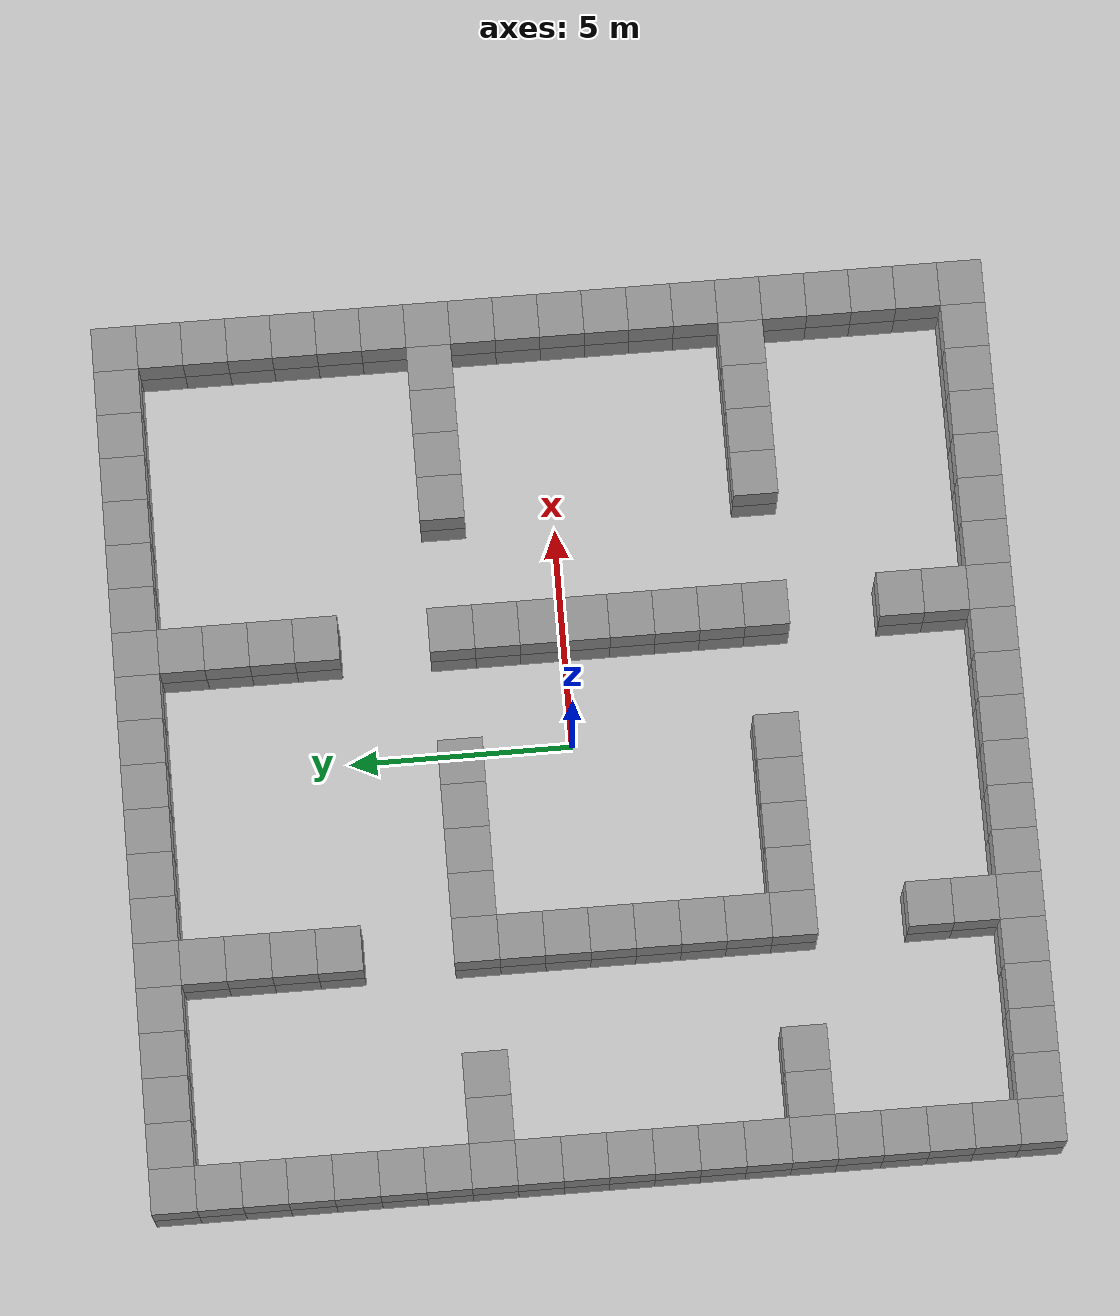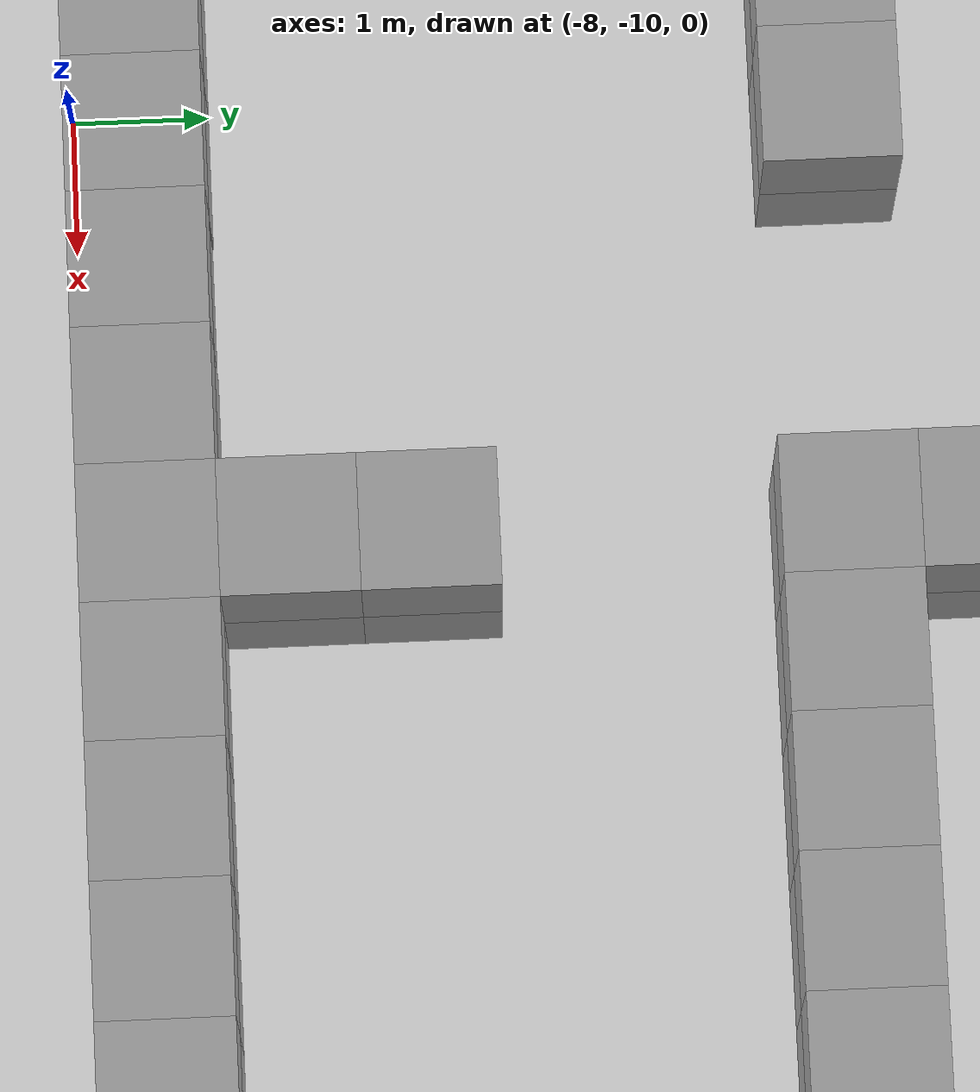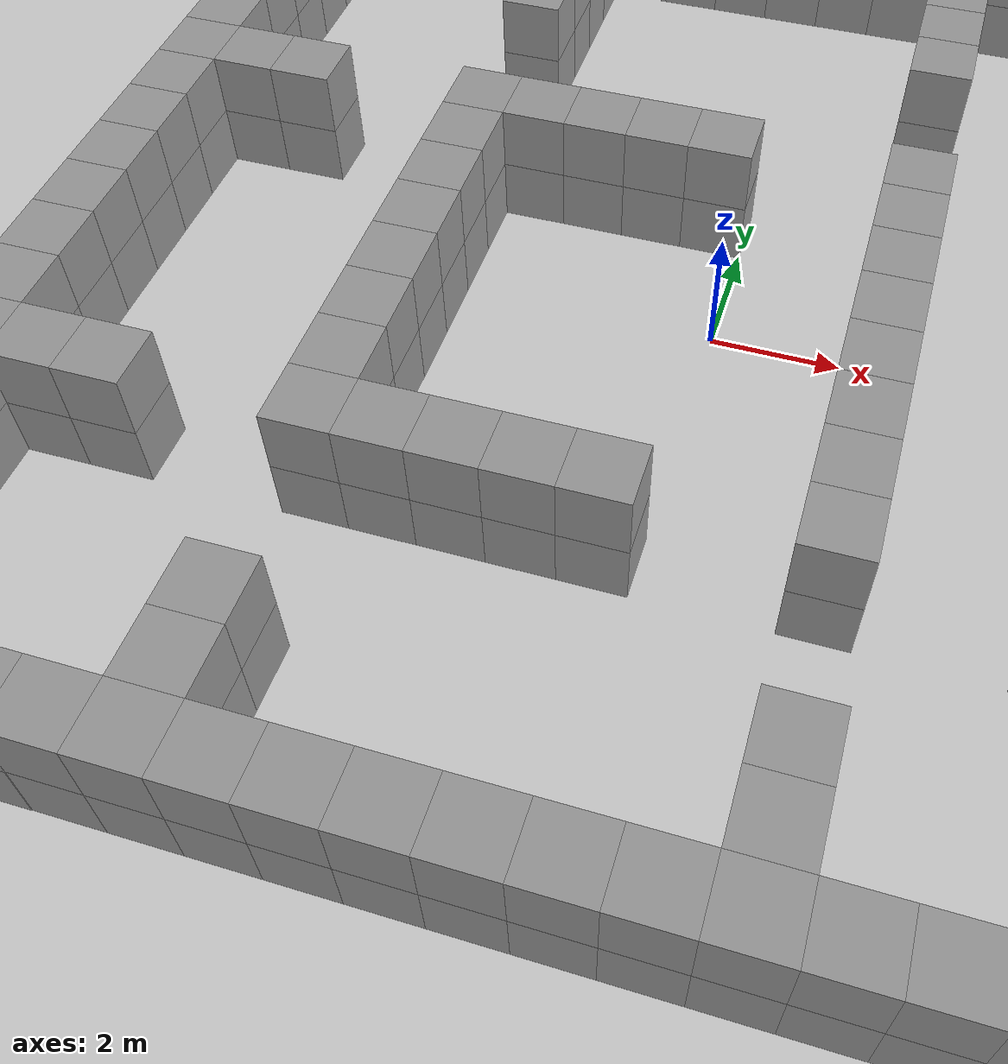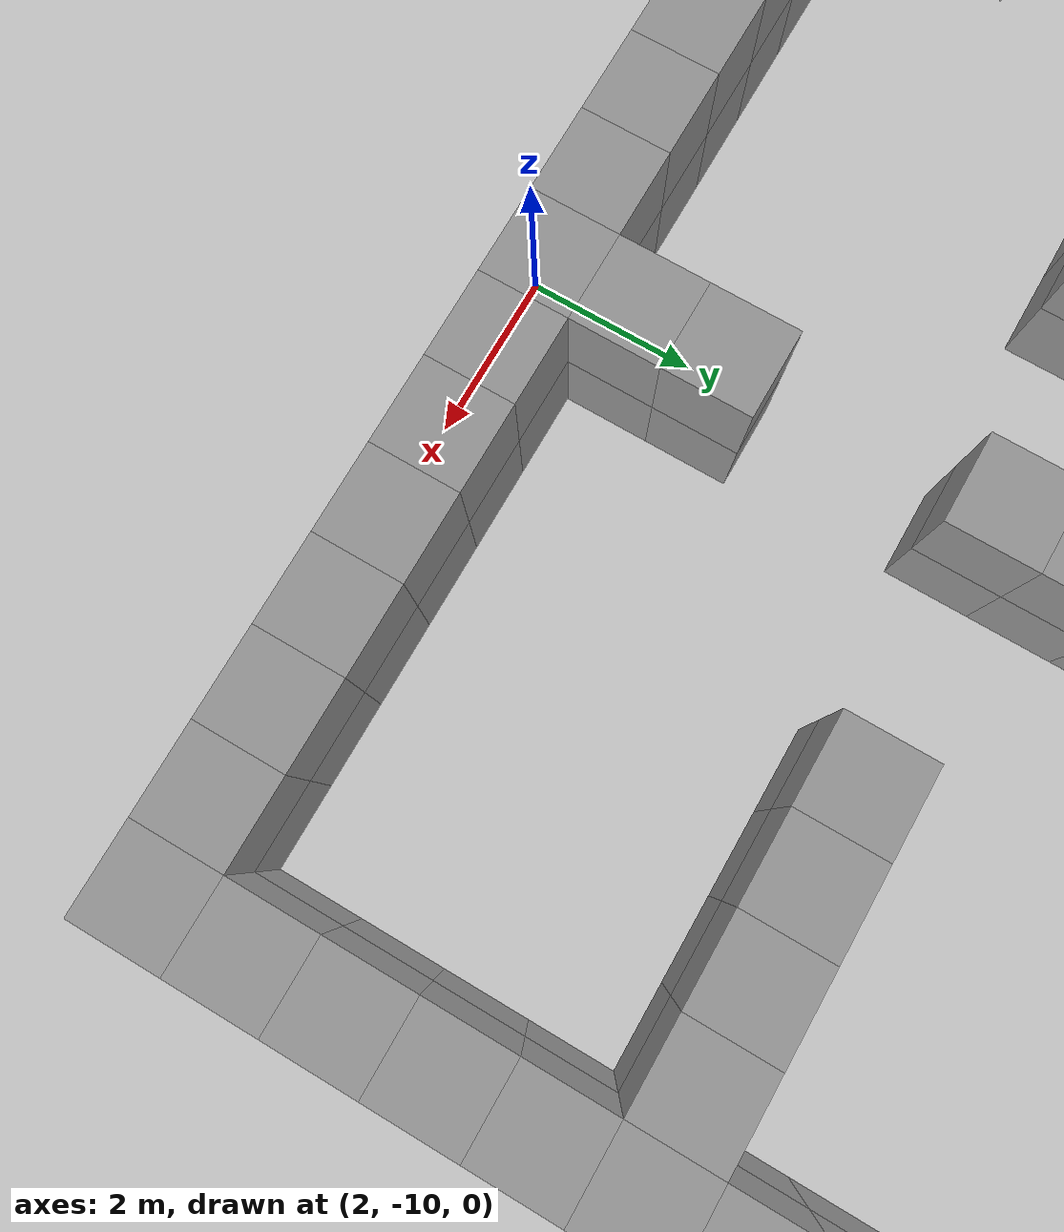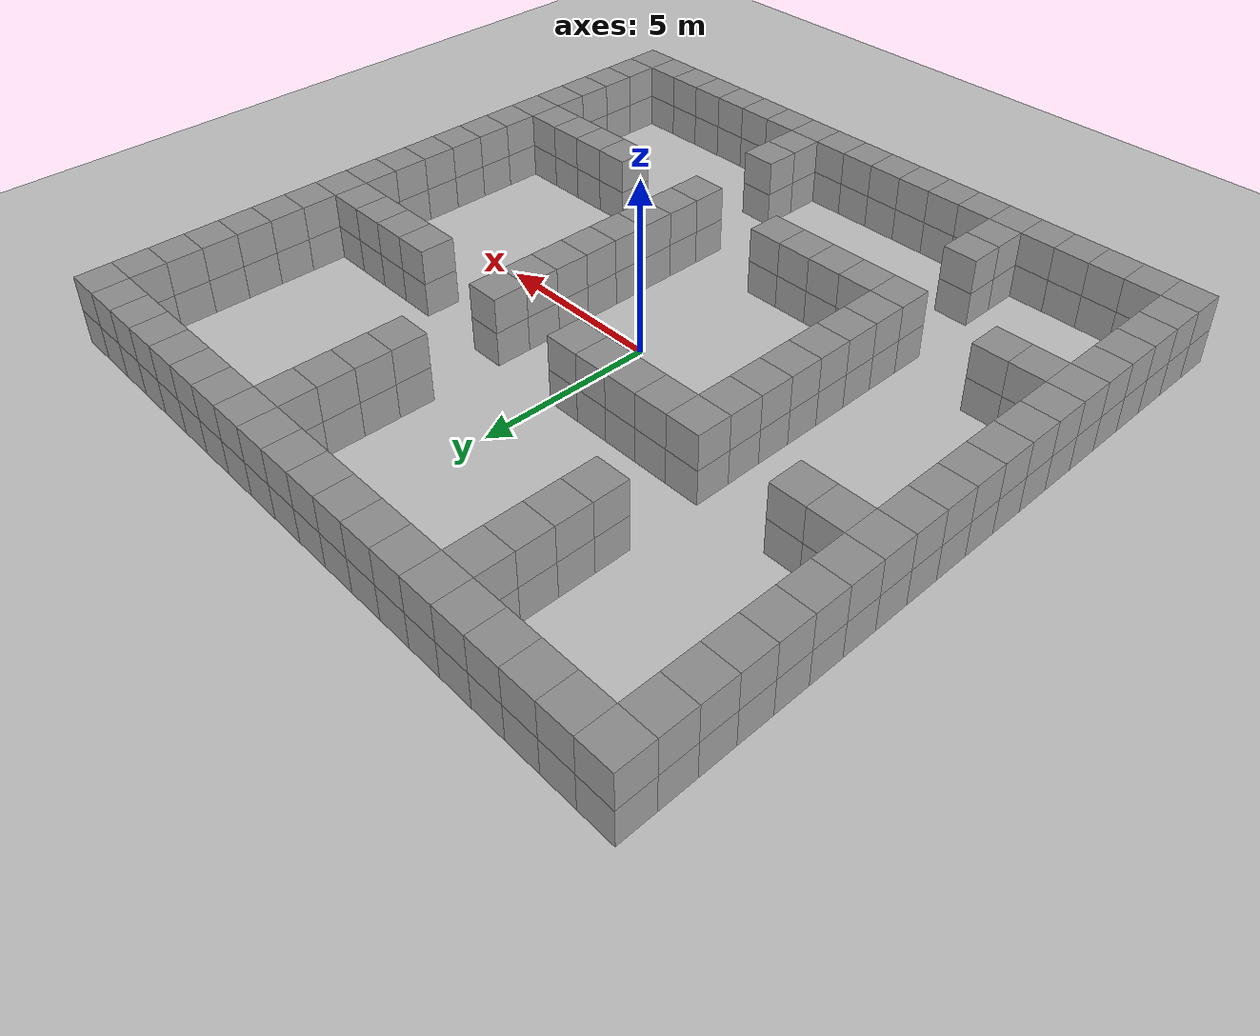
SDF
<sdf version="1.7">
 <world name="default">
  <light name="sun" type="directional">
   <pose>0 0 10 0 -0 0</pose>
   <diffuse>0.8 0.8 0.8 1</diffuse>
   <specular>0.2 0.2 0.2 1</specular>
   <attenuation>
    <range>1000</range>
    <constant>0.9</constant>
    <linear>0.01</linear>
    <quadratic>0.001</quadratic>
   </attenuation>
   <direction>-0.5 0.1 -0.9</direction>
   <spot><inner_angle>0</inner_angle><outer_angle>0</outer_angle><falloff>0</falloff></spot>
  </light>
  <model name="ground_plane">
   <static>1</static>
   <link name="link">
    <collision name="collision">
     <geometry><plane><normal>0 0 1</normal><size>100 100</size></plane></geometry>
     <surface>
      <contact><collide_bitmask>65535</collide_bitmask></contact>
      <friction><ode><mu>100</mu><mu2>50</mu2></ode></friction>
     </surface>
    </collision>
    <visual name="visual">
     <cast_shadows>0</cast_shadows>
     <geometry><plane><normal>0 0 1</normal><size>100 100</size></plane></geometry>
     <material>
      <script><uri>file://media/materials/scripts/gazebo.material</uri><name>Gazebo/Grey</name></script>
     </material>
    </visual>
   </link>
  </model>
  <gravity>0 0 -9.8</gravity>
  <magnetic_field>6e-06 2.3e-05 -4.2e-05</magnetic_field>
  <atmosphere type="adiabatic"/>
  <physics type="ode">
   <max_step_size>0.001</max_step_size>
   <real_time_factor>1</real_time_factor>
   <real_time_update_rate>1000</real_time_update_rate>
  </physics>
  <scene><ambient>0.4 0.4 0.4 1</ambient><background>0.7 0.7 0.7 1</background><shadows>1</shadows></scene>
  <audio><device>default</device></audio>
  <spherical_coordinates>
   <surface_model>EARTH_WGS84</surface_model>
   <latitude_deg>0</latitude_deg>
   <longitude_deg>0</longitude_deg>
   <elevation>0</elevation>
   <heading_deg>0</heading_deg>
  </spherical_coordinates>
  <model name="unit_box_clone_1">
   <pose>9.5 0.5 0.5 0 -0 0</pose>
   <link name="link">
    <inertial>
     <mass>1</mass>
     <inertia>
      <ixx>0.166667</ixx>
      <ixy>0</ixy>
      <ixz>0</ixz>
      <iyy>0.166667</iyy>
      <iyz>0</iyz>
      <izz>0.166667</izz>
     </inertia>
    </inertial>
    <collision name="collision"><geometry><box><size>1 1 1</size></box></geometry></collision>
    <visual name="visual">
     <geometry><box><size>1 1 1</size></box></geometry>
     <material>
      <script><name>Gazebo/Grey</name><uri>file://media/materials/scripts/gazebo.material</uri></script>
     </material>
    </visual>
   </link>
  </model>
  <model name="unit_box_clone_8">
   <pose>0.5 9.5 0.5 0 -0 0</pose>
   <link name="link">
    <inertial>
     <mass>1</mass>
     <inertia>
      <ixx>0.166667</ixx>
      <ixy>0</ixy>
      <ixz>0</ixz>
      <iyy>0.166667</iyy>
      <iyz>0</iyz>
      <izz>0.166667</izz>
     </inertia>
    </inertial>
    <collision name="collision"><geometry><box><size>1 1 1</size></box></geometry></collision>
    <visual name="visual">
     <geometry><box><size>1 1 1</size></box></geometry>
     <material>
      <script><name>Gazebo/Grey</name><uri>file://media/materials/scripts/gazebo.material</uri></script>
     </material>
    </visual>
   </link>
  </model>
  <model name="unit_box_clone_13">
   <pose>1.5 9.5 0.5 0 -0 0</pose>
   <link name="link">
    <inertial>
     <mass>1</mass>
     <inertia>
      <ixx>0.166667</ixx>
      <ixy>0</ixy>
      <ixz>0</ixz>
      <iyy>0.166667</iyy>
      <iyz>0</iyz>
      <izz>0.166667</izz>
     </inertia>
    </inertial>
    <collision name="collision"><geometry><box><size>1 1 1</size></box></geometry></collision>
    <visual name="visual">
     <geometry><box><size>1 1 1</size></box></geometry>
     <material>
      <script><name>Gazebo/Grey</name><uri>file://media/materials/scripts/gazebo.material</uri></script>
     </material>
    </visual>
   </link>
  </model>
  <model name="unit_box_clone_14">
   <pose>2.5 9.5 0.5 0 -0 0</pose>
   <link name="link">
    <inertial>
     <mass>1</mass>
     <inertia>
      <ixx>0.166667</ixx>
      <ixy>0</ixy>
      <ixz>0</ixz>
      <iyy>0.166667</iyy>
      <iyz>0</iyz>
      <izz>0.166667</izz>
     </inertia>
    </inertial>
    <collision name="collision"><geometry><box><size>1 1 1</size></box></geometry></collision>
    <visual name="visual">
     <geometry><box><size>1 1 1</size></box></geometry>
     <material>
      <script><name>Gazebo/Grey</name><uri>file://media/materials/scripts/gazebo.material</uri></script>
     </material>
    </visual>
   </link>
  </model>
  <model name="unit_box_clone_15">
   <pose>3.5 9.5 0.5 0 -0 0</pose>
   <link name="link">
    <inertial>
     <mass>1</mass>
     <inertia>
      <ixx>0.166667</ixx>
      <ixy>0</ixy>
      <ixz>0</ixz>
      <iyy>0.166667</iyy>
      <iyz>0</iyz>
      <izz>0.166667</izz>
     </inertia>
    </inertial>
    <collision name="collision"><geometry><box><size>1 1 1</size></box></geometry></collision>
    <visual name="visual">
     <geometry><box><size>1 1 1</size></box></geometry>
     <material>
      <script><name>Gazebo/Grey</name><uri>file://media/materials/scripts/gazebo.material</uri></script>
     </material>
    </visual>
   </link>
  </model>
  <model name="unit_box_clone_16">
   <pose>4.5 9.5 0.5 0 -0 0</pose>
   <link name="link">
    <inertial>
     <mass>1</mass>
     <inertia>
      <ixx>0.166667</ixx>
      <ixy>0</ixy>
      <ixz>0</ixz>
      <iyy>0.166667</iyy>
      <iyz>0</iyz>
      <izz>0.166667</izz>
     </inertia>
    </inertial>
    <collision name="collision"><geometry><box><size>1 1 1</size></box></geometry></collision>
    <visual name="visual">
     <geometry><box><size>1 1 1</size></box></geometry>
     <material>
      <script><name>Gazebo/Grey</name><uri>file://media/materials/scripts/gazebo.material</uri></script>
     </material>
    </visual>
   </link>
  </model>
  <model name="unit_box_clone_17">
   <pose>5.5 9.5 0.5 0 -0 0</pose>
   <link name="link">
    <inertial>
     <mass>1</mass>
     <inertia>
      <ixx>0.166667</ixx>
      <ixy>0</ixy>
      <ixz>0</ixz>
      <iyy>0.166667</iyy>
      <iyz>0</iyz>
      <izz>0.166667</izz>
     </inertia>
    </inertial>
    <collision name="collision"><geometry><box><size>1 1 1</size></box></geometry></collision>
    <visual name="visual">
     <geometry><box><size>1 1 1</size></box></geometry>
     <material>
      <script><name>Gazebo/Grey</name><uri>file://media/materials/scripts/gazebo.material</uri></script>
     </material>
    </visual>
   </link>
  </model>
  <model name="unit_box_clone_18">
   <pose>6.5 9.5 0.5 0 -0 0</pose>
   <link name="link">
    <inertial>
     <mass>1</mass>
     <inertia>
      <ixx>0.166667</ixx>
      <ixy>0</ixy>
      <ixz>0</ixz>
      <iyy>0.166667</iyy>
      <iyz>0</iyz>
      <izz>0.166667</izz>
     </inertia>
    </inertial>
    <collision name="collision"><geometry><box><size>1 1 1</size></box></geometry></collision>
    <visual name="visual">
     <geometry><box><size>1 1 1</size></box></geometry>
     <material>
      <script><name>Gazebo/Grey</name><uri>file://media/materials/scripts/gazebo.material</uri></script>
     </material>
    </visual>
   </link>
  </model>
  <model name="unit_box_clone_19">
   <pose>7.5 9.5 0.5 0 -0 0</pose>
   <link name="link">
    <inertial>
     <mass>1</mass>
     <inertia>
      <ixx>0.166667</ixx>
      <ixy>0</ixy>
      <ixz>0</ixz>
      <iyy>0.166667</iyy>
      <iyz>0</iyz>
      <izz>0.166667</izz>
     </inertia>
    </inertial>
    <collision name="collision"><geometry><box><size>1 1 1</size></box></geometry></collision>
    <visual name="visual">
     <geometry><box><size>1 1 1</size></box></geometry>
     <material>
      <script><name>Gazebo/Grey</name><uri>file://media/materials/scripts/gazebo.material</uri></script>
     </material>
    </visual>
   </link>
  </model>
  <model name="unit_box_clone_20">
   <pose>8.5 9.5 0.5 0 -0 0</pose>
   <link name="link">
    <inertial>
     <mass>1</mass>
     <inertia>
      <ixx>0.166667</ixx>
      <ixy>0</ixy>
      <ixz>0</ixz>
      <iyy>0.166667</iyy>
      <iyz>0</iyz>
      <izz>0.166667</izz>
     </inertia>
    </inertial>
    <collision name="collision"><geometry><box><size>1 1 1</size></box></geometry></collision>
    <visual name="visual">
     <geometry><box><size>1 1 1</size></box></geometry>
     <material>
      <script><name>Gazebo/Grey</name><uri>file://media/materials/scripts/gazebo.material</uri></script>
     </material>
    </visual>
   </link>
  </model>
  <model name="unit_box_clone_21">
   <pose>9.5 9.5 0.5 0 -0 0</pose>
   <link name="link">
    <inertial>
     <mass>1</mass>
     <inertia>
      <ixx>0.166667</ixx>
      <ixy>0</ixy>
      <ixz>0</ixz>
      <iyy>0.166667</iyy>
      <iyz>0</iyz>
      <izz>0.166667</izz>
     </inertia>
    </inertial>
    <collision name="collision"><geometry><box><size>1 1 1</size></box></geometry></collision>
    <visual name="visual">
     <geometry><box><size>1 1 1</size></box></geometry>
     <material>
      <script><name>Gazebo/Grey</name><uri>file://media/materials/scripts/gazebo.material</uri></script>
     </material>
    </visual>
   </link>
  </model>
  <model name="unit_box_clone_22">
   <pose>9.5 8.5 0.5 0 -0 0</pose>
   <link name="link">
    <inertial>
     <mass>1</mass>
     <inertia>
      <ixx>0.166667</ixx>
      <ixy>0</ixy>
      <ixz>0</ixz>
      <iyy>0.166667</iyy>
      <iyz>0</iyz>
      <izz>0.166667</izz>
     </inertia>
    </inertial>
    <collision name="collision"><geometry><box><size>1 1 1</size></box></geometry></collision>
    <visual name="visual">
     <geometry><box><size>1 1 1</size></box></geometry>
     <material>
      <script><name>Gazebo/Grey</name><uri>file://media/materials/scripts/gazebo.material</uri></script>
     </material>
    </visual>
   </link>
  </model>
  <model name="unit_box_clone_23">
   <pose>9.5 7.5 0.5 0 -0 0</pose>
   <link name="link">
    <inertial>
     <mass>1</mass>
     <inertia>
      <ixx>0.166667</ixx>
      <ixy>0</ixy>
      <ixz>0</ixz>
      <iyy>0.166667</iyy>
      <iyz>0</iyz>
      <izz>0.166667</izz>
     </inertia>
    </inertial>
    <collision name="collision"><geometry><box><size>1 1 1</size></box></geometry></collision>
    <visual name="visual">
     <geometry><box><size>1 1 1</size></box></geometry>
     <material>
      <script><name>Gazebo/Grey</name><uri>file://media/materials/scripts/gazebo.material</uri></script>
     </material>
    </visual>
   </link>
  </model>
  <model name="unit_box_clone_24">
   <pose>9.5 6.5 0.5 0 -0 0</pose>
   <link name="link">
    <inertial>
     <mass>1</mass>
     <inertia>
      <ixx>0.166667</ixx>
      <ixy>0</ixy>
      <ixz>0</ixz>
      <iyy>0.166667</iyy>
      <iyz>0</iyz>
      <izz>0.166667</izz>
     </inertia>
    </inertial>
    <collision name="collision"><geometry><box><size>1 1 1</size></box></geometry></collision>
    <visual name="visual">
     <geometry><box><size>1 1 1</size></box></geometry>
     <material>
      <script><name>Gazebo/Grey</name><uri>file://media/materials/scripts/gazebo.material</uri></script>
     </material>
    </visual>
   </link>
  </model>
  <model name="unit_box_clone_25">
   <pose>9.5 5.5 0.5 0 -0 0</pose>
   <link name="link">
    <inertial>
     <mass>1</mass>
     <inertia>
      <ixx>0.166667</ixx>
      <ixy>0</ixy>
      <ixz>0</ixz>
      <iyy>0.166667</iyy>
      <iyz>0</iyz>
      <izz>0.166667</izz>
     </inertia>
    </inertial>
    <collision name="collision"><geometry><box><size>1 1 1</size></box></geometry></collision>
    <visual name="visual">
     <geometry><box><size>1 1 1</size></box></geometry>
     <material>
      <script><name>Gazebo/Grey</name><uri>file://media/materials/scripts/gazebo.material</uri></script>
     </material>
    </visual>
   </link>
  </model>
  <model name="unit_box_clone_26">
   <pose>9.5 4.5 0.5 0 -0 0</pose>
   <link name="link">
    <inertial>
     <mass>1</mass>
     <inertia>
      <ixx>0.166667</ixx>
      <ixy>0</ixy>
      <ixz>0</ixz>
      <iyy>0.166667</iyy>
      <iyz>0</iyz>
      <izz>0.166667</izz>
     </inertia>
    </inertial>
    <collision name="collision"><geometry><box><size>1 1 1</size></box></geometry></collision>
    <visual name="visual">
     <geometry><box><size>1 1 1</size></box></geometry>
     <material>
      <script><name>Gazebo/Grey</name><uri>file://media/materials/scripts/gazebo.material</uri></script>
     </material>
    </visual>
   </link>
  </model>
  <model name="unit_box_clone_27">
   <pose>9.5 3.5 0.5 0 -0 0</pose>
   <link name="link">
    <inertial>
     <mass>1</mass>
     <inertia>
      <ixx>0.166667</ixx>
      <ixy>0</ixy>
      <ixz>0</ixz>
      <iyy>0.166667</iyy>
      <iyz>0</iyz>
      <izz>0.166667</izz>
     </inertia>
    </inertial>
    <collision name="collision"><geometry><box><size>1 1 1</size></box></geometry></collision>
    <visual name="visual">
     <geometry><box><size>1 1 1</size></box></geometry>
     <material>
      <script><name>Gazebo/Grey</name><uri>file://media/materials/scripts/gazebo.material</uri></script>
     </material>
    </visual>
   </link>
  </model>
  <model name="unit_box_clone_28">
   <pose>9.5 2.5 0.5 0 -0 0</pose>
   <link name="link">
    <inertial>
     <mass>1</mass>
     <inertia>
      <ixx>0.166667</ixx>
      <ixy>0</ixy>
      <ixz>0</ixz>
      <iyy>0.166667</iyy>
      <iyz>0</iyz>
      <izz>0.166667</izz>
     </inertia>
    </inertial>
    <collision name="collision"><geometry><box><size>1 1 1</size></box></geometry></collision>
    <visual name="visual">
     <geometry><box><size>1 1 1</size></box></geometry>
     <material>
      <script><name>Gazebo/Grey</name><uri>file://media/materials/scripts/gazebo.material</uri></script>
     </material>
    </visual>
   </link>
  </model>
  <model name="unit_box_clone_29">
   <pose>9.5 1.5 0.5 0 -0 0</pose>
   <link name="link">
    <inertial>
     <mass>1</mass>
     <inertia>
      <ixx>0.166667</ixx>
      <ixy>0</ixy>
      <ixz>0</ixz>
      <iyy>0.166667</iyy>
      <iyz>0</iyz>
      <izz>0.166667</izz>
     </inertia>
    </inertial>
    <collision name="collision"><geometry><box><size>1 1 1</size></box></geometry></collision>
    <visual name="visual">
     <geometry><box><size>1 1 1</size></box></geometry>
     <material>
      <script><name>Gazebo/Grey</name><uri>file://media/materials/scripts/gazebo.material</uri></script>
     </material>
    </visual>
   </link>
  </model>
  <model name="unit_box_clone_0_clone_clone_3">
   <pose>9.5 0.5 1.5 0 -0 0</pose>
   <link name="link">
    <inertial>
     <mass>1</mass>
     <inertia>
      <ixx>0.166667</ixx>
      <ixy>0</ixy>
      <ixz>0</ixz>
      <iyy>0.166667</iyy>
      <iyz>0</iyz>
      <izz>0.166667</izz>
     </inertia>
    </inertial>
    <collision name="collision"><geometry><box><size>1 1 1</size></box></geometry></collision>
    <visual name="visual">
     <geometry><box><size>1 1 1</size></box></geometry>
     <material>
      <script><name>Gazebo/Grey</name><uri>file://media/materials/scripts/gazebo.material</uri></script>
     </material>
    </visual>
   </link>
  </model>
  <model name="unit_box_clone_0_clone_clone_4">
   <pose>9.5 1.5 1.5 0 -0 0</pose>
   <link name="link">
    <inertial>
     <mass>1</mass>
     <inertia>
      <ixx>0.166667</ixx>
      <ixy>0</ixy>
      <ixz>0</ixz>
      <iyy>0.166667</iyy>
      <iyz>0</iyz>
      <izz>0.166667</izz>
     </inertia>
    </inertial>
    <collision name="collision"><geometry><box><size>1 1 1</size></box></geometry></collision>
    <visual name="visual">
     <geometry><box><size>1 1 1</size></box></geometry>
     <material>
      <script><name>Gazebo/Grey</name><uri>file://media/materials/scripts/gazebo.material</uri></script>
     </material>
    </visual>
   </link>
  </model>
  <model name="unit_box_clone_0_clone_clone_5">
   <pose>9.5 2.5 1.5 0 -0 0</pose>
   <link name="link">
    <inertial>
     <mass>1</mass>
     <inertia>
      <ixx>0.166667</ixx>
      <ixy>0</ixy>
      <ixz>0</ixz>
      <iyy>0.166667</iyy>
      <iyz>0</iyz>
      <izz>0.166667</izz>
     </inertia>
    </inertial>
    <collision name="collision"><geometry><box><size>1 1 1</size></box></geometry></collision>
    <visual name="visual">
     <geometry><box><size>1 1 1</size></box></geometry>
     <material>
      <script><name>Gazebo/Grey</name><uri>file://media/materials/scripts/gazebo.material</uri></script>
     </material>
    </visual>
   </link>
  </model>
  <model name="unit_box_clone_0_clone_clone_6">
   <pose>9.5 3.5 1.5 0 -0 0</pose>
   <link name="link">
    <inertial>
     <mass>1</mass>
     <inertia>
      <ixx>0.166667</ixx>
      <ixy>0</ixy>
      <ixz>0</ixz>
      <iyy>0.166667</iyy>
      <iyz>0</iyz>
      <izz>0.166667</izz>
     </inertia>
    </inertial>
    <collision name="collision"><geometry><box><size>1 1 1</size></box></geometry></collision>
    <visual name="visual">
     <geometry><box><size>1 1 1</size></box></geometry>
     <material>
      <script><name>Gazebo/Grey</name><uri>file://media/materials/scripts/gazebo.material</uri></script>
     </material>
    </visual>
   </link>
  </model>
  <model name="unit_box_clone_0_clone_clone_7">
   <pose>9.5 4.5 1.5 0 -0 0</pose>
   <link name="link">
    <inertial>
     <mass>1</mass>
     <inertia>
      <ixx>0.166667</ixx>
      <ixy>0</ixy>
      <ixz>0</ixz>
      <iyy>0.166667</iyy>
      <iyz>0</iyz>
      <izz>0.166667</izz>
     </inertia>
    </inertial>
    <collision name="collision"><geometry><box><size>1 1 1</size></box></geometry></collision>
    <visual name="visual">
     <geometry><box><size>1 1 1</size></box></geometry>
     <material>
      <script><name>Gazebo/Grey</name><uri>file://media/materials/scripts/gazebo.material</uri></script>
     </material>
    </visual>
   </link>
  </model>
  <model name="unit_box_clone_0_clone_clone_8">
   <pose>9.5 5.5 1.5 0 -0 0</pose>
   <link name="link">
    <inertial>
     <mass>1</mass>
     <inertia>
      <ixx>0.166667</ixx>
      <ixy>0</ixy>
      <ixz>0</ixz>
      <iyy>0.166667</iyy>
      <iyz>0</iyz>
      <izz>0.166667</izz>
     </inertia>
    </inertial>
    <collision name="collision"><geometry><box><size>1 1 1</size></box></geometry></collision>
    <visual name="visual">
     <geometry><box><size>1 1 1</size></box></geometry>
     <material>
      <script><name>Gazebo/Grey</name><uri>file://media/materials/scripts/gazebo.material</uri></script>
     </material>
    </visual>
   </link>
  </model>
  <model name="unit_box_clone_0_clone_clone_9">
   <pose>9.5 6.5 1.5 0 -0 0</pose>
   <link name="link">
    <inertial>
     <mass>1</mass>
     <inertia>
      <ixx>0.166667</ixx>
      <ixy>0</ixy>
      <ixz>0</ixz>
      <iyy>0.166667</iyy>
      <iyz>0</iyz>
      <izz>0.166667</izz>
     </inertia>
    </inertial>
    <collision name="collision"><geometry><box><size>1 1 1</size></box></geometry></collision>
    <visual name="visual">
     <geometry><box><size>1 1 1</size></box></geometry>
     <material>
      <script><name>Gazebo/Grey</name><uri>file://media/materials/scripts/gazebo.material</uri></script>
     </material>
    </visual>
   </link>
  </model>
  <model name="unit_box_clone_0_clone_clone_10">
   <pose>9.5 7.5 1.5 0 -0 0</pose>
   <link name="link">
    <inertial>
     <mass>1</mass>
     <inertia>
      <ixx>0.166667</ixx>
      <ixy>0</ixy>
      <ixz>0</ixz>
      <iyy>0.166667</iyy>
      <iyz>0</iyz>
      <izz>0.166667</izz>
     </inertia>
    </inertial>
    <collision name="collision"><geometry><box><size>1 1 1</size></box></geometry></collision>
    <visual name="visual">
     <geometry><box><size>1 1 1</size></box></geometry>
     <material>
      <script><name>Gazebo/Grey</name><uri>file://media/materials/scripts/gazebo.material</uri></script>
     </material>
    </visual>
   </link>
  </model>
  <model name="unit_box_clone_0_clone_clone_11">
   <pose>9.5 8.5 1.5 0 -0 0</pose>
   <link name="link">
    <inertial>
     <mass>1</mass>
     <inertia>
      <ixx>0.166667</ixx>
      <ixy>0</ixy>
      <ixz>0</ixz>
      <iyy>0.166667</iyy>
      <iyz>0</iyz>
      <izz>0.166667</izz>
     </inertia>
    </inertial>
    <collision name="collision"><geometry><box><size>1 1 1</size></box></geometry></collision>
    <visual name="visual">
     <geometry><box><size>1 1 1</size></box></geometry>
     <material>
      <script><name>Gazebo/Grey</name><uri>file://media/materials/scripts/gazebo.material</uri></script>
     </material>
    </visual>
   </link>
  </model>
  <model name="unit_box_clone_0_clone_clone_12">
   <pose>9.5 9.5 1.5 0 -0 0</pose>
   <link name="link">
    <inertial>
     <mass>1</mass>
     <inertia>
      <ixx>0.166667</ixx>
      <ixy>0</ixy>
      <ixz>0</ixz>
      <iyy>0.166667</iyy>
      <iyz>0</iyz>
      <izz>0.166667</izz>
     </inertia>
    </inertial>
    <collision name="collision"><geometry><box><size>1 1 1</size></box></geometry></collision>
    <visual name="visual">
     <geometry><box><size>1 1 1</size></box></geometry>
     <material>
      <script><name>Gazebo/Grey</name><uri>file://media/materials/scripts/gazebo.material</uri></script>
     </material>
    </visual>
   </link>
  </model>
  <model name="unit_box_clone_0_clone_clone_13">
   <pose>8.5 9.5 1.5 0 -0 0</pose>
   <link name="link">
    <inertial>
     <mass>1</mass>
     <inertia>
      <ixx>0.166667</ixx>
      <ixy>0</ixy>
      <ixz>0</ixz>
      <iyy>0.166667</iyy>
      <iyz>0</iyz>
      <izz>0.166667</izz>
     </inertia>
    </inertial>
    <collision name="collision"><geometry><box><size>1 1 1</size></box></geometry></collision>
    <visual name="visual">
     <geometry><box><size>1 1 1</size></box></geometry>
     <material>
      <script><name>Gazebo/Grey</name><uri>file://media/materials/scripts/gazebo.material</uri></script>
     </material>
    </visual>
   </link>
  </model>
  <model name="unit_box_clone_0_clone_clone_14">
   <pose>7.5 9.5 1.5 0 -0 0</pose>
   <link name="link">
    <inertial>
     <mass>1</mass>
     <inertia>
      <ixx>0.166667</ixx>
      <ixy>0</ixy>
      <ixz>0</ixz>
      <iyy>0.166667</iyy>
      <iyz>0</iyz>
      <izz>0.166667</izz>
     </inertia>
    </inertial>
    <collision name="collision"><geometry><box><size>1 1 1</size></box></geometry></collision>
    <visual name="visual">
     <geometry><box><size>1 1 1</size></box></geometry>
     <material>
      <script><name>Gazebo/Grey</name><uri>file://media/materials/scripts/gazebo.material</uri></script>
     </material>
    </visual>
   </link>
  </model>
  <model name="unit_box_clone_0_clone_clone_15">
   <pose>6.5 9.5 1.5 0 -0 0</pose>
   <link name="link">
    <inertial>
     <mass>1</mass>
     <inertia>
      <ixx>0.166667</ixx>
      <ixy>0</ixy>
      <ixz>0</ixz>
      <iyy>0.166667</iyy>
      <iyz>0</iyz>
      <izz>0.166667</izz>
     </inertia>
    </inertial>
    <collision name="collision"><geometry><box><size>1 1 1</size></box></geometry></collision>
    <visual name="visual">
     <geometry><box><size>1 1 1</size></box></geometry>
     <material>
      <script><name>Gazebo/Grey</name><uri>file://media/materials/scripts/gazebo.material</uri></script>
     </material>
    </visual>
   </link>
  </model>
  <model name="unit_box_clone_0_clone_clone_16">
   <pose>5.5 9.5 1.5 0 -0 0</pose>
   <link name="link">
    <inertial>
     <mass>1</mass>
     <inertia>
      <ixx>0.166667</ixx>
      <ixy>0</ixy>
      <ixz>0</ixz>
      <iyy>0.166667</iyy>
      <iyz>0</iyz>
      <izz>0.166667</izz>
     </inertia>
    </inertial>
    <collision name="collision"><geometry><box><size>1 1 1</size></box></geometry></collision>
    <visual name="visual">
     <geometry><box><size>1 1 1</size></box></geometry>
     <material>
      <script><name>Gazebo/Grey</name><uri>file://media/materials/scripts/gazebo.material</uri></script>
     </material>
    </visual>
   </link>
  </model>
  <model name="unit_box_clone_0_clone_clone_17">
   <pose>4.5 9.5 1.5 0 -0 0</pose>
   <link name="link">
    <inertial>
     <mass>1</mass>
     <inertia>
      <ixx>0.166667</ixx>
      <ixy>0</ixy>
      <ixz>0</ixz>
      <iyy>0.166667</iyy>
      <iyz>0</iyz>
      <izz>0.166667</izz>
     </inertia>
    </inertial>
    <collision name="collision"><geometry><box><size>1 1 1</size></box></geometry></collision>
    <visual name="visual">
     <geometry><box><size>1 1 1</size></box></geometry>
     <material>
      <script><name>Gazebo/Grey</name><uri>file://media/materials/scripts/gazebo.material</uri></script>
     </material>
    </visual>
   </link>
  </model>
  <model name="unit_box_clone_0_clone_clone_18">
   <pose>3.5 9.5 1.5 0 -0 0</pose>
   <link name="link">
    <inertial>
     <mass>1</mass>
     <inertia>
      <ixx>0.166667</ixx>
      <ixy>0</ixy>
      <ixz>0</ixz>
      <iyy>0.166667</iyy>
      <iyz>0</iyz>
      <izz>0.166667</izz>
     </inertia>
    </inertial>
    <collision name="collision"><geometry><box><size>1 1 1</size></box></geometry></collision>
    <visual name="visual">
     <geometry><box><size>1 1 1</size></box></geometry>
     <material>
      <script><name>Gazebo/Grey</name><uri>file://media/materials/scripts/gazebo.material</uri></script>
     </material>
    </visual>
   </link>
  </model>
  <model name="unit_box_clone_0_clone_clone_19">
   <pose>2.5 9.5 1.5 0 -0 0</pose>
   <link name="link">
    <inertial>
     <mass>1</mass>
     <inertia>
      <ixx>0.166667</ixx>
      <ixy>0</ixy>
      <ixz>0</ixz>
      <iyy>0.166667</iyy>
      <iyz>0</iyz>
      <izz>0.166667</izz>
     </inertia>
    </inertial>
    <collision name="collision"><geometry><box><size>1 1 1</size></box></geometry></collision>
    <visual name="visual">
     <geometry><box><size>1 1 1</size></box></geometry>
     <material>
      <script><name>Gazebo/Grey</name><uri>file://media/materials/scripts/gazebo.material</uri></script>
     </material>
    </visual>
   </link>
  </model>
  <model name="unit_box_clone_0_clone_clone_20">
   <pose>1.5 9.5 1.5 0 -0 0</pose>
   <link name="link">
    <inertial>
     <mass>1</mass>
     <inertia>
      <ixx>0.166667</ixx>
      <ixy>0</ixy>
      <ixz>0</ixz>
      <iyy>0.166667</iyy>
      <iyz>0</iyz>
      <izz>0.166667</izz>
     </inertia>
    </inertial>
    <collision name="collision"><geometry><box><size>1 1 1</size></box></geometry></collision>
    <visual name="visual">
     <geometry><box><size>1 1 1</size></box></geometry>
     <material>
      <script><name>Gazebo/Grey</name><uri>file://media/materials/scripts/gazebo.material</uri></script>
     </material>
    </visual>
   </link>
  </model>
  <model name="unit_box_clone_0_clone_clone_21">
   <pose>0.5 9.5 1.5 0 -0 0</pose>
   <link name="link">
    <inertial>
     <mass>1</mass>
     <inertia>
      <ixx>0.166667</ixx>
      <ixy>0</ixy>
      <ixz>0</ixz>
      <iyy>0.166667</iyy>
      <iyz>0</iyz>
      <izz>0.166667</izz>
     </inertia>
    </inertial>
    <collision name="collision"><geometry><box><size>1 1 1</size></box></geometry></collision>
    <visual name="visual">
     <geometry><box><size>1 1 1</size></box></geometry>
     <material>
      <script><name>Gazebo/Grey</name><uri>file://media/materials/scripts/gazebo.material</uri></script>
     </material>
    </visual>
   </link>
  </model>
  <model name="unit_box_clone_7_clone_4">
   <pose>-0.5 9.5 0.5 0 -0 0</pose>
   <link name="link">
    <inertial>
     <mass>1</mass>
     <inertia>
      <ixx>0.166667</ixx>
      <ixy>0</ixy>
      <ixz>0</ixz>
      <iyy>0.166667</iyy>
      <iyz>0</iyz>
      <izz>0.166667</izz>
     </inertia>
    </inertial>
    <collision name="collision"><geometry><box><size>1 1 1</size></box></geometry></collision>
    <visual name="visual">
     <geometry><box><size>1 1 1</size></box></geometry>
     <material>
      <script><name>Gazebo/Grey</name><uri>file://media/materials/scripts/gazebo.material</uri></script>
     </material>
    </visual>
   </link>
  </model>
  <model name="unit_box_clone_7_clone_5">
   <pose>-1.5 9.5 0.5 0 -0 0</pose>
   <link name="link">
    <inertial>
     <mass>1</mass>
     <inertia>
      <ixx>0.166667</ixx>
      <ixy>0</ixy>
      <ixz>0</ixz>
      <iyy>0.166667</iyy>
      <iyz>0</iyz>
      <izz>0.166667</izz>
     </inertia>
    </inertial>
    <collision name="collision"><geometry><box><size>1 1 1</size></box></geometry></collision>
    <visual name="visual">
     <geometry><box><size>1 1 1</size></box></geometry>
     <material>
      <script><name>Gazebo/Grey</name><uri>file://media/materials/scripts/gazebo.material</uri></script>
     </material>
    </visual>
   </link>
  </model>
  <model name="unit_box_clone_7_clone_6">
   <pose>-2.5 9.5 0.5 0 -0 0</pose>
   <link name="link">
    <inertial>
     <mass>1</mass>
     <inertia>
      <ixx>0.166667</ixx>
      <ixy>0</ixy>
      <ixz>0</ixz>
      <iyy>0.166667</iyy>
      <iyz>0</iyz>
      <izz>0.166667</izz>
     </inertia>
    </inertial>
    <collision name="collision"><geometry><box><size>1 1 1</size></box></geometry></collision>
    <visual name="visual">
     <geometry><box><size>1 1 1</size></box></geometry>
     <material>
      <script><name>Gazebo/Grey</name><uri>file://media/materials/scripts/gazebo.material</uri></script>
     </material>
    </visual>
   </link>
  </model>
  <model name="unit_box_clone_7_clone_7">
   <pose>-3.5 9.5 0.5 0 -0 0</pose>
   <link name="link">
    <inertial>
     <mass>1</mass>
     <inertia>
      <ixx>0.166667</ixx>
      <ixy>0</ixy>
      <ixz>0</ixz>
      <iyy>0.166667</iyy>
      <iyz>0</iyz>
      <izz>0.166667</izz>
     </inertia>
    </inertial>
    <collision name="collision"><geometry><box><size>1 1 1</size></box></geometry></collision>
    <visual name="visual">
     <geometry><box><size>1 1 1</size></box></geometry>
     <material>
      <script><name>Gazebo/Grey</name><uri>file://media/materials/scripts/gazebo.material</uri></script>
     </material>
    </visual>
   </link>
  </model>
  <model name="unit_box_clone_7_clone_8">
   <pose>-4.5 9.5 0.5 0 -0 0</pose>
   <link name="link">
    <inertial>
     <mass>1</mass>
     <inertia>
      <ixx>0.166667</ixx>
      <ixy>0</ixy>
      <ixz>0</ixz>
      <iyy>0.166667</iyy>
      <iyz>0</iyz>
      <izz>0.166667</izz>
     </inertia>
    </inertial>
    <collision name="collision"><geometry><box><size>1 1 1</size></box></geometry></collision>
    <visual name="visual">
     <geometry><box><size>1 1 1</size></box></geometry>
     <material>
      <script><name>Gazebo/Grey</name><uri>file://media/materials/scripts/gazebo.material</uri></script>
     </material>
    </visual>
   </link>
  </model>
  <model name="unit_box_clone_7_clone_9">
   <pose>-5.5 9.5 0.5 0 -0 0</pose>
   <link name="link">
    <inertial>
     <mass>1</mass>
     <inertia>
      <ixx>0.166667</ixx>
      <ixy>0</ixy>
      <ixz>0</ixz>
      <iyy>0.166667</iyy>
      <iyz>0</iyz>
      <izz>0.166667</izz>
     </inertia>
    </inertial>
    <collision name="collision"><geometry><box><size>1 1 1</size></box></geometry></collision>
    <visual name="visual">
     <geometry><box><size>1 1 1</size></box></geometry>
     <material>
      <script><name>Gazebo/Grey</name><uri>file://media/materials/scripts/gazebo.material</uri></script>
     </material>
    </visual>
   </link>
  </model>
  <model name="unit_box_clone_0_clone_clone_26_clone_18">
   <pose>-5.5 9.5 1.5 0 -0 0</pose>
   <link name="link">
    <inertial>
     <mass>1</mass>
     <inertia>
      <ixx>0.166667</ixx>
      <ixy>0</ixy>
      <ixz>0</ixz>
      <iyy>0.166667</iyy>
      <iyz>0</iyz>
      <izz>0.166667</izz>
     </inertia>
    </inertial>
    <collision name="collision"><geometry><box><size>1 1 1</size></box></geometry></collision>
    <visual name="visual">
     <geometry><box><size>1 1 1</size></box></geometry>
     <material>
      <script><name>Gazebo/Grey</name><uri>file://media/materials/scripts/gazebo.material</uri></script>
     </material>
    </visual>
   </link>
  </model>
  <model name="unit_box_clone_0_clone_clone_26_clone_19">
   <pose>-4.5 9.5 1.5 0 -0 0</pose>
   <link name="link">
    <inertial>
     <mass>1</mass>
     <inertia>
      <ixx>0.166667</ixx>
      <ixy>0</ixy>
      <ixz>0</ixz>
      <iyy>0.166667</iyy>
      <iyz>0</iyz>
      <izz>0.166667</izz>
     </inertia>
    </inertial>
    <collision name="collision"><geometry><box><size>1 1 1</size></box></geometry></collision>
    <visual name="visual">
     <geometry><box><size>1 1 1</size></box></geometry>
     <material>
      <script><name>Gazebo/Grey</name><uri>file://media/materials/scripts/gazebo.material</uri></script>
     </material>
    </visual>
   </link>
  </model>
  <model name="unit_box_clone_0_clone_clone_26_clone_20">
   <pose>-2.5 9.5 1.5 0 -0 0</pose>
   <link name="link">
    <inertial>
     <mass>1</mass>
     <inertia>
      <ixx>0.166667</ixx>
      <ixy>0</ixy>
      <ixz>0</ixz>
      <iyy>0.166667</iyy>
      <iyz>0</iyz>
      <izz>0.166667</izz>
     </inertia>
    </inertial>
    <collision name="collision"><geometry><box><size>1 1 1</size></box></geometry></collision>
    <visual name="visual">
     <geometry><box><size>1 1 1</size></box></geometry>
     <material>
      <script><name>Gazebo/Grey</name><uri>file://media/materials/scripts/gazebo.material</uri></script>
     </material>
    </visual>
   </link>
  </model>
  <model name="unit_box_clone_0_clone_clone_26_clone_21">
   <pose>-3.5 9.5 1.5 0 -0 0</pose>
   <link name="link">
    <inertial>
     <mass>1</mass>
     <inertia>
      <ixx>0.166667</ixx>
      <ixy>0</ixy>
      <ixz>0</ixz>
      <iyy>0.166667</iyy>
      <iyz>0</iyz>
      <izz>0.166667</izz>
     </inertia>
    </inertial>
    <collision name="collision"><geometry><box><size>1 1 1</size></box></geometry></collision>
    <visual name="visual">
     <geometry><box><size>1 1 1</size></box></geometry>
     <material>
      <script><name>Gazebo/Grey</name><uri>file://media/materials/scripts/gazebo.material</uri></script>
     </material>
    </visual>
   </link>
  </model>
  <model name="unit_box_clone_0_clone_clone_26_clone_22">
   <pose>-1.5 9.5 1.5 0 -0 0</pose>
   <link name="link">
    <inertial>
     <mass>1</mass>
     <inertia>
      <ixx>0.166667</ixx>
      <ixy>0</ixy>
      <ixz>0</ixz>
      <iyy>0.166667</iyy>
      <iyz>0</iyz>
      <izz>0.166667</izz>
     </inertia>
    </inertial>
    <collision name="collision"><geometry><box><size>1 1 1</size></box></geometry></collision>
    <visual name="visual">
     <geometry><box><size>1 1 1</size></box></geometry>
     <material>
      <script><name>Gazebo/Grey</name><uri>file://media/materials/scripts/gazebo.material</uri></script>
     </material>
    </visual>
   </link>
  </model>
  <model name="unit_box_clone_0_clone_clone_26_clone_23">
   <pose>-0.5 9.5 1.5 0 -0 0</pose>
   <link name="link">
    <inertial>
     <mass>1</mass>
     <inertia>
      <ixx>0.166667</ixx>
      <ixy>0</ixy>
      <ixz>0</ixz>
      <iyy>0.166667</iyy>
      <iyz>0</iyz>
      <izz>0.166667</izz>
     </inertia>
    </inertial>
    <collision name="collision"><geometry><box><size>1 1 1</size></box></geometry></collision>
    <visual name="visual">
     <geometry><box><size>1 1 1</size></box></geometry>
     <material>
      <script><name>Gazebo/Grey</name><uri>file://media/materials/scripts/gazebo.material</uri></script>
     </material>
    </visual>
   </link>
  </model>
  <model name="unit_box_clone_7_clone_18_clone_2">
   <pose>-4.5 8.5 0.5 0 -0 0</pose>
   <link name="link">
    <inertial>
     <mass>1</mass>
     <inertia>
      <ixx>0.166667</ixx>
      <ixy>0</ixy>
      <ixz>0</ixz>
      <iyy>0.166667</iyy>
      <iyz>0</iyz>
      <izz>0.166667</izz>
     </inertia>
    </inertial>
    <collision name="collision"><geometry><box><size>1 1 1</size></box></geometry></collision>
    <visual name="visual">
     <geometry><box><size>1 1 1</size></box></geometry>
     <material>
      <script><name>Gazebo/Grey</name><uri>file://media/materials/scripts/gazebo.material</uri></script>
     </material>
    </visual>
   </link>
  </model>
  <model name="unit_box_clone_7_clone_18_clone_3">
   <pose>-4.5 7.5 0.5 0 -0 0</pose>
   <link name="link">
    <inertial>
     <mass>1</mass>
     <inertia>
      <ixx>0.166667</ixx>
      <ixy>0</ixy>
      <ixz>0</ixz>
      <iyy>0.166667</iyy>
      <iyz>0</iyz>
      <izz>0.166667</izz>
     </inertia>
    </inertial>
    <collision name="collision"><geometry><box><size>1 1 1</size></box></geometry></collision>
    <visual name="visual">
     <geometry><box><size>1 1 1</size></box></geometry>
     <material>
      <script><name>Gazebo/Grey</name><uri>file://media/materials/scripts/gazebo.material</uri></script>
     </material>
    </visual>
   </link>
  </model>
  <model name="unit_box_clone_7_clone_18_clone_3_clone">
   <pose>-4.5 6.5 0.5 0 -0 0</pose>
   <link name="link">
    <inertial>
     <mass>1</mass>
     <inertia>
      <ixx>0.166667</ixx>
      <ixy>0</ixy>
      <ixz>0</ixz>
      <iyy>0.166667</iyy>
      <iyz>0</iyz>
      <izz>0.166667</izz>
     </inertia>
    </inertial>
    <collision name="collision"><geometry><box><size>1 1 1</size></box></geometry></collision>
    <visual name="visual">
     <geometry><box><size>1 1 1</size></box></geometry>
     <material>
      <script><name>Gazebo/Grey</name><uri>file://media/materials/scripts/gazebo.material</uri></script>
     </material>
    </visual>
   </link>
  </model>
  <model name="unit_box_clone_0_clone_clone_26_clone_2_clone_2">
   <pose>-4.5 8.5 1.5 0 -0 0</pose>
   <link name="link">
    <inertial>
     <mass>1</mass>
     <inertia>
      <ixx>0.166667</ixx>
      <ixy>0</ixy>
      <ixz>0</ixz>
      <iyy>0.166667</iyy>
      <iyz>0</iyz>
      <izz>0.166667</izz>
     </inertia>
    </inertial>
    <collision name="collision"><geometry><box><size>1 1 1</size></box></geometry></collision>
    <visual name="visual">
     <geometry><box><size>1 1 1</size></box></geometry>
     <material>
      <script><name>Gazebo/Grey</name><uri>file://media/materials/scripts/gazebo.material</uri></script>
     </material>
    </visual>
   </link>
  </model>
  <model name="unit_box_clone_0_clone_clone_26_clone_2_clone_3">
   <pose>-4.5 7.5 1.5 0 -0 0</pose>
   <link name="link">
    <inertial>
     <mass>1</mass>
     <inertia>
      <ixx>0.166667</ixx>
      <ixy>0</ixy>
      <ixz>0</ixz>
      <iyy>0.166667</iyy>
      <iyz>0</iyz>
      <izz>0.166667</izz>
     </inertia>
    </inertial>
    <collision name="collision"><geometry><box><size>1 1 1</size></box></geometry></collision>
    <visual name="visual">
     <geometry><box><size>1 1 1</size></box></geometry>
     <material>
      <script><name>Gazebo/Grey</name><uri>file://media/materials/scripts/gazebo.material</uri></script>
     </material>
    </visual>
   </link>
  </model>
  <model name="unit_box_clone_0_clone_clone_26_clone_2_clone_4">
   <pose>-4.5 6.5 1.5 0 -0 0</pose>
   <link name="link">
    <inertial>
     <mass>1</mass>
     <inertia>
      <ixx>0.166667</ixx>
      <ixy>0</ixy>
      <ixz>0</ixz>
      <iyy>0.166667</iyy>
      <iyz>0</iyz>
      <izz>0.166667</izz>
     </inertia>
    </inertial>
    <collision name="collision"><geometry><box><size>1 1 1</size></box></geometry></collision>
    <visual name="visual">
     <geometry><box><size>1 1 1</size></box></geometry>
     <material>
      <script><name>Gazebo/Grey</name><uri>file://media/materials/scripts/gazebo.material</uri></script>
     </material>
    </visual>
   </link>
  </model>
  <model name="unit_box_clone_7_clone_18_clone_3_clone_clone_3">
   <pose>-4.5 2.5 0.5 0 -0 0</pose>
   <link name="link">
    <inertial>
     <mass>1</mass>
     <inertia>
      <ixx>0.166667</ixx>
      <ixy>0</ixy>
      <ixz>0</ixz>
      <iyy>0.166667</iyy>
      <iyz>0</iyz>
      <izz>0.166667</izz>
     </inertia>
    </inertial>
    <collision name="collision"><geometry><box><size>1 1 1</size></box></geometry></collision>
    <visual name="visual">
     <geometry><box><size>1 1 1</size></box></geometry>
     <material>
      <script><name>Gazebo/Grey</name><uri>file://media/materials/scripts/gazebo.material</uri></script>
     </material>
    </visual>
   </link>
  </model>
  <model name="unit_box_clone_0_clone_clone_26_clone_2_clone_1_clone_0">
   <pose>-4.5 2.5 1.5 0 -0 0</pose>
   <link name="link">
    <inertial>
     <mass>1</mass>
     <inertia>
      <ixx>0.166667</ixx>
      <ixy>0</ixy>
      <ixz>0</ixz>
      <iyy>0.166667</iyy>
      <iyz>0</iyz>
      <izz>0.166667</izz>
     </inertia>
    </inertial>
    <collision name="collision"><geometry><box><size>1 1 1</size></box></geometry></collision>
    <visual name="visual">
     <geometry><box><size>1 1 1</size></box></geometry>
     <material>
      <script><name>Gazebo/Grey</name><uri>file://media/materials/scripts/gazebo.material</uri></script>
     </material>
    </visual>
   </link>
  </model>
  <model name="unit_box_clone_7_clone_18_clone_3_clone_clone_5">
   <pose>-4.5 5.5 0.5 0 -0 0</pose>
   <link name="link">
    <inertial>
     <mass>1</mass>
     <inertia>
      <ixx>0.166667</ixx>
      <ixy>0</ixy>
      <ixz>0</ixz>
      <iyy>0.166667</iyy>
      <iyz>0</iyz>
      <izz>0.166667</izz>
     </inertia>
    </inertial>
    <collision name="collision"><geometry><box><size>1 1 1</size></box></geometry></collision>
    <visual name="visual">
     <geometry><box><size>1 1 1</size></box></geometry>
     <material>
      <script><name>Gazebo/Grey</name><uri>file://media/materials/scripts/gazebo.material</uri></script>
     </material>
    </visual>
   </link>
  </model>
  <model name="unit_box_clone_0_clone_clone_26_clone_2_clone_4_clone">
   <pose>-4.5 5.5 1.5 0 -0 0</pose>
   <link name="link">
    <inertial>
     <mass>1</mass>
     <inertia>
      <ixx>0.166667</ixx>
      <ixy>0</ixy>
      <ixz>0</ixz>
      <iyy>0.166667</iyy>
      <iyz>0</iyz>
      <izz>0.166667</izz>
     </inertia>
    </inertial>
    <collision name="collision"><geometry><box><size>1 1 1</size></box></geometry></collision>
    <visual name="visual">
     <geometry><box><size>1 1 1</size></box></geometry>
     <material>
      <script><name>Gazebo/Grey</name><uri>file://media/materials/scripts/gazebo.material</uri></script>
     </material>
    </visual>
   </link>
  </model>
  <model name="unit_box_clone_27_clone">
   <pose>8.5 2.5 0.5 0 -0 0</pose>
   <link name="link">
    <inertial>
     <mass>1</mass>
     <inertia>
      <ixx>0.166667</ixx>
      <ixy>0</ixy>
      <ixz>0</ixz>
      <iyy>0.166667</iyy>
      <iyz>0</iyz>
      <izz>0.166667</izz>
     </inertia>
    </inertial>
    <collision name="collision"><geometry><box><size>1 1 1</size></box></geometry></collision>
    <visual name="visual">
     <geometry><box><size>1 1 1</size></box></geometry>
     <material>
      <script><name>Gazebo/Grey</name><uri>file://media/materials/scripts/gazebo.material</uri></script>
     </material>
    </visual>
   </link>
  </model>
  <model name="unit_box_clone_27_clone_clone">
   <pose>7.5 2.5 0.5 0 -0 0</pose>
   <link name="link">
    <inertial>
     <mass>1</mass>
     <inertia>
      <ixx>0.166667</ixx>
      <ixy>0</ixy>
      <ixz>0</ixz>
      <iyy>0.166667</iyy>
      <iyz>0</iyz>
      <izz>0.166667</izz>
     </inertia>
    </inertial>
    <collision name="collision"><geometry><box><size>1 1 1</size></box></geometry></collision>
    <visual name="visual">
     <geometry><box><size>1 1 1</size></box></geometry>
     <material>
      <script><name>Gazebo/Grey</name><uri>file://media/materials/scripts/gazebo.material</uri></script>
     </material>
    </visual>
   </link>
  </model>
  <model name="unit_box_clone_27_clone_clone_clone">
   <pose>6.5 2.5 0.5 0 -0 0</pose>
   <link name="link">
    <inertial>
     <mass>1</mass>
     <inertia>
      <ixx>0.166667</ixx>
      <ixy>0</ixy>
      <ixz>0</ixz>
      <iyy>0.166667</iyy>
      <iyz>0</iyz>
      <izz>0.166667</izz>
     </inertia>
    </inertial>
    <collision name="collision"><geometry><box><size>1 1 1</size></box></geometry></collision>
    <visual name="visual">
     <geometry><box><size>1 1 1</size></box></geometry>
     <material>
      <script><name>Gazebo/Grey</name><uri>file://media/materials/scripts/gazebo.material</uri></script>
     </material>
    </visual>
   </link>
  </model>
  <model name="unit_box_clone_27_clone_clone_clone_clone">
   <pose>5.5 2.5 0.5 0 -0 0</pose>
   <link name="link">
    <inertial>
     <mass>1</mass>
     <inertia>
      <ixx>0.166667</ixx>
      <ixy>0</ixy>
      <ixz>0</ixz>
      <iyy>0.166667</iyy>
      <iyz>0</iyz>
      <izz>0.166667</izz>
     </inertia>
    </inertial>
    <collision name="collision"><geometry><box><size>1 1 1</size></box></geometry></collision>
    <visual name="visual">
     <geometry><box><size>1 1 1</size></box></geometry>
     <material>
      <script><name>Gazebo/Grey</name><uri>file://media/materials/scripts/gazebo.material</uri></script>
     </material>
    </visual>
   </link>
  </model>
  <model name="unit_box_clone_1_clone">
   <pose>9.5 -0.5 0.5 0 -0 0</pose>
   <link name="link">
    <inertial>
     <mass>1</mass>
     <inertia>
      <ixx>0.166667</ixx>
      <ixy>0</ixy>
      <ixz>0</ixz>
      <iyy>0.166667</iyy>
      <iyz>0</iyz>
      <izz>0.166667</izz>
     </inertia>
    </inertial>
    <collision name="collision"><geometry><box><size>1 1 1</size></box></geometry></collision>
    <visual name="visual">
     <geometry><box><size>1 1 1</size></box></geometry>
     <material>
      <script><name>Gazebo/Grey</name><uri>file://media/materials/scripts/gazebo.material</uri></script>
     </material>
    </visual>
   </link>
  </model>
  <model name="unit_box_clone_1_clone_0">
   <pose>9.5 -1.5 0.5 0 -0 0</pose>
   <link name="link">
    <inertial>
     <mass>1</mass>
     <inertia>
      <ixx>0.166667</ixx>
      <ixy>0</ixy>
      <ixz>0</ixz>
      <iyy>0.166667</iyy>
      <iyz>0</iyz>
      <izz>0.166667</izz>
     </inertia>
    </inertial>
    <collision name="collision"><geometry><box><size>1 1 1</size></box></geometry></collision>
    <visual name="visual">
     <geometry><box><size>1 1 1</size></box></geometry>
     <material>
      <script><name>Gazebo/Grey</name><uri>file://media/materials/scripts/gazebo.material</uri></script>
     </material>
    </visual>
   </link>
  </model>
  <model name="unit_box_clone_1_clone_0_clone">
   <pose>9.5 -2.5 0.5 0 -0 0</pose>
   <link name="link">
    <inertial>
     <mass>1</mass>
     <inertia>
      <ixx>0.166667</ixx>
      <ixy>0</ixy>
      <ixz>0</ixz>
      <iyy>0.166667</iyy>
      <iyz>0</iyz>
      <izz>0.166667</izz>
     </inertia>
    </inertial>
    <collision name="collision"><geometry><box><size>1 1 1</size></box></geometry></collision>
    <visual name="visual">
     <geometry><box><size>1 1 1</size></box></geometry>
     <material>
      <script><name>Gazebo/Grey</name><uri>file://media/materials/scripts/gazebo.material</uri></script>
     </material>
    </visual>
   </link>
  </model>
  <model name="unit_box_clone_1_clone_0_clone_clone">
   <pose>9.5 -3.5 0.5 0 -0 0</pose>
   <link name="link">
    <inertial>
     <mass>1</mass>
     <inertia>
      <ixx>0.166667</ixx>
      <ixy>0</ixy>
      <ixz>0</ixz>
      <iyy>0.166667</iyy>
      <iyz>0</iyz>
      <izz>0.166667</izz>
     </inertia>
    </inertial>
    <collision name="collision"><geometry><box><size>1 1 1</size></box></geometry></collision>
    <visual name="visual">
     <geometry><box><size>1 1 1</size></box></geometry>
     <material>
      <script><name>Gazebo/Grey</name><uri>file://media/materials/scripts/gazebo.material</uri></script>
     </material>
    </visual>
   </link>
  </model>
  <model name="unit_box_clone_1_clone_0_clone_clone_0">
   <pose>9.5 -4.5 0.5 0 -0 0</pose>
   <link name="link">
    <inertial>
     <mass>1</mass>
     <inertia>
      <ixx>0.166667</ixx>
      <ixy>0</ixy>
      <ixz>0</ixz>
      <iyy>0.166667</iyy>
      <iyz>0</iyz>
      <izz>0.166667</izz>
     </inertia>
    </inertial>
    <collision name="collision"><geometry><box><size>1 1 1</size></box></geometry></collision>
    <visual name="visual">
     <geometry><box><size>1 1 1</size></box></geometry>
     <material>
      <script><name>Gazebo/Grey</name><uri>file://media/materials/scripts/gazebo.material</uri></script>
     </material>
    </visual>
   </link>
  </model>
  <model name="unit_box_clone_1_clone_0_clone_clone_1">
   <pose>8.5 -4.5 0.5 0 -0 0</pose>
   <link name="link">
    <inertial>
     <mass>1</mass>
     <inertia>
      <ixx>0.166667</ixx>
      <ixy>0</ixy>
      <ixz>0</ixz>
      <iyy>0.166667</iyy>
      <iyz>0</iyz>
      <izz>0.166667</izz>
     </inertia>
    </inertial>
    <collision name="collision"><geometry><box><size>1 1 1</size></box></geometry></collision>
    <visual name="visual">
     <geometry><box><size>1 1 1</size></box></geometry>
     <material>
      <script><name>Gazebo/Grey</name><uri>file://media/materials/scripts/gazebo.material</uri></script>
     </material>
    </visual>
   </link>
  </model>
  <model name="unit_box_clone_1_clone_0_clone_clone_2">
   <pose>7.5 -4.5 0.5 0 -0 0</pose>
   <link name="link">
    <inertial>
     <mass>1</mass>
     <inertia>
      <ixx>0.166667</ixx>
      <ixy>0</ixy>
      <ixz>0</ixz>
      <iyy>0.166667</iyy>
      <iyz>0</iyz>
      <izz>0.166667</izz>
     </inertia>
    </inertial>
    <collision name="collision"><geometry><box><size>1 1 1</size></box></geometry></collision>
    <visual name="visual">
     <geometry><box><size>1 1 1</size></box></geometry>
     <material>
      <script><name>Gazebo/Grey</name><uri>file://media/materials/scripts/gazebo.material</uri></script>
     </material>
    </visual>
   </link>
  </model>
  <model name="unit_box_clone_1_clone_0_clone_clone_3">
   <pose>6.5 -4.5 0.5 0 -0 0</pose>
   <link name="link">
    <inertial>
     <mass>1</mass>
     <inertia>
      <ixx>0.166667</ixx>
      <ixy>0</ixy>
      <ixz>0</ixz>
      <iyy>0.166667</iyy>
      <iyz>0</iyz>
      <izz>0.166667</izz>
     </inertia>
    </inertial>
    <collision name="collision"><geometry><box><size>1 1 1</size></box></geometry></collision>
    <visual name="visual">
     <geometry><box><size>1 1 1</size></box></geometry>
     <material>
      <script><name>Gazebo/Grey</name><uri>file://media/materials/scripts/gazebo.material</uri></script>
     </material>
    </visual>
   </link>
  </model>
  <model name="unit_box_clone_1_clone_0_clone_clone_4">
   <pose>5.5 -4.5 0.5 0 -0 0</pose>
   <link name="link">
    <inertial>
     <mass>1</mass>
     <inertia>
      <ixx>0.166667</ixx>
      <ixy>0</ixy>
      <ixz>0</ixz>
      <iyy>0.166667</iyy>
      <iyz>0</iyz>
      <izz>0.166667</izz>
     </inertia>
    </inertial>
    <collision name="collision"><geometry><box><size>1 1 1</size></box></geometry></collision>
    <visual name="visual">
     <geometry><box><size>1 1 1</size></box></geometry>
     <material>
      <script><name>Gazebo/Grey</name><uri>file://media/materials/scripts/gazebo.material</uri></script>
     </material>
    </visual>
   </link>
  </model>
  <model name="unit_box_clone_27_clone_clone_clone_clone_clone">
   <pose>2.5 8.5 0.5 0 -0 0</pose>
   <link name="link">
    <inertial>
     <mass>1</mass>
     <inertia>
      <ixx>0.166667</ixx>
      <ixy>0</ixy>
      <ixz>0</ixz>
      <iyy>0.166667</iyy>
      <iyz>0</iyz>
      <izz>0.166667</izz>
     </inertia>
    </inertial>
    <collision name="collision"><geometry><box><size>1 1 1</size></box></geometry></collision>
    <visual name="visual">
     <geometry><box><size>1 1 1</size></box></geometry>
     <material>
      <script><name>Gazebo/Grey</name><uri>file://media/materials/scripts/gazebo.material</uri></script>
     </material>
    </visual>
   </link>
  </model>
  <model name="unit_box_clone_27_clone_clone_clone_clone_clone_0">
   <pose>2.5 7.5 0.5 0 -0 0</pose>
   <link name="link">
    <inertial>
     <mass>1</mass>
     <inertia>
      <ixx>0.166667</ixx>
      <ixy>0</ixy>
      <ixz>0</ixz>
      <iyy>0.166667</iyy>
      <iyz>0</iyz>
      <izz>0.166667</izz>
     </inertia>
    </inertial>
    <collision name="collision"><geometry><box><size>1 1 1</size></box></geometry></collision>
    <visual name="visual">
     <geometry><box><size>1 1 1</size></box></geometry>
     <material>
      <script><name>Gazebo/Grey</name><uri>file://media/materials/scripts/gazebo.material</uri></script>
     </material>
    </visual>
   </link>
  </model>
  <model name="unit_box_clone_27_clone_clone_clone_clone_clone_1">
   <pose>2.5 6.5 0.5 0 -0 0</pose>
   <link name="link">
    <inertial>
     <mass>1</mass>
     <inertia>
      <ixx>0.166667</ixx>
      <ixy>0</ixy>
      <ixz>0</ixz>
      <iyy>0.166667</iyy>
      <iyz>0</iyz>
      <izz>0.166667</izz>
     </inertia>
    </inertial>
    <collision name="collision"><geometry><box><size>1 1 1</size></box></geometry></collision>
    <visual name="visual">
     <geometry><box><size>1 1 1</size></box></geometry>
     <material>
      <script><name>Gazebo/Grey</name><uri>file://media/materials/scripts/gazebo.material</uri></script>
     </material>
    </visual>
   </link>
  </model>
  <model name="unit_box_clone_27_clone_clone_clone_clone_clone_2">
   <pose>2.5 5.5 0.5 0 -0 0</pose>
   <link name="link">
    <inertial>
     <mass>1</mass>
     <inertia>
      <ixx>0.166667</ixx>
      <ixy>0</ixy>
      <ixz>0</ixz>
      <iyy>0.166667</iyy>
      <iyz>0</iyz>
      <izz>0.166667</izz>
     </inertia>
    </inertial>
    <collision name="collision"><geometry><box><size>1 1 1</size></box></geometry></collision>
    <visual name="visual">
     <geometry><box><size>1 1 1</size></box></geometry>
     <material>
      <script><name>Gazebo/Grey</name><uri>file://media/materials/scripts/gazebo.material</uri></script>
     </material>
    </visual>
   </link>
  </model>
  <model name="unit_box_clone_7_clone_18_clone_3_clone_clone_3_clone">
   <pose>-3.5 2.5 0.5 0 -0 0</pose>
   <link name="link">
    <inertial>
     <mass>1</mass>
     <inertia>
      <ixx>0.166667</ixx>
      <ixy>0</ixy>
      <ixz>0</ixz>
      <iyy>0.166667</iyy>
      <iyz>0</iyz>
      <izz>0.166667</izz>
     </inertia>
    </inertial>
    <collision name="collision"><geometry><box><size>1 1 1</size></box></geometry></collision>
    <visual name="visual">
     <geometry><box><size>1 1 1</size></box></geometry>
     <material>
      <script><name>Gazebo/Grey</name><uri>file://media/materials/scripts/gazebo.material</uri></script>
     </material>
    </visual>
   </link>
  </model>
  <model name="unit_box_clone_7_clone_18_clone_3_clone_clone_3_clone_0">
   <pose>-2.5 2.5 0.5 0 -0 0</pose>
   <link name="link">
    <inertial>
     <mass>1</mass>
     <inertia>
      <ixx>0.166667</ixx>
      <ixy>0</ixy>
      <ixz>0</ixz>
      <iyy>0.166667</iyy>
      <iyz>0</iyz>
      <izz>0.166667</izz>
     </inertia>
    </inertial>
    <collision name="collision"><geometry><box><size>1 1 1</size></box></geometry></collision>
    <visual name="visual">
     <geometry><box><size>1 1 1</size></box></geometry>
     <material>
      <script><name>Gazebo/Grey</name><uri>file://media/materials/scripts/gazebo.material</uri></script>
     </material>
    </visual>
   </link>
  </model>
  <model name="unit_box_clone_7_clone_18_clone_3_clone_clone_3_clone_1">
   <pose>-1.5 2.5 0.5 0 -0 0</pose>
   <link name="link">
    <inertial>
     <mass>1</mass>
     <inertia>
      <ixx>0.166667</ixx>
      <ixy>0</ixy>
      <ixz>0</ixz>
      <iyy>0.166667</iyy>
      <iyz>0</iyz>
      <izz>0.166667</izz>
     </inertia>
    </inertial>
    <collision name="collision"><geometry><box><size>1 1 1</size></box></geometry></collision>
    <visual name="visual">
     <geometry><box><size>1 1 1</size></box></geometry>
     <material>
      <script><name>Gazebo/Grey</name><uri>file://media/materials/scripts/gazebo.material</uri></script>
     </material>
    </visual>
   </link>
  </model>
  <model name="unit_box_clone_7_clone_18_clone_3_clone_clone_3_clone_2">
   <pose>-0.5 2.5 0.5 0 -0 0</pose>
   <link name="link">
    <inertial>
     <mass>1</mass>
     <inertia>
      <ixx>0.166667</ixx>
      <ixy>0</ixy>
      <ixz>0</ixz>
      <iyy>0.166667</iyy>
      <iyz>0</iyz>
      <izz>0.166667</izz>
     </inertia>
    </inertial>
    <collision name="collision"><geometry><box><size>1 1 1</size></box></geometry></collision>
    <visual name="visual">
     <geometry><box><size>1 1 1</size></box></geometry>
     <material>
      <script><name>Gazebo/Grey</name><uri>file://media/materials/scripts/gazebo.material</uri></script>
     </material>
    </visual>
   </link>
  </model>
  <model name="unit_box_clone_0_clone_clone_26_clone_2_clone_1_clone_0_clone">
   <pose>-3.5 2.5 1.5 0 -0 0</pose>
   <link name="link">
    <inertial>
     <mass>1</mass>
     <inertia>
      <ixx>0.166667</ixx>
      <ixy>0</ixy>
      <ixz>0</ixz>
      <iyy>0.166667</iyy>
      <iyz>0</iyz>
      <izz>0.166667</izz>
     </inertia>
    </inertial>
    <collision name="collision"><geometry><box><size>1 1 1</size></box></geometry></collision>
    <visual name="visual">
     <geometry><box><size>1 1 1</size></box></geometry>
     <material>
      <script><name>Gazebo/Grey</name><uri>file://media/materials/scripts/gazebo.material</uri></script>
     </material>
    </visual>
   </link>
  </model>
  <model name="unit_box_clone_0_clone_clone_26_clone_2_clone_1_clone_0_clone_0">
   <pose>-2.5 2.5 1.5 0 -0 0</pose>
   <link name="link">
    <inertial>
     <mass>1</mass>
     <inertia>
      <ixx>0.166667</ixx>
      <ixy>0</ixy>
      <ixz>0</ixz>
      <iyy>0.166667</iyy>
      <iyz>0</iyz>
      <izz>0.166667</izz>
     </inertia>
    </inertial>
    <collision name="collision"><geometry><box><size>1 1 1</size></box></geometry></collision>
    <visual name="visual">
     <geometry><box><size>1 1 1</size></box></geometry>
     <material>
      <script><name>Gazebo/Grey</name><uri>file://media/materials/scripts/gazebo.material</uri></script>
     </material>
    </visual>
   </link>
  </model>
  <model name="unit_box_clone_0_clone_clone_26_clone_2_clone_1_clone_0_clone_1">
   <pose>-1.5 2.5 1.5 0 -0 0</pose>
   <link name="link">
    <inertial>
     <mass>1</mass>
     <inertia>
      <ixx>0.166667</ixx>
      <ixy>0</ixy>
      <ixz>0</ixz>
      <iyy>0.166667</iyy>
      <iyz>0</iyz>
      <izz>0.166667</izz>
     </inertia>
    </inertial>
    <collision name="collision"><geometry><box><size>1 1 1</size></box></geometry></collision>
    <visual name="visual">
     <geometry><box><size>1 1 1</size></box></geometry>
     <material>
      <script><name>Gazebo/Grey</name><uri>file://media/materials/scripts/gazebo.material</uri></script>
     </material>
    </visual>
   </link>
  </model>
  <model name="unit_box_clone_0_clone_clone_26_clone_2_clone_1_clone_0_clone_2">
   <pose>-0.5 2.5 1.5 0 -0 0</pose>
   <link name="link">
    <inertial>
     <mass>1</mass>
     <inertia>
      <ixx>0.166667</ixx>
      <ixy>0</ixy>
      <ixz>0</ixz>
      <iyy>0.166667</iyy>
      <iyz>0</iyz>
      <izz>0.166667</izz>
     </inertia>
    </inertial>
    <collision name="collision"><geometry><box><size>1 1 1</size></box></geometry></collision>
    <visual name="visual">
     <geometry><box><size>1 1 1</size></box></geometry>
     <material>
      <script><name>Gazebo/Grey</name><uri>file://media/materials/scripts/gazebo.material</uri></script>
     </material>
    </visual>
   </link>
  </model>
  <model name="unit_box_clone_0_clone_clone_26_clone_2_clone_1_clone_0_clone_2_clone">
   <pose>5.5 2.5 1.5 0 -0 0</pose>
   <link name="link">
    <inertial>
     <mass>1</mass>
     <inertia>
      <ixx>0.166667</ixx>
      <ixy>0</ixy>
      <ixz>0</ixz>
      <iyy>0.166667</iyy>
      <iyz>0</iyz>
      <izz>0.166667</izz>
     </inertia>
    </inertial>
    <collision name="collision"><geometry><box><size>1 1 1</size></box></geometry></collision>
    <visual name="visual">
     <geometry><box><size>1 1 1</size></box></geometry>
     <material>
      <script><name>Gazebo/Grey</name><uri>file://media/materials/scripts/gazebo.material</uri></script>
     </material>
    </visual>
   </link>
  </model>
  <model name="unit_box_clone_0_clone_clone_26_clone_2_clone_1_clone_0_clone_2_clone_0">
   <pose>6.5 2.5 1.5 0 -0 0</pose>
   <link name="link">
    <inertial>
     <mass>1</mass>
     <inertia>
      <ixx>0.166667</ixx>
      <ixy>0</ixy>
      <ixz>0</ixz>
      <iyy>0.166667</iyy>
      <iyz>0</iyz>
      <izz>0.166667</izz>
     </inertia>
    </inertial>
    <collision name="collision"><geometry><box><size>1 1 1</size></box></geometry></collision>
    <visual name="visual">
     <geometry><box><size>1 1 1</size></box></geometry>
     <material>
      <script><name>Gazebo/Grey</name><uri>file://media/materials/scripts/gazebo.material</uri></script>
     </material>
    </visual>
   </link>
  </model>
  <model name="unit_box_clone_0_clone_clone_26_clone_2_clone_1_clone_0_clone_2_clone_1">
   <pose>7.5 2.5 1.5 0 -0 0</pose>
   <link name="link">
    <inertial>
     <mass>1</mass>
     <inertia>
      <ixx>0.166667</ixx>
      <ixy>0</ixy>
      <ixz>0</ixz>
      <iyy>0.166667</iyy>
      <iyz>0</iyz>
      <izz>0.166667</izz>
     </inertia>
    </inertial>
    <collision name="collision"><geometry><box><size>1 1 1</size></box></geometry></collision>
    <visual name="visual">
     <geometry><box><size>1 1 1</size></box></geometry>
     <material>
      <script><name>Gazebo/Grey</name><uri>file://media/materials/scripts/gazebo.material</uri></script>
     </material>
    </visual>
   </link>
  </model>
  <model name="unit_box_clone_0_clone_clone_26_clone_2_clone_1_clone_0_clone_2_clone_2">
   <pose>8.5 2.5 1.5 0 -0 0</pose>
   <link name="link">
    <inertial>
     <mass>1</mass>
     <inertia>
      <ixx>0.166667</ixx>
      <ixy>0</ixy>
      <ixz>0</ixz>
      <iyy>0.166667</iyy>
      <iyz>0</iyz>
      <izz>0.166667</izz>
     </inertia>
    </inertial>
    <collision name="collision"><geometry><box><size>1 1 1</size></box></geometry></collision>
    <visual name="visual">
     <geometry><box><size>1 1 1</size></box></geometry>
     <material>
      <script><name>Gazebo/Grey</name><uri>file://media/materials/scripts/gazebo.material</uri></script>
     </material>
    </visual>
   </link>
  </model>
  <model name="unit_box_clone_0_clone_clone_3_clone">
   <pose>9.5 -0.5 1.5 0 -0 0</pose>
   <link name="link">
    <inertial>
     <mass>1</mass>
     <inertia>
      <ixx>0.166667</ixx>
      <ixy>0</ixy>
      <ixz>0</ixz>
      <iyy>0.166667</iyy>
      <iyz>0</iyz>
      <izz>0.166667</izz>
     </inertia>
    </inertial>
    <collision name="collision"><geometry><box><size>1 1 1</size></box></geometry></collision>
    <visual name="visual">
     <geometry><box><size>1 1 1</size></box></geometry>
     <material>
      <script><name>Gazebo/Grey</name><uri>file://media/materials/scripts/gazebo.material</uri></script>
     </material>
    </visual>
   </link>
  </model>
  <model name="unit_box_clone_0_clone_clone_3_clone_0">
   <pose>9.5 -1.5 1.5 0 -0 0</pose>
   <link name="link">
    <inertial>
     <mass>1</mass>
     <inertia>
      <ixx>0.166667</ixx>
      <ixy>0</ixy>
      <ixz>0</ixz>
      <iyy>0.166667</iyy>
      <iyz>0</iyz>
      <izz>0.166667</izz>
     </inertia>
    </inertial>
    <collision name="collision"><geometry><box><size>1 1 1</size></box></geometry></collision>
    <visual name="visual">
     <geometry><box><size>1 1 1</size></box></geometry>
     <material>
      <script><name>Gazebo/Grey</name><uri>file://media/materials/scripts/gazebo.material</uri></script>
     </material>
    </visual>
   </link>
  </model>
  <model name="unit_box_clone_0_clone_clone_3_clone_1">
   <pose>9.5 -2.5 1.5 0 -0 0</pose>
   <link name="link">
    <inertial>
     <mass>1</mass>
     <inertia>
      <ixx>0.166667</ixx>
      <ixy>0</ixy>
      <ixz>0</ixz>
      <iyy>0.166667</iyy>
      <iyz>0</iyz>
      <izz>0.166667</izz>
     </inertia>
    </inertial>
    <collision name="collision"><geometry><box><size>1 1 1</size></box></geometry></collision>
    <visual name="visual">
     <geometry><box><size>1 1 1</size></box></geometry>
     <material>
      <script><name>Gazebo/Grey</name><uri>file://media/materials/scripts/gazebo.material</uri></script>
     </material>
    </visual>
   </link>
  </model>
  <model name="unit_box_clone_0_clone_clone_3_clone_2">
   <pose>9.5 -3.5 1.5 0 -0 0</pose>
   <link name="link">
    <inertial>
     <mass>1</mass>
     <inertia>
      <ixx>0.166667</ixx>
      <ixy>0</ixy>
      <ixz>0</ixz>
      <iyy>0.166667</iyy>
      <iyz>0</iyz>
      <izz>0.166667</izz>
     </inertia>
    </inertial>
    <collision name="collision"><geometry><box><size>1 1 1</size></box></geometry></collision>
    <visual name="visual">
     <geometry><box><size>1 1 1</size></box></geometry>
     <material>
      <script><name>Gazebo/Grey</name><uri>file://media/materials/scripts/gazebo.material</uri></script>
     </material>
    </visual>
   </link>
  </model>
  <model name="unit_box_clone_0_clone_clone_3_clone_3">
   <pose>9.5 -4.5 1.5 0 -0 0</pose>
   <link name="link">
    <inertial>
     <mass>1</mass>
     <inertia>
      <ixx>0.166667</ixx>
      <ixy>0</ixy>
      <ixz>0</ixz>
      <iyy>0.166667</iyy>
      <iyz>0</iyz>
      <izz>0.166667</izz>
     </inertia>
    </inertial>
    <collision name="collision"><geometry><box><size>1 1 1</size></box></geometry></collision>
    <visual name="visual">
     <geometry><box><size>1 1 1</size></box></geometry>
     <material>
      <script><name>Gazebo/Grey</name><uri>file://media/materials/scripts/gazebo.material</uri></script>
     </material>
    </visual>
   </link>
  </model>
  <model name="unit_box_clone_0_clone_clone_3_clone_4">
   <pose>8.5 -4.5 1.5 0 -0 0</pose>
   <link name="link">
    <inertial>
     <mass>1</mass>
     <inertia>
      <ixx>0.166667</ixx>
      <ixy>0</ixy>
      <ixz>0</ixz>
      <iyy>0.166667</iyy>
      <iyz>0</iyz>
      <izz>0.166667</izz>
     </inertia>
    </inertial>
    <collision name="collision"><geometry><box><size>1 1 1</size></box></geometry></collision>
    <visual name="visual">
     <geometry><box><size>1 1 1</size></box></geometry>
     <material>
      <script><name>Gazebo/Grey</name><uri>file://media/materials/scripts/gazebo.material</uri></script>
     </material>
    </visual>
   </link>
  </model>
  <model name="unit_box_clone_0_clone_clone_3_clone_5">
   <pose>7.5 -4.5 1.5 0 -0 0</pose>
   <link name="link">
    <inertial>
     <mass>1</mass>
     <inertia>
      <ixx>0.166667</ixx>
      <ixy>0</ixy>
      <ixz>0</ixz>
      <iyy>0.166667</iyy>
      <iyz>0</iyz>
      <izz>0.166667</izz>
     </inertia>
    </inertial>
    <collision name="collision"><geometry><box><size>1 1 1</size></box></geometry></collision>
    <visual name="visual">
     <geometry><box><size>1 1 1</size></box></geometry>
     <material>
      <script><name>Gazebo/Grey</name><uri>file://media/materials/scripts/gazebo.material</uri></script>
     </material>
    </visual>
   </link>
  </model>
  <model name="unit_box_clone_0_clone_clone_3_clone_6">
   <pose>6.5 -4.5 1.5 0 -0 0</pose>
   <link name="link">
    <inertial>
     <mass>1</mass>
     <inertia>
      <ixx>0.166667</ixx>
      <ixy>0</ixy>
      <ixz>0</ixz>
      <iyy>0.166667</iyy>
      <iyz>0</iyz>
      <izz>0.166667</izz>
     </inertia>
    </inertial>
    <collision name="collision"><geometry><box><size>1 1 1</size></box></geometry></collision>
    <visual name="visual">
     <geometry><box><size>1 1 1</size></box></geometry>
     <material>
      <script><name>Gazebo/Grey</name><uri>file://media/materials/scripts/gazebo.material</uri></script>
     </material>
    </visual>
   </link>
  </model>
  <model name="unit_box_clone_0_clone_clone_3_clone_7">
   <pose>5.5 -4.5 1.5 0 -0 0</pose>
   <link name="link">
    <inertial>
     <mass>1</mass>
     <inertia>
      <ixx>0.166667</ixx>
      <ixy>0</ixy>
      <ixz>0</ixz>
      <iyy>0.166667</iyy>
      <iyz>0</iyz>
      <izz>0.166667</izz>
     </inertia>
    </inertial>
    <collision name="collision"><geometry><box><size>1 1 1</size></box></geometry></collision>
    <visual name="visual">
     <geometry><box><size>1 1 1</size></box></geometry>
     <material>
      <script><name>Gazebo/Grey</name><uri>file://media/materials/scripts/gazebo.material</uri></script>
     </material>
    </visual>
   </link>
  </model>
  <model name="unit_box_clone_7_clone_18_clone_3_clone_clone_3_clone_3">
   <pose>-4.5 1.5 0.5 0 -0 0</pose>
   <link name="link">
    <inertial>
     <mass>1</mass>
     <inertia>
      <ixx>0.166667</ixx>
      <ixy>0</ixy>
      <ixz>0</ixz>
      <iyy>0.166667</iyy>
      <iyz>0</iyz>
      <izz>0.166667</izz>
     </inertia>
    </inertial>
    <collision name="collision"><geometry><box><size>1 1 1</size></box></geometry></collision>
    <visual name="visual">
     <geometry><box><size>1 1 1</size></box></geometry>
     <material>
      <script><name>Gazebo/Grey</name><uri>file://media/materials/scripts/gazebo.material</uri></script>
     </material>
    </visual>
   </link>
  </model>
  <model name="unit_box_clone_7_clone_18_clone_3_clone_clone_3_clone_4">
   <pose>-4.5 0.5 0.5 0 -0 0</pose>
   <link name="link">
    <inertial>
     <mass>1</mass>
     <inertia>
      <ixx>0.166667</ixx>
      <ixy>0</ixy>
      <ixz>0</ixz>
      <iyy>0.166667</iyy>
      <iyz>0</iyz>
      <izz>0.166667</izz>
     </inertia>
    </inertial>
    <collision name="collision"><geometry><box><size>1 1 1</size></box></geometry></collision>
    <visual name="visual">
     <geometry><box><size>1 1 1</size></box></geometry>
     <material>
      <script><name>Gazebo/Grey</name><uri>file://media/materials/scripts/gazebo.material</uri></script>
     </material>
    </visual>
   </link>
  </model>
  <model name="unit_box_clone_7_clone_18_clone_3_clone_clone_3_clone_5">
   <pose>-4.5 -0.5 0.5 0 -0 0</pose>
   <link name="link">
    <inertial>
     <mass>1</mass>
     <inertia>
      <ixx>0.166667</ixx>
      <ixy>0</ixy>
      <ixz>0</ixz>
      <iyy>0.166667</iyy>
      <iyz>0</iyz>
      <izz>0.166667</izz>
     </inertia>
    </inertial>
    <collision name="collision"><geometry><box><size>1 1 1</size></box></geometry></collision>
    <visual name="visual">
     <geometry><box><size>1 1 1</size></box></geometry>
     <material>
      <script><name>Gazebo/Grey</name><uri>file://media/materials/scripts/gazebo.material</uri></script>
     </material>
    </visual>
   </link>
  </model>
  <model name="unit_box_clone_7_clone_18_clone_3_clone_clone_3_clone_6">
   <pose>-4.5 -1.5 0.5 0 -0 0</pose>
   <link name="link">
    <inertial>
     <mass>1</mass>
     <inertia>
      <ixx>0.166667</ixx>
      <ixy>0</ixy>
      <ixz>0</ixz>
      <iyy>0.166667</iyy>
      <iyz>0</iyz>
      <izz>0.166667</izz>
     </inertia>
    </inertial>
    <collision name="collision"><geometry><box><size>1 1 1</size></box></geometry></collision>
    <visual name="visual">
     <geometry><box><size>1 1 1</size></box></geometry>
     <material>
      <script><name>Gazebo/Grey</name><uri>file://media/materials/scripts/gazebo.material</uri></script>
     </material>
    </visual>
   </link>
  </model>
  <model name="unit_box_clone_7_clone_18_clone_3_clone_clone_3_clone_7">
   <pose>-4.5 -2.5 0.5 0 -0 0</pose>
   <link name="link">
    <inertial>
     <mass>1</mass>
     <inertia>
      <ixx>0.166667</ixx>
      <ixy>0</ixy>
      <ixz>0</ixz>
      <iyy>0.166667</iyy>
      <iyz>0</iyz>
      <izz>0.166667</izz>
     </inertia>
    </inertial>
    <collision name="collision"><geometry><box><size>1 1 1</size></box></geometry></collision>
    <visual name="visual">
     <geometry><box><size>1 1 1</size></box></geometry>
     <material>
      <script><name>Gazebo/Grey</name><uri>file://media/materials/scripts/gazebo.material</uri></script>
     </material>
    </visual>
   </link>
  </model>
  <model name="unit_box_clone_7_clone_18_clone_3_clone_clone_3_clone_8">
   <pose>-4.5 -3.5 0.5 0 -0 0</pose>
   <link name="link">
    <inertial>
     <mass>1</mass>
     <inertia>
      <ixx>0.166667</ixx>
      <ixy>0</ixy>
      <ixz>0</ixz>
      <iyy>0.166667</iyy>
      <iyz>0</iyz>
      <izz>0.166667</izz>
     </inertia>
    </inertial>
    <collision name="collision"><geometry><box><size>1 1 1</size></box></geometry></collision>
    <visual name="visual">
     <geometry><box><size>1 1 1</size></box></geometry>
     <material>
      <script><name>Gazebo/Grey</name><uri>file://media/materials/scripts/gazebo.material</uri></script>
     </material>
    </visual>
   </link>
  </model>
  <model name="unit_box_clone_7_clone_18_clone_3_clone_clone_3_clone_9">
   <pose>-4.5 -4.5 0.5 0 -0 0</pose>
   <link name="link">
    <inertial>
     <mass>1</mass>
     <inertia>
      <ixx>0.166667</ixx>
      <ixy>0</ixy>
      <ixz>0</ixz>
      <iyy>0.166667</iyy>
      <iyz>0</iyz>
      <izz>0.166667</izz>
     </inertia>
    </inertial>
    <collision name="collision"><geometry><box><size>1 1 1</size></box></geometry></collision>
    <visual name="visual">
     <geometry><box><size>1 1 1</size></box></geometry>
     <material>
      <script><name>Gazebo/Grey</name><uri>file://media/materials/scripts/gazebo.material</uri></script>
     </material>
    </visual>
   </link>
  </model>
  <model name="unit_box_clone_7_clone_18_clone_3_clone_clone_3_clone_9_clone">
   <pose>-3.5 -4.5 0.5 0 -0 0</pose>
   <link name="link">
    <inertial>
     <mass>1</mass>
     <inertia>
      <ixx>0.166667</ixx>
      <ixy>0</ixy>
      <ixz>0</ixz>
      <iyy>0.166667</iyy>
      <iyz>0</iyz>
      <izz>0.166667</izz>
     </inertia>
    </inertial>
    <collision name="collision"><geometry><box><size>1 1 1</size></box></geometry></collision>
    <visual name="visual">
     <geometry><box><size>1 1 1</size></box></geometry>
     <material>
      <script><name>Gazebo/Grey</name><uri>file://media/materials/scripts/gazebo.material</uri></script>
     </material>
    </visual>
   </link>
  </model>
  <model name="unit_box_clone_7_clone_18_clone_3_clone_clone_3_clone_9_clone_0">
   <pose>-2.5 -4.5 0.5 0 -0 0</pose>
   <link name="link">
    <inertial>
     <mass>1</mass>
     <inertia>
      <ixx>0.166667</ixx>
      <ixy>0</ixy>
      <ixz>0</ixz>
      <iyy>0.166667</iyy>
      <iyz>0</iyz>
      <izz>0.166667</izz>
     </inertia>
    </inertial>
    <collision name="collision"><geometry><box><size>1 1 1</size></box></geometry></collision>
    <visual name="visual">
     <geometry><box><size>1 1 1</size></box></geometry>
     <material>
      <script><name>Gazebo/Grey</name><uri>file://media/materials/scripts/gazebo.material</uri></script>
     </material>
    </visual>
   </link>
  </model>
  <model name="unit_box_clone_7_clone_18_clone_3_clone_clone_3_clone_9_clone_1">
   <pose>-1.5 -4.5 0.5 0 -0 0</pose>
   <link name="link">
    <inertial>
     <mass>1</mass>
     <inertia>
      <ixx>0.166667</ixx>
      <ixy>0</ixy>
      <ixz>0</ixz>
      <iyy>0.166667</iyy>
      <iyz>0</iyz>
      <izz>0.166667</izz>
     </inertia>
    </inertial>
    <collision name="collision"><geometry><box><size>1 1 1</size></box></geometry></collision>
    <visual name="visual">
     <geometry><box><size>1 1 1</size></box></geometry>
     <material>
      <script><name>Gazebo/Grey</name><uri>file://media/materials/scripts/gazebo.material</uri></script>
     </material>
    </visual>
   </link>
  </model>
  <model name="unit_box_clone_7_clone_18_clone_3_clone_clone_3_clone_9_clone_2">
   <pose>-0.5 -4.5 0.5 0 -0 0</pose>
   <link name="link">
    <inertial>
     <mass>1</mass>
     <inertia>
      <ixx>0.166667</ixx>
      <ixy>0</ixy>
      <ixz>0</ixz>
      <iyy>0.166667</iyy>
      <iyz>0</iyz>
      <izz>0.166667</izz>
     </inertia>
    </inertial>
    <collision name="collision"><geometry><box><size>1 1 1</size></box></geometry></collision>
    <visual name="visual">
     <geometry><box><size>1 1 1</size></box></geometry>
     <material>
      <script><name>Gazebo/Grey</name><uri>file://media/materials/scripts/gazebo.material</uri></script>
     </material>
    </visual>
   </link>
  </model>
  <model name="unit_box_clone_0_clone_clone_26_clone_2_clone_1_clone_0_clone_3">
   <pose>-4.5 1.5 1.5 0 -0 0</pose>
   <link name="link">
    <inertial>
     <mass>1</mass>
     <inertia>
      <ixx>0.166667</ixx>
      <ixy>0</ixy>
      <ixz>0</ixz>
      <iyy>0.166667</iyy>
      <iyz>0</iyz>
      <izz>0.166667</izz>
     </inertia>
    </inertial>
    <collision name="collision"><geometry><box><size>1 1 1</size></box></geometry></collision>
    <visual name="visual">
     <geometry><box><size>1 1 1</size></box></geometry>
     <material>
      <script><name>Gazebo/Grey</name><uri>file://media/materials/scripts/gazebo.material</uri></script>
     </material>
    </visual>
   </link>
  </model>
  <model name="unit_box_clone_0_clone_clone_26_clone_2_clone_1_clone_0_clone_4">
   <pose>-4.5 0.5 1.5 0 -0 0</pose>
   <link name="link">
    <inertial>
     <mass>1</mass>
     <inertia>
      <ixx>0.166667</ixx>
      <ixy>0</ixy>
      <ixz>0</ixz>
      <iyy>0.166667</iyy>
      <iyz>0</iyz>
      <izz>0.166667</izz>
     </inertia>
    </inertial>
    <collision name="collision"><geometry><box><size>1 1 1</size></box></geometry></collision>
    <visual name="visual">
     <geometry><box><size>1 1 1</size></box></geometry>
     <material>
      <script><name>Gazebo/Grey</name><uri>file://media/materials/scripts/gazebo.material</uri></script>
     </material>
    </visual>
   </link>
  </model>
  <model name="unit_box_clone_0_clone_clone_26_clone_2_clone_1_clone_0_clone_5">
   <pose>-4.5 -0.5 1.5 0 -0 0</pose>
   <link name="link">
    <inertial>
     <mass>1</mass>
     <inertia>
      <ixx>0.166667</ixx>
      <ixy>0</ixy>
      <ixz>0</ixz>
      <iyy>0.166667</iyy>
      <iyz>0</iyz>
      <izz>0.166667</izz>
     </inertia>
    </inertial>
    <collision name="collision"><geometry><box><size>1 1 1</size></box></geometry></collision>
    <visual name="visual">
     <geometry><box><size>1 1 1</size></box></geometry>
     <material>
      <script><name>Gazebo/Grey</name><uri>file://media/materials/scripts/gazebo.material</uri></script>
     </material>
    </visual>
   </link>
  </model>
  <model name="unit_box_clone_0_clone_clone_26_clone_2_clone_1_clone_0_clone_6">
   <pose>-4.5 -1.5 1.5 0 -0 0</pose>
   <link name="link">
    <inertial>
     <mass>1</mass>
     <inertia>
      <ixx>0.166667</ixx>
      <ixy>0</ixy>
      <ixz>0</ixz>
      <iyy>0.166667</iyy>
      <iyz>0</iyz>
      <izz>0.166667</izz>
     </inertia>
    </inertial>
    <collision name="collision"><geometry><box><size>1 1 1</size></box></geometry></collision>
    <visual name="visual">
     <geometry><box><size>1 1 1</size></box></geometry>
     <material>
      <script><name>Gazebo/Grey</name><uri>file://media/materials/scripts/gazebo.material</uri></script>
     </material>
    </visual>
   </link>
  </model>
  <model name="unit_box_clone_0_clone_clone_26_clone_2_clone_1_clone_0_clone_7">
   <pose>-4.5 -2.5 1.5 0 -0 0</pose>
   <link name="link">
    <inertial>
     <mass>1</mass>
     <inertia>
      <ixx>0.166667</ixx>
      <ixy>0</ixy>
      <ixz>0</ixz>
      <iyy>0.166667</iyy>
      <iyz>0</iyz>
      <izz>0.166667</izz>
     </inertia>
    </inertial>
    <collision name="collision"><geometry><box><size>1 1 1</size></box></geometry></collision>
    <visual name="visual">
     <geometry><box><size>1 1 1</size></box></geometry>
     <material>
      <script><name>Gazebo/Grey</name><uri>file://media/materials/scripts/gazebo.material</uri></script>
     </material>
    </visual>
   </link>
  </model>
  <model name="unit_box_clone_0_clone_clone_26_clone_2_clone_1_clone_0_clone_8">
   <pose>-4.5 -3.5 1.5 0 -0 0</pose>
   <link name="link">
    <inertial>
     <mass>1</mass>
     <inertia>
      <ixx>0.166667</ixx>
      <ixy>0</ixy>
      <ixz>0</ixz>
      <iyy>0.166667</iyy>
      <iyz>0</iyz>
      <izz>0.166667</izz>
     </inertia>
    </inertial>
    <collision name="collision"><geometry><box><size>1 1 1</size></box></geometry></collision>
    <visual name="visual">
     <geometry><box><size>1 1 1</size></box></geometry>
     <material>
      <script><name>Gazebo/Grey</name><uri>file://media/materials/scripts/gazebo.material</uri></script>
     </material>
    </visual>
   </link>
  </model>
  <model name="unit_box_clone_0_clone_clone_26_clone_2_clone_1_clone_0_clone_9">
   <pose>-4.5 -4.5 1.5 0 -0 0</pose>
   <link name="link">
    <inertial>
     <mass>1</mass>
     <inertia>
      <ixx>0.166667</ixx>
      <ixy>0</ixy>
      <ixz>0</ixz>
      <iyy>0.166667</iyy>
      <iyz>0</iyz>
      <izz>0.166667</izz>
     </inertia>
    </inertial>
    <collision name="collision"><geometry><box><size>1 1 1</size></box></geometry></collision>
    <visual name="visual">
     <geometry><box><size>1 1 1</size></box></geometry>
     <material>
      <script><name>Gazebo/Grey</name><uri>file://media/materials/scripts/gazebo.material</uri></script>
     </material>
    </visual>
   </link>
  </model>
  <model name="unit_box_clone_0_clone_clone_26_clone_2_clone_1_clone_0_clone_10">
   <pose>-3.5 -4.5 1.5 0 -0 0</pose>
   <link name="link">
    <inertial>
     <mass>1</mass>
     <inertia>
      <ixx>0.166667</ixx>
      <ixy>0</ixy>
      <ixz>0</ixz>
      <iyy>0.166667</iyy>
      <iyz>0</iyz>
      <izz>0.166667</izz>
     </inertia>
    </inertial>
    <collision name="collision"><geometry><box><size>1 1 1</size></box></geometry></collision>
    <visual name="visual">
     <geometry><box><size>1 1 1</size></box></geometry>
     <material>
      <script><name>Gazebo/Grey</name><uri>file://media/materials/scripts/gazebo.material</uri></script>
     </material>
    </visual>
   </link>
  </model>
  <model name="unit_box_clone_0_clone_clone_26_clone_2_clone_1_clone_0_clone_11">
   <pose>-2.5 -4.5 1.5 0 -0 0</pose>
   <link name="link">
    <inertial>
     <mass>1</mass>
     <inertia>
      <ixx>0.166667</ixx>
      <ixy>0</ixy>
      <ixz>0</ixz>
      <iyy>0.166667</iyy>
      <iyz>0</iyz>
      <izz>0.166667</izz>
     </inertia>
    </inertial>
    <collision name="collision"><geometry><box><size>1 1 1</size></box></geometry></collision>
    <visual name="visual">
     <geometry><box><size>1 1 1</size></box></geometry>
     <material>
      <script><name>Gazebo/Grey</name><uri>file://media/materials/scripts/gazebo.material</uri></script>
     </material>
    </visual>
   </link>
  </model>
  <model name="unit_box_clone_0_clone_clone_26_clone_2_clone_1_clone_0_clone_12">
   <pose>-1.5 -4.5 1.5 0 -0 0</pose>
   <link name="link">
    <inertial>
     <mass>1</mass>
     <inertia>
      <ixx>0.166667</ixx>
      <ixy>0</ixy>
      <ixz>0</ixz>
      <iyy>0.166667</iyy>
      <iyz>0</iyz>
      <izz>0.166667</izz>
     </inertia>
    </inertial>
    <collision name="collision"><geometry><box><size>1 1 1</size></box></geometry></collision>
    <visual name="visual">
     <geometry><box><size>1 1 1</size></box></geometry>
     <material>
      <script><name>Gazebo/Grey</name><uri>file://media/materials/scripts/gazebo.material</uri></script>
     </material>
    </visual>
   </link>
  </model>
  <model name="unit_box_clone_0_clone_clone_26_clone_2_clone_1_clone_0_clone_13">
   <pose>-0.5 -4.5 1.5 0 -0 0</pose>
   <link name="link">
    <inertial>
     <mass>1</mass>
     <inertia>
      <ixx>0.166667</ixx>
      <ixy>0</ixy>
      <ixz>0</ixz>
      <iyy>0.166667</iyy>
      <iyz>0</iyz>
      <izz>0.166667</izz>
     </inertia>
    </inertial>
    <collision name="collision"><geometry><box><size>1 1 1</size></box></geometry></collision>
    <visual name="visual">
     <geometry><box><size>1 1 1</size></box></geometry>
     <material>
      <script><name>Gazebo/Grey</name><uri>file://media/materials/scripts/gazebo.material</uri></script>
     </material>
    </visual>
   </link>
  </model>
  <model name="unit_box_clone_0_clone_clone_26_clone_2_clone_1_clone_0_clone_14">
   <pose>2.5 8.5 1.5 0 -0 0</pose>
   <link name="link">
    <inertial>
     <mass>1</mass>
     <inertia>
      <ixx>0.166667</ixx>
      <ixy>0</ixy>
      <ixz>0</ixz>
      <iyy>0.166667</iyy>
      <iyz>0</iyz>
      <izz>0.166667</izz>
     </inertia>
    </inertial>
    <collision name="collision"><geometry><box><size>1 1 1</size></box></geometry></collision>
    <visual name="visual">
     <geometry><box><size>1 1 1</size></box></geometry>
     <material>
      <script><name>Gazebo/Grey</name><uri>file://media/materials/scripts/gazebo.material</uri></script>
     </material>
    </visual>
   </link>
  </model>
  <model name="unit_box_clone_0_clone_clone_26_clone_2_clone_1_clone_0_clone_15">
   <pose>2.5 7.5 1.5 0 -0 0</pose>
   <link name="link">
    <inertial>
     <mass>1</mass>
     <inertia>
      <ixx>0.166667</ixx>
      <ixy>0</ixy>
      <ixz>0</ixz>
      <iyy>0.166667</iyy>
      <iyz>0</iyz>
      <izz>0.166667</izz>
     </inertia>
    </inertial>
    <collision name="collision"><geometry><box><size>1 1 1</size></box></geometry></collision>
    <visual name="visual">
     <geometry><box><size>1 1 1</size></box></geometry>
     <material>
      <script><name>Gazebo/Grey</name><uri>file://media/materials/scripts/gazebo.material</uri></script>
     </material>
    </visual>
   </link>
  </model>
  <model name="unit_box_clone_0_clone_clone_26_clone_2_clone_1_clone_0_clone_16">
   <pose>2.5 6.5 1.5 0 -0 0</pose>
   <link name="link">
    <inertial>
     <mass>1</mass>
     <inertia>
      <ixx>0.166667</ixx>
      <ixy>0</ixy>
      <ixz>0</ixz>
      <iyy>0.166667</iyy>
      <iyz>0</iyz>
      <izz>0.166667</izz>
     </inertia>
    </inertial>
    <collision name="collision"><geometry><box><size>1 1 1</size></box></geometry></collision>
    <visual name="visual">
     <geometry><box><size>1 1 1</size></box></geometry>
     <material>
      <script><name>Gazebo/Grey</name><uri>file://media/materials/scripts/gazebo.material</uri></script>
     </material>
    </visual>
   </link>
  </model>
  <model name="unit_box_clone_0_clone_clone_26_clone_2_clone_1_clone_0_clone_17">
   <pose>2.5 5.5 1.5 0 -0 0</pose>
   <link name="link">
    <inertial>
     <mass>1</mass>
     <inertia>
      <ixx>0.166667</ixx>
      <ixy>0</ixy>
      <ixz>0</ixz>
      <iyy>0.166667</iyy>
      <iyz>0</iyz>
      <izz>0.166667</izz>
     </inertia>
    </inertial>
    <collision name="collision"><geometry><box><size>1 1 1</size></box></geometry></collision>
    <visual name="visual">
     <geometry><box><size>1 1 1</size></box></geometry>
     <material>
      <script><name>Gazebo/Grey</name><uri>file://media/materials/scripts/gazebo.material</uri></script>
     </material>
    </visual>
   </link>
  </model>
  <model name="unit_box_clone_27_clone_clone_clone_clone_clone_2_clone">
   <pose>2.5 2.5 0.5 0 -0 0</pose>
   <link name="link">
    <inertial>
     <mass>1</mass>
     <inertia>
      <ixx>0.166667</ixx>
      <ixy>0</ixy>
      <ixz>0</ixz>
      <iyy>0.166667</iyy>
      <iyz>0</iyz>
      <izz>0.166667</izz>
     </inertia>
    </inertial>
    <collision name="collision"><geometry><box><size>1 1 1</size></box></geometry></collision>
    <visual name="visual">
     <geometry><box><size>1 1 1</size></box></geometry>
     <material>
      <script><name>Gazebo/Grey</name><uri>file://media/materials/scripts/gazebo.material</uri></script>
     </material>
    </visual>
   </link>
  </model>
  <model name="unit_box_clone_27_clone_clone_clone_clone_clone_2_clone_0">
   <pose>2.5 1.5 0.5 0 -0 0</pose>
   <link name="link">
    <inertial>
     <mass>1</mass>
     <inertia>
      <ixx>0.166667</ixx>
      <ixy>0</ixy>
      <ixz>0</ixz>
      <iyy>0.166667</iyy>
      <iyz>0</iyz>
      <izz>0.166667</izz>
     </inertia>
    </inertial>
    <collision name="collision"><geometry><box><size>1 1 1</size></box></geometry></collision>
    <visual name="visual">
     <geometry><box><size>1 1 1</size></box></geometry>
     <material>
      <script><name>Gazebo/Grey</name><uri>file://media/materials/scripts/gazebo.material</uri></script>
     </material>
    </visual>
   </link>
  </model>
  <model name="unit_box_clone_27_clone_clone_clone_clone_clone_2_clone_1">
   <pose>2.5 0.5 0.5 0 -0 0</pose>
   <link name="link">
    <inertial>
     <mass>1</mass>
     <inertia>
      <ixx>0.166667</ixx>
      <ixy>0</ixy>
      <ixz>0</ixz>
      <iyy>0.166667</iyy>
      <iyz>0</iyz>
      <izz>0.166667</izz>
     </inertia>
    </inertial>
    <collision name="collision"><geometry><box><size>1 1 1</size></box></geometry></collision>
    <visual name="visual">
     <geometry><box><size>1 1 1</size></box></geometry>
     <material>
      <script><name>Gazebo/Grey</name><uri>file://media/materials/scripts/gazebo.material</uri></script>
     </material>
    </visual>
   </link>
  </model>
  <model name="unit_box_clone_27_clone_clone_clone_clone_clone_2_clone_2">
   <pose>2.5 -0.5 0.5 0 -0 0</pose>
   <link name="link">
    <inertial>
     <mass>1</mass>
     <inertia>
      <ixx>0.166667</ixx>
      <ixy>0</ixy>
      <ixz>0</ixz>
      <iyy>0.166667</iyy>
      <iyz>0</iyz>
      <izz>0.166667</izz>
     </inertia>
    </inertial>
    <collision name="collision"><geometry><box><size>1 1 1</size></box></geometry></collision>
    <visual name="visual">
     <geometry><box><size>1 1 1</size></box></geometry>
     <material>
      <script><name>Gazebo/Grey</name><uri>file://media/materials/scripts/gazebo.material</uri></script>
     </material>
    </visual>
   </link>
  </model>
  <model name="unit_box_clone_27_clone_clone_clone_clone_clone_2_clone_3">
   <pose>2.5 -1.5 0.5 0 -0 0</pose>
   <link name="link">
    <inertial>
     <mass>1</mass>
     <inertia>
      <ixx>0.166667</ixx>
      <ixy>0</ixy>
      <ixz>0</ixz>
      <iyy>0.166667</iyy>
      <iyz>0</iyz>
      <izz>0.166667</izz>
     </inertia>
    </inertial>
    <collision name="collision"><geometry><box><size>1 1 1</size></box></geometry></collision>
    <visual name="visual">
     <geometry><box><size>1 1 1</size></box></geometry>
     <material>
      <script><name>Gazebo/Grey</name><uri>file://media/materials/scripts/gazebo.material</uri></script>
     </material>
    </visual>
   </link>
  </model>
  <model name="unit_box_clone_27_clone_clone_clone_clone_clone_2_clone_4">
   <pose>2.5 -2.5 0.5 0 -0 0</pose>
   <link name="link">
    <inertial>
     <mass>1</mass>
     <inertia>
      <ixx>0.166667</ixx>
      <ixy>0</ixy>
      <ixz>0</ixz>
      <iyy>0.166667</iyy>
      <iyz>0</iyz>
      <izz>0.166667</izz>
     </inertia>
    </inertial>
    <collision name="collision"><geometry><box><size>1 1 1</size></box></geometry></collision>
    <visual name="visual">
     <geometry><box><size>1 1 1</size></box></geometry>
     <material>
      <script><name>Gazebo/Grey</name><uri>file://media/materials/scripts/gazebo.material</uri></script>
     </material>
    </visual>
   </link>
  </model>
  <model name="unit_box_clone_27_clone_clone_clone_clone_clone_2_clone_5">
   <pose>2.5 -3.5 0.5 0 -0 0</pose>
   <link name="link">
    <inertial>
     <mass>1</mass>
     <inertia>
      <ixx>0.166667</ixx>
      <ixy>0</ixy>
      <ixz>0</ixz>
      <iyy>0.166667</iyy>
      <iyz>0</iyz>
      <izz>0.166667</izz>
     </inertia>
    </inertial>
    <collision name="collision"><geometry><box><size>1 1 1</size></box></geometry></collision>
    <visual name="visual">
     <geometry><box><size>1 1 1</size></box></geometry>
     <material>
      <script><name>Gazebo/Grey</name><uri>file://media/materials/scripts/gazebo.material</uri></script>
     </material>
    </visual>
   </link>
  </model>
  <model name="unit_box_clone_27_clone_clone_clone_clone_clone_2_clone_6">
   <pose>2.5 -4.5 0.5 0 -0 0</pose>
   <link name="link">
    <inertial>
     <mass>1</mass>
     <inertia>
      <ixx>0.166667</ixx>
      <ixy>0</ixy>
      <ixz>0</ixz>
      <iyy>0.166667</iyy>
      <iyz>0</iyz>
      <izz>0.166667</izz>
     </inertia>
    </inertial>
    <collision name="collision"><geometry><box><size>1 1 1</size></box></geometry></collision>
    <visual name="visual">
     <geometry><box><size>1 1 1</size></box></geometry>
     <material>
      <script><name>Gazebo/Grey</name><uri>file://media/materials/scripts/gazebo.material</uri></script>
     </material>
    </visual>
   </link>
  </model>
  <model name="unit_box_clone_0_clone_clone_26_clone_2_clone_1_clone_0_clone_17_clone">
   <pose>2.5 2.5 1.5 0 -0 0</pose>
   <link name="link">
    <inertial>
     <mass>1</mass>
     <inertia>
      <ixx>0.166667</ixx>
      <ixy>0</ixy>
      <ixz>0</ixz>
      <iyy>0.166667</iyy>
      <iyz>0</iyz>
      <izz>0.166667</izz>
     </inertia>
    </inertial>
    <collision name="collision"><geometry><box><size>1 1 1</size></box></geometry></collision>
    <visual name="visual">
     <geometry><box><size>1 1 1</size></box></geometry>
     <material>
      <script><name>Gazebo/Grey</name><uri>file://media/materials/scripts/gazebo.material</uri></script>
     </material>
    </visual>
   </link>
  </model>
  <model name="unit_box_clone_0_clone_clone_26_clone_2_clone_1_clone_0_clone_17_clone_0">
   <pose>2.5 1.5 1.5 0 -0 0</pose>
   <link name="link">
    <inertial>
     <mass>1</mass>
     <inertia>
      <ixx>0.166667</ixx>
      <ixy>0</ixy>
      <ixz>0</ixz>
      <iyy>0.166667</iyy>
      <iyz>0</iyz>
      <izz>0.166667</izz>
     </inertia>
    </inertial>
    <collision name="collision"><geometry><box><size>1 1 1</size></box></geometry></collision>
    <visual name="visual">
     <geometry><box><size>1 1 1</size></box></geometry>
     <material>
      <script><name>Gazebo/Grey</name><uri>file://media/materials/scripts/gazebo.material</uri></script>
     </material>
    </visual>
   </link>
  </model>
  <model name="unit_box_clone_0_clone_clone_26_clone_2_clone_1_clone_0_clone_17_clone_1">
   <pose>2.5 0.5 1.5 0 -0 0</pose>
   <link name="link">
    <inertial>
     <mass>1</mass>
     <inertia>
      <ixx>0.166667</ixx>
      <ixy>0</ixy>
      <ixz>0</ixz>
      <iyy>0.166667</iyy>
      <iyz>0</iyz>
      <izz>0.166667</izz>
     </inertia>
    </inertial>
    <collision name="collision"><geometry><box><size>1 1 1</size></box></geometry></collision>
    <visual name="visual">
     <geometry><box><size>1 1 1</size></box></geometry>
     <material>
      <script><name>Gazebo/Grey</name><uri>file://media/materials/scripts/gazebo.material</uri></script>
     </material>
    </visual>
   </link>
  </model>
  <model name="unit_box_clone_0_clone_clone_26_clone_2_clone_1_clone_0_clone_17_clone_2">
   <pose>2.5 -0.5 1.5 0 -0 0</pose>
   <link name="link">
    <inertial>
     <mass>1</mass>
     <inertia>
      <ixx>0.166667</ixx>
      <ixy>0</ixy>
      <ixz>0</ixz>
      <iyy>0.166667</iyy>
      <iyz>0</iyz>
      <izz>0.166667</izz>
     </inertia>
    </inertial>
    <collision name="collision"><geometry><box><size>1 1 1</size></box></geometry></collision>
    <visual name="visual">
     <geometry><box><size>1 1 1</size></box></geometry>
     <material>
      <script><name>Gazebo/Grey</name><uri>file://media/materials/scripts/gazebo.material</uri></script>
     </material>
    </visual>
   </link>
  </model>
  <model name="unit_box_clone_0_clone_clone_26_clone_2_clone_1_clone_0_clone_17_clone_3">
   <pose>2.5 -1.5 1.5 0 -0 0</pose>
   <link name="link">
    <inertial>
     <mass>1</mass>
     <inertia>
      <ixx>0.166667</ixx>
      <ixy>0</ixy>
      <ixz>0</ixz>
      <iyy>0.166667</iyy>
      <iyz>0</iyz>
      <izz>0.166667</izz>
     </inertia>
    </inertial>
    <collision name="collision"><geometry><box><size>1 1 1</size></box></geometry></collision>
    <visual name="visual">
     <geometry><box><size>1 1 1</size></box></geometry>
     <material>
      <script><name>Gazebo/Grey</name><uri>file://media/materials/scripts/gazebo.material</uri></script>
     </material>
    </visual>
   </link>
  </model>
  <model name="unit_box_clone_0_clone_clone_26_clone_2_clone_1_clone_0_clone_17_clone_4">
   <pose>2.5 -2.5 1.5 0 -0 0</pose>
   <link name="link">
    <inertial>
     <mass>1</mass>
     <inertia>
      <ixx>0.166667</ixx>
      <ixy>0</ixy>
      <ixz>0</ixz>
      <iyy>0.166667</iyy>
      <iyz>0</iyz>
      <izz>0.166667</izz>
     </inertia>
    </inertial>
    <collision name="collision"><geometry><box><size>1 1 1</size></box></geometry></collision>
    <visual name="visual">
     <geometry><box><size>1 1 1</size></box></geometry>
     <material>
      <script><name>Gazebo/Grey</name><uri>file://media/materials/scripts/gazebo.material</uri></script>
     </material>
    </visual>
   </link>
  </model>
  <model name="unit_box_clone_0_clone_clone_26_clone_2_clone_1_clone_0_clone_17_clone_5">
   <pose>2.5 -3.5 1.5 0 -0 0</pose>
   <link name="link">
    <inertial>
     <mass>1</mass>
     <inertia>
      <ixx>0.166667</ixx>
      <ixy>0</ixy>
      <ixz>0</ixz>
      <iyy>0.166667</iyy>
      <iyz>0</iyz>
      <izz>0.166667</izz>
     </inertia>
    </inertial>
    <collision name="collision"><geometry><box><size>1 1 1</size></box></geometry></collision>
    <visual name="visual">
     <geometry><box><size>1 1 1</size></box></geometry>
     <material>
      <script><name>Gazebo/Grey</name><uri>file://media/materials/scripts/gazebo.material</uri></script>
     </material>
    </visual>
   </link>
  </model>
  <model name="unit_box_clone_0_clone_clone_26_clone_2_clone_1_clone_0_clone_17_clone_6">
   <pose>2.5 -4.5 1.5 0 -0 0</pose>
   <link name="link">
    <inertial>
     <mass>1</mass>
     <inertia>
      <ixx>0.166667</ixx>
      <ixy>0</ixy>
      <ixz>0</ixz>
      <iyy>0.166667</iyy>
      <iyz>0</iyz>
      <izz>0.166667</izz>
     </inertia>
    </inertial>
    <collision name="collision"><geometry><box><size>1 1 1</size></box></geometry></collision>
    <visual name="visual">
     <geometry><box><size>1 1 1</size></box></geometry>
     <material>
      <script><name>Gazebo/Grey</name><uri>file://media/materials/scripts/gazebo.material</uri></script>
     </material>
    </visual>
   </link>
  </model>
  <model name="unit_box_clone_7_clone_9_clone">
   <pose>-6.5 9.5 0.5 0 -0 0</pose>
   <link name="link">
    <inertial>
     <mass>1</mass>
     <inertia>
      <ixx>0.166667</ixx>
      <ixy>0</ixy>
      <ixz>0</ixz>
      <iyy>0.166667</iyy>
      <iyz>0</iyz>
      <izz>0.166667</izz>
     </inertia>
    </inertial>
    <collision name="collision"><geometry><box><size>1 1 1</size></box></geometry></collision>
    <visual name="visual">
     <geometry><box><size>1 1 1</size></box></geometry>
     <material>
      <script><name>Gazebo/Grey</name><uri>file://media/materials/scripts/gazebo.material</uri></script>
     </material>
    </visual>
   </link>
  </model>
  <model name="unit_box_clone_7_clone_9_clone_0">
   <pose>-7.5 9.5 0.5 0 -0 0</pose>
   <link name="link">
    <inertial>
     <mass>1</mass>
     <inertia>
      <ixx>0.166667</ixx>
      <ixy>0</ixy>
      <ixz>0</ixz>
      <iyy>0.166667</iyy>
      <iyz>0</iyz>
      <izz>0.166667</izz>
     </inertia>
    </inertial>
    <collision name="collision"><geometry><box><size>1 1 1</size></box></geometry></collision>
    <visual name="visual">
     <geometry><box><size>1 1 1</size></box></geometry>
     <material>
      <script><name>Gazebo/Grey</name><uri>file://media/materials/scripts/gazebo.material</uri></script>
     </material>
    </visual>
   </link>
  </model>
  <model name="unit_box_clone_7_clone_9_clone_1">
   <pose>-8.5 9.5 0.5 0 -0 0</pose>
   <link name="link">
    <inertial>
     <mass>1</mass>
     <inertia>
      <ixx>0.166667</ixx>
      <ixy>0</ixy>
      <ixz>0</ixz>
      <iyy>0.166667</iyy>
      <iyz>0</iyz>
      <izz>0.166667</izz>
     </inertia>
    </inertial>
    <collision name="collision"><geometry><box><size>1 1 1</size></box></geometry></collision>
    <visual name="visual">
     <geometry><box><size>1 1 1</size></box></geometry>
     <material>
      <script><name>Gazebo/Grey</name><uri>file://media/materials/scripts/gazebo.material</uri></script>
     </material>
    </visual>
   </link>
  </model>
  <model name="unit_box_clone_7_clone_9_clone_2">
   <pose>-9.5 9.5 0.5 0 -0 0</pose>
   <link name="link">
    <inertial>
     <mass>1</mass>
     <inertia>
      <ixx>0.166667</ixx>
      <ixy>0</ixy>
      <ixz>0</ixz>
      <iyy>0.166667</iyy>
      <iyz>0</iyz>
      <izz>0.166667</izz>
     </inertia>
    </inertial>
    <collision name="collision"><geometry><box><size>1 1 1</size></box></geometry></collision>
    <visual name="visual">
     <geometry><box><size>1 1 1</size></box></geometry>
     <material>
      <script><name>Gazebo/Grey</name><uri>file://media/materials/scripts/gazebo.material</uri></script>
     </material>
    </visual>
   </link>
  </model>
  <model name="unit_box_clone_7_clone_9_clone_3">
   <pose>-9.5 8.5 0.5 0 -0 0</pose>
   <link name="link">
    <inertial>
     <mass>1</mass>
     <inertia>
      <ixx>0.166667</ixx>
      <ixy>0</ixy>
      <ixz>0</ixz>
      <iyy>0.166667</iyy>
      <iyz>0</iyz>
      <izz>0.166667</izz>
     </inertia>
    </inertial>
    <collision name="collision"><geometry><box><size>1 1 1</size></box></geometry></collision>
    <visual name="visual">
     <geometry><box><size>1 1 1</size></box></geometry>
     <material>
      <script><name>Gazebo/Grey</name><uri>file://media/materials/scripts/gazebo.material</uri></script>
     </material>
    </visual>
   </link>
  </model>
  <model name="unit_box_clone_7_clone_9_clone_4">
   <pose>-9.5 7.5 0.5 0 -0 0</pose>
   <link name="link">
    <inertial>
     <mass>1</mass>
     <inertia>
      <ixx>0.166667</ixx>
      <ixy>0</ixy>
      <ixz>0</ixz>
      <iyy>0.166667</iyy>
      <iyz>0</iyz>
      <izz>0.166667</izz>
     </inertia>
    </inertial>
    <collision name="collision"><geometry><box><size>1 1 1</size></box></geometry></collision>
    <visual name="visual">
     <geometry><box><size>1 1 1</size></box></geometry>
     <material>
      <script><name>Gazebo/Grey</name><uri>file://media/materials/scripts/gazebo.material</uri></script>
     </material>
    </visual>
   </link>
  </model>
  <model name="unit_box_clone_7_clone_9_clone_5">
   <pose>-9.5 6.5 0.5 0 -0 0</pose>
   <link name="link">
    <inertial>
     <mass>1</mass>
     <inertia>
      <ixx>0.166667</ixx>
      <ixy>0</ixy>
      <ixz>0</ixz>
      <iyy>0.166667</iyy>
      <iyz>0</iyz>
      <izz>0.166667</izz>
     </inertia>
    </inertial>
    <collision name="collision"><geometry><box><size>1 1 1</size></box></geometry></collision>
    <visual name="visual">
     <geometry><box><size>1 1 1</size></box></geometry>
     <material>
      <script><name>Gazebo/Grey</name><uri>file://media/materials/scripts/gazebo.material</uri></script>
     </material>
    </visual>
   </link>
  </model>
  <model name="unit_box_clone_7_clone_9_clone_6">
   <pose>-9.5 5.5 0.5 0 -0 0</pose>
   <link name="link">
    <inertial>
     <mass>1</mass>
     <inertia>
      <ixx>0.166667</ixx>
      <ixy>0</ixy>
      <ixz>0</ixz>
      <iyy>0.166667</iyy>
      <iyz>0</iyz>
      <izz>0.166667</izz>
     </inertia>
    </inertial>
    <collision name="collision"><geometry><box><size>1 1 1</size></box></geometry></collision>
    <visual name="visual">
     <geometry><box><size>1 1 1</size></box></geometry>
     <material>
      <script><name>Gazebo/Grey</name><uri>file://media/materials/scripts/gazebo.material</uri></script>
     </material>
    </visual>
   </link>
  </model>
  <model name="unit_box_clone_7_clone_9_clone_7">
   <pose>-9.5 4.5 0.5 0 -0 0</pose>
   <link name="link">
    <inertial>
     <mass>1</mass>
     <inertia>
      <ixx>0.166667</ixx>
      <ixy>0</ixy>
      <ixz>0</ixz>
      <iyy>0.166667</iyy>
      <iyz>0</iyz>
      <izz>0.166667</izz>
     </inertia>
    </inertial>
    <collision name="collision"><geometry><box><size>1 1 1</size></box></geometry></collision>
    <visual name="visual">
     <geometry><box><size>1 1 1</size></box></geometry>
     <material>
      <script><name>Gazebo/Grey</name><uri>file://media/materials/scripts/gazebo.material</uri></script>
     </material>
    </visual>
   </link>
  </model>
  <model name="unit_box_clone_7_clone_9_clone_8">
   <pose>-9.5 3.5 0.5 0 -0 0</pose>
   <link name="link">
    <inertial>
     <mass>1</mass>
     <inertia>
      <ixx>0.166667</ixx>
      <ixy>0</ixy>
      <ixz>0</ixz>
      <iyy>0.166667</iyy>
      <iyz>0</iyz>
      <izz>0.166667</izz>
     </inertia>
    </inertial>
    <collision name="collision"><geometry><box><size>1 1 1</size></box></geometry></collision>
    <visual name="visual">
     <geometry><box><size>1 1 1</size></box></geometry>
     <material>
      <script><name>Gazebo/Grey</name><uri>file://media/materials/scripts/gazebo.material</uri></script>
     </material>
    </visual>
   </link>
  </model>
  <model name="unit_box_clone_7_clone_9_clone_9">
   <pose>-9.5 2.5 0.5 0 -0 0</pose>
   <link name="link">
    <inertial>
     <mass>1</mass>
     <inertia>
      <ixx>0.166667</ixx>
      <ixy>0</ixy>
      <ixz>0</ixz>
      <iyy>0.166667</iyy>
      <iyz>0</iyz>
      <izz>0.166667</izz>
     </inertia>
    </inertial>
    <collision name="collision"><geometry><box><size>1 1 1</size></box></geometry></collision>
    <visual name="visual">
     <geometry><box><size>1 1 1</size></box></geometry>
     <material>
      <script><name>Gazebo/Grey</name><uri>file://media/materials/scripts/gazebo.material</uri></script>
     </material>
    </visual>
   </link>
  </model>
  <model name="unit_box_clone_7_clone_9_clone_10">
   <pose>-8.5 2.5 0.5 0 -0 0</pose>
   <link name="link">
    <inertial>
     <mass>1</mass>
     <inertia>
      <ixx>0.166667</ixx>
      <ixy>0</ixy>
      <ixz>0</ixz>
      <iyy>0.166667</iyy>
      <iyz>0</iyz>
      <izz>0.166667</izz>
     </inertia>
    </inertial>
    <collision name="collision"><geometry><box><size>1 1 1</size></box></geometry></collision>
    <visual name="visual">
     <geometry><box><size>1 1 1</size></box></geometry>
     <material>
      <script><name>Gazebo/Grey</name><uri>file://media/materials/scripts/gazebo.material</uri></script>
     </material>
    </visual>
   </link>
  </model>
  <model name="unit_box_clone_7_clone_9_clone_11">
   <pose>-7.5 2.5 0.5 0 -0 0</pose>
   <link name="link">
    <inertial>
     <mass>1</mass>
     <inertia>
      <ixx>0.166667</ixx>
      <ixy>0</ixy>
      <ixz>0</ixz>
      <iyy>0.166667</iyy>
      <iyz>0</iyz>
      <izz>0.166667</izz>
     </inertia>
    </inertial>
    <collision name="collision"><geometry><box><size>1 1 1</size></box></geometry></collision>
    <visual name="visual">
     <geometry><box><size>1 1 1</size></box></geometry>
     <material>
      <script><name>Gazebo/Grey</name><uri>file://media/materials/scripts/gazebo.material</uri></script>
     </material>
    </visual>
   </link>
  </model>
  <model name="unit_box_clone_7_clone_9_clone_13">
   <pose>-9.5 1.5 0.5 0 -0 0</pose>
   <link name="link">
    <inertial>
     <mass>1</mass>
     <inertia>
      <ixx>0.166667</ixx>
      <ixy>0</ixy>
      <ixz>0</ixz>
      <iyy>0.166667</iyy>
      <iyz>0</iyz>
      <izz>0.166667</izz>
     </inertia>
    </inertial>
    <collision name="collision"><geometry><box><size>1 1 1</size></box></geometry></collision>
    <visual name="visual">
     <geometry><box><size>1 1 1</size></box></geometry>
     <material>
      <script><name>Gazebo/Grey</name><uri>file://media/materials/scripts/gazebo.material</uri></script>
     </material>
    </visual>
   </link>
  </model>
  <model name="unit_box_clone_7_clone_9_clone_14">
   <pose>-9.5 0.5 0.5 0 -0 0</pose>
   <link name="link">
    <inertial>
     <mass>1</mass>
     <inertia>
      <ixx>0.166667</ixx>
      <ixy>0</ixy>
      <ixz>0</ixz>
      <iyy>0.166667</iyy>
      <iyz>0</iyz>
      <izz>0.166667</izz>
     </inertia>
    </inertial>
    <collision name="collision"><geometry><box><size>1 1 1</size></box></geometry></collision>
    <visual name="visual">
     <geometry><box><size>1 1 1</size></box></geometry>
     <material>
      <script><name>Gazebo/Grey</name><uri>file://media/materials/scripts/gazebo.material</uri></script>
     </material>
    </visual>
   </link>
  </model>
  <model name="unit_box_clone_7_clone_9_clone_15">
   <pose>-9.5 -0.5 0.5 0 -0 0</pose>
   <link name="link">
    <inertial>
     <mass>1</mass>
     <inertia>
      <ixx>0.166667</ixx>
      <ixy>0</ixy>
      <ixz>0</ixz>
      <iyy>0.166667</iyy>
      <iyz>0</iyz>
      <izz>0.166667</izz>
     </inertia>
    </inertial>
    <collision name="collision"><geometry><box><size>1 1 1</size></box></geometry></collision>
    <visual name="visual">
     <geometry><box><size>1 1 1</size></box></geometry>
     <material>
      <script><name>Gazebo/Grey</name><uri>file://media/materials/scripts/gazebo.material</uri></script>
     </material>
    </visual>
   </link>
  </model>
  <model name="unit_box_clone_7_clone_9_clone_16">
   <pose>-9.5 -1.5 0.5 0 -0 0</pose>
   <link name="link">
    <inertial>
     <mass>1</mass>
     <inertia>
      <ixx>0.166667</ixx>
      <ixy>0</ixy>
      <ixz>0</ixz>
      <iyy>0.166667</iyy>
      <iyz>0</iyz>
      <izz>0.166667</izz>
     </inertia>
    </inertial>
    <collision name="collision"><geometry><box><size>1 1 1</size></box></geometry></collision>
    <visual name="visual">
     <geometry><box><size>1 1 1</size></box></geometry>
     <material>
      <script><name>Gazebo/Grey</name><uri>file://media/materials/scripts/gazebo.material</uri></script>
     </material>
    </visual>
   </link>
  </model>
  <model name="unit_box_clone_7_clone_9_clone_17">
   <pose>-9.5 -2.5 0.5 0 -0 0</pose>
   <link name="link">
    <inertial>
     <mass>1</mass>
     <inertia>
      <ixx>0.166667</ixx>
      <ixy>0</ixy>
      <ixz>0</ixz>
      <iyy>0.166667</iyy>
      <iyz>0</iyz>
      <izz>0.166667</izz>
     </inertia>
    </inertial>
    <collision name="collision"><geometry><box><size>1 1 1</size></box></geometry></collision>
    <visual name="visual">
     <geometry><box><size>1 1 1</size></box></geometry>
     <material>
      <script><name>Gazebo/Grey</name><uri>file://media/materials/scripts/gazebo.material</uri></script>
     </material>
    </visual>
   </link>
  </model>
  <model name="unit_box_clone_7_clone_9_clone_18">
   <pose>-9.5 -3.5 0.5 0 -0 0</pose>
   <link name="link">
    <inertial>
     <mass>1</mass>
     <inertia>
      <ixx>0.166667</ixx>
      <ixy>0</ixy>
      <ixz>0</ixz>
      <iyy>0.166667</iyy>
      <iyz>0</iyz>
      <izz>0.166667</izz>
     </inertia>
    </inertial>
    <collision name="collision"><geometry><box><size>1 1 1</size></box></geometry></collision>
    <visual name="visual">
     <geometry><box><size>1 1 1</size></box></geometry>
     <material>
      <script><name>Gazebo/Grey</name><uri>file://media/materials/scripts/gazebo.material</uri></script>
     </material>
    </visual>
   </link>
  </model>
  <model name="unit_box_clone_7_clone_9_clone_19">
   <pose>-9.5 -4.5 0.5 0 -0 0</pose>
   <link name="link">
    <inertial>
     <mass>1</mass>
     <inertia>
      <ixx>0.166667</ixx>
      <ixy>0</ixy>
      <ixz>0</ixz>
      <iyy>0.166667</iyy>
      <iyz>0</iyz>
      <izz>0.166667</izz>
     </inertia>
    </inertial>
    <collision name="collision"><geometry><box><size>1 1 1</size></box></geometry></collision>
    <visual name="visual">
     <geometry><box><size>1 1 1</size></box></geometry>
     <material>
      <script><name>Gazebo/Grey</name><uri>file://media/materials/scripts/gazebo.material</uri></script>
     </material>
    </visual>
   </link>
  </model>
  <model name="unit_box_clone_7_clone_9_clone_20">
   <pose>-9.5 -5.5 0.5 0 -0 0</pose>
   <link name="link">
    <inertial>
     <mass>1</mass>
     <inertia>
      <ixx>0.166667</ixx>
      <ixy>0</ixy>
      <ixz>0</ixz>
      <iyy>0.166667</iyy>
      <iyz>0</iyz>
      <izz>0.166667</izz>
     </inertia>
    </inertial>
    <collision name="collision"><geometry><box><size>1 1 1</size></box></geometry></collision>
    <visual name="visual">
     <geometry><box><size>1 1 1</size></box></geometry>
     <material>
      <script><name>Gazebo/Grey</name><uri>file://media/materials/scripts/gazebo.material</uri></script>
     </material>
    </visual>
   </link>
  </model>
  <model name="unit_box_clone_7_clone_9_clone_21">
   <pose>-8.5 -4.5 0.5 0 -0 0</pose>
   <link name="link">
    <inertial>
     <mass>1</mass>
     <inertia>
      <ixx>0.166667</ixx>
      <ixy>0</ixy>
      <ixz>0</ixz>
      <iyy>0.166667</iyy>
      <iyz>0</iyz>
      <izz>0.166667</izz>
     </inertia>
    </inertial>
    <collision name="collision"><geometry><box><size>1 1 1</size></box></geometry></collision>
    <visual name="visual">
     <geometry><box><size>1 1 1</size></box></geometry>
     <material>
      <script><name>Gazebo/Grey</name><uri>file://media/materials/scripts/gazebo.material</uri></script>
     </material>
    </visual>
   </link>
  </model>
  <model name="unit_box_clone_7_clone_9_clone_22">
   <pose>-7.5 -4.5 0.5 0 -0 0</pose>
   <link name="link">
    <inertial>
     <mass>1</mass>
     <inertia>
      <ixx>0.166667</ixx>
      <ixy>0</ixy>
      <ixz>0</ixz>
      <iyy>0.166667</iyy>
      <iyz>0</iyz>
      <izz>0.166667</izz>
     </inertia>
    </inertial>
    <collision name="collision"><geometry><box><size>1 1 1</size></box></geometry></collision>
    <visual name="visual">
     <geometry><box><size>1 1 1</size></box></geometry>
     <material>
      <script><name>Gazebo/Grey</name><uri>file://media/materials/scripts/gazebo.material</uri></script>
     </material>
    </visual>
   </link>
  </model>
  <model name="unit_box_clone_7_clone_9_clone_24">
   <pose>-9.5 -6.5 0.5 0 -0 0</pose>
   <link name="link">
    <inertial>
     <mass>1</mass>
     <inertia>
      <ixx>0.166667</ixx>
      <ixy>0</ixy>
      <ixz>0</ixz>
      <iyy>0.166667</iyy>
      <iyz>0</iyz>
      <izz>0.166667</izz>
     </inertia>
    </inertial>
    <collision name="collision"><geometry><box><size>1 1 1</size></box></geometry></collision>
    <visual name="visual">
     <geometry><box><size>1 1 1</size></box></geometry>
     <material>
      <script><name>Gazebo/Grey</name><uri>file://media/materials/scripts/gazebo.material</uri></script>
     </material>
    </visual>
   </link>
  </model>
  <model name="unit_box_clone_7_clone_9_clone_25">
   <pose>-9.5 -7.5 0.5 0 -0 0</pose>
   <link name="link">
    <inertial>
     <mass>1</mass>
     <inertia>
      <ixx>0.166667</ixx>
      <ixy>0</ixy>
      <ixz>0</ixz>
      <iyy>0.166667</iyy>
      <iyz>0</iyz>
      <izz>0.166667</izz>
     </inertia>
    </inertial>
    <collision name="collision"><geometry><box><size>1 1 1</size></box></geometry></collision>
    <visual name="visual">
     <geometry><box><size>1 1 1</size></box></geometry>
     <material>
      <script><name>Gazebo/Grey</name><uri>file://media/materials/scripts/gazebo.material</uri></script>
     </material>
    </visual>
   </link>
  </model>
  <model name="unit_box_clone_7_clone_9_clone_26">
   <pose>-9.5 -8.5 0.5 0 -0 0</pose>
   <link name="link">
    <inertial>
     <mass>1</mass>
     <inertia>
      <ixx>0.166667</ixx>
      <ixy>0</ixy>
      <ixz>0</ixz>
      <iyy>0.166667</iyy>
      <iyz>0</iyz>
      <izz>0.166667</izz>
     </inertia>
    </inertial>
    <collision name="collision"><geometry><box><size>1 1 1</size></box></geometry></collision>
    <visual name="visual">
     <geometry><box><size>1 1 1</size></box></geometry>
     <material>
      <script><name>Gazebo/Grey</name><uri>file://media/materials/scripts/gazebo.material</uri></script>
     </material>
    </visual>
   </link>
  </model>
  <model name="unit_box_clone_7_clone_9_clone_27">
   <pose>-9.5 -9.5 0.5 0 -0 0</pose>
   <link name="link">
    <inertial>
     <mass>1</mass>
     <inertia>
      <ixx>0.166667</ixx>
      <ixy>0</ixy>
      <ixz>0</ixz>
      <iyy>0.166667</iyy>
      <iyz>0</iyz>
      <izz>0.166667</izz>
     </inertia>
    </inertial>
    <collision name="collision"><geometry><box><size>1 1 1</size></box></geometry></collision>
    <visual name="visual">
     <geometry><box><size>1 1 1</size></box></geometry>
     <material>
      <script><name>Gazebo/Grey</name><uri>file://media/materials/scripts/gazebo.material</uri></script>
     </material>
    </visual>
   </link>
  </model>
  <model name="unit_box_clone_7_clone_9_clone_28">
   <pose>-8.5 -9.5 0.5 0 -0 0</pose>
   <link name="link">
    <inertial>
     <mass>1</mass>
     <inertia>
      <ixx>0.166667</ixx>
      <ixy>0</ixy>
      <ixz>0</ixz>
      <iyy>0.166667</iyy>
      <iyz>0</iyz>
      <izz>0.166667</izz>
     </inertia>
    </inertial>
    <collision name="collision"><geometry><box><size>1 1 1</size></box></geometry></collision>
    <visual name="visual">
     <geometry><box><size>1 1 1</size></box></geometry>
     <material>
      <script><name>Gazebo/Grey</name><uri>file://media/materials/scripts/gazebo.material</uri></script>
     </material>
    </visual>
   </link>
  </model>
  <model name="unit_box_clone_7_clone_9_clone_29">
   <pose>-7.5 -9.5 0.5 0 -0 0</pose>
   <link name="link">
    <inertial>
     <mass>1</mass>
     <inertia>
      <ixx>0.166667</ixx>
      <ixy>0</ixy>
      <ixz>0</ixz>
      <iyy>0.166667</iyy>
      <iyz>0</iyz>
      <izz>0.166667</izz>
     </inertia>
    </inertial>
    <collision name="collision"><geometry><box><size>1 1 1</size></box></geometry></collision>
    <visual name="visual">
     <geometry><box><size>1 1 1</size></box></geometry>
     <material>
      <script><name>Gazebo/Grey</name><uri>file://media/materials/scripts/gazebo.material</uri></script>
     </material>
    </visual>
   </link>
  </model>
  <model name="unit_box_clone_7_clone_9_clone_30">
   <pose>-6.5 -9.5067 0.5 0 -0 0</pose>
   <link name="link">
    <inertial>
     <mass>1</mass>
     <inertia>
      <ixx>0.166667</ixx>
      <ixy>0</ixy>
      <ixz>0</ixz>
      <iyy>0.166667</iyy>
      <iyz>0</iyz>
      <izz>0.166667</izz>
     </inertia>
    </inertial>
    <collision name="collision"><geometry><box><size>1 1 1</size></box></geometry></collision>
    <visual name="visual">
     <geometry><box><size>1 1 1</size></box></geometry>
     <material>
      <script><name>Gazebo/Grey</name><uri>file://media/materials/scripts/gazebo.material</uri></script>
     </material>
    </visual>
   </link>
  </model>
  <model name="unit_box_clone_7_clone_9_clone_31">
   <pose>-5.5 -9.5 0.5 0 -0 0</pose>
   <link name="link">
    <inertial>
     <mass>1</mass>
     <inertia>
      <ixx>0.166667</ixx>
      <ixy>0</ixy>
      <ixz>0</ixz>
      <iyy>0.166667</iyy>
      <iyz>0</iyz>
      <izz>0.166667</izz>
     </inertia>
    </inertial>
    <collision name="collision"><geometry><box><size>1 1 1</size></box></geometry></collision>
    <visual name="visual">
     <geometry><box><size>1 1 1</size></box></geometry>
     <material>
      <script><name>Gazebo/Grey</name><uri>file://media/materials/scripts/gazebo.material</uri></script>
     </material>
    </visual>
   </link>
  </model>
  <model name="unit_box_clone_7_clone_9_clone_34">
   <pose>-4.5 -8.5 0.5 0 -0 0</pose>
   <link name="link">
    <inertial>
     <mass>1</mass>
     <inertia>
      <ixx>0.166667</ixx>
      <ixy>0</ixy>
      <ixz>0</ixz>
      <iyy>0.166667</iyy>
      <iyz>0</iyz>
      <izz>0.166667</izz>
     </inertia>
    </inertial>
    <collision name="collision"><geometry><box><size>1 1 1</size></box></geometry></collision>
    <visual name="visual">
     <geometry><box><size>1 1 1</size></box></geometry>
     <material>
      <script><name>Gazebo/Grey</name><uri>file://media/materials/scripts/gazebo.material</uri></script>
     </material>
    </visual>
   </link>
  </model>
  <model name="unit_box_clone_7_clone_9_clone_35">
   <pose>-4.5 -7.5 0.5 0 -0 0</pose>
   <link name="link">
    <inertial>
     <mass>1</mass>
     <inertia>
      <ixx>0.166667</ixx>
      <ixy>0</ixy>
      <ixz>0</ixz>
      <iyy>0.166667</iyy>
      <iyz>0</iyz>
      <izz>0.166667</izz>
     </inertia>
    </inertial>
    <collision name="collision"><geometry><box><size>1 1 1</size></box></geometry></collision>
    <visual name="visual">
     <geometry><box><size>1 1 1</size></box></geometry>
     <material>
      <script><name>Gazebo/Grey</name><uri>file://media/materials/scripts/gazebo.material</uri></script>
     </material>
    </visual>
   </link>
  </model>
  <model name="unit_box_clone_7_clone_9_clone_36">
   <pose>-4.5 -9.5 0.5 0 -0 0</pose>
   <link name="link">
    <inertial>
     <mass>1</mass>
     <inertia>
      <ixx>0.166667</ixx>
      <ixy>0</ixy>
      <ixz>0</ixz>
      <iyy>0.166667</iyy>
      <iyz>0</iyz>
      <izz>0.166667</izz>
     </inertia>
    </inertial>
    <collision name="collision"><geometry><box><size>1 1 1</size></box></geometry></collision>
    <visual name="visual">
     <geometry><box><size>1 1 1</size></box></geometry>
     <material>
      <script><name>Gazebo/Grey</name><uri>file://media/materials/scripts/gazebo.material</uri></script>
     </material>
    </visual>
   </link>
  </model>
  <model name="unit_box_clone_7_clone_9_clone_34_clone">
   <pose>-3.5 -9.5 0.5 0 -0 0</pose>
   <link name="link">
    <inertial>
     <mass>1</mass>
     <inertia>
      <ixx>0.166667</ixx>
      <ixy>0</ixy>
      <ixz>0</ixz>
      <iyy>0.166667</iyy>
      <iyz>0</iyz>
      <izz>0.166667</izz>
     </inertia>
    </inertial>
    <collision name="collision"><geometry><box><size>1 1 1</size></box></geometry></collision>
    <visual name="visual">
     <geometry><box><size>1 1 1</size></box></geometry>
     <material>
      <script><name>Gazebo/Grey</name><uri>file://media/materials/scripts/gazebo.material</uri></script>
     </material>
    </visual>
   </link>
  </model>
  <model name="unit_box_clone_7_clone_9_clone_34_clone_0">
   <pose>-2.5 -9.5 0.5 0 -0 0</pose>
   <link name="link">
    <inertial>
     <mass>1</mass>
     <inertia>
      <ixx>0.166667</ixx>
      <ixy>0</ixy>
      <ixz>0</ixz>
      <iyy>0.166667</iyy>
      <iyz>0</iyz>
      <izz>0.166667</izz>
     </inertia>
    </inertial>
    <collision name="collision"><geometry><box><size>1 1 1</size></box></geometry></collision>
    <visual name="visual">
     <geometry><box><size>1 1 1</size></box></geometry>
     <material>
      <script><name>Gazebo/Grey</name><uri>file://media/materials/scripts/gazebo.material</uri></script>
     </material>
    </visual>
   </link>
  </model>
  <model name="unit_box_clone_7_clone_9_clone_34_clone_1">
   <pose>-1.5 -9.5 0.5 0 -0 0</pose>
   <link name="link">
    <inertial>
     <mass>1</mass>
     <inertia>
      <ixx>0.166667</ixx>
      <ixy>0</ixy>
      <ixz>0</ixz>
      <iyy>0.166667</iyy>
      <iyz>0</iyz>
      <izz>0.166667</izz>
     </inertia>
    </inertial>
    <collision name="collision"><geometry><box><size>1 1 1</size></box></geometry></collision>
    <visual name="visual">
     <geometry><box><size>1 1 1</size></box></geometry>
     <material>
      <script><name>Gazebo/Grey</name><uri>file://media/materials/scripts/gazebo.material</uri></script>
     </material>
    </visual>
   </link>
  </model>
  <model name="unit_box_clone_7_clone_9_clone_34_clone_2">
   <pose>-0.5 -9.5 0.5 0 -0 0</pose>
   <link name="link">
    <inertial>
     <mass>1</mass>
     <inertia>
      <ixx>0.166667</ixx>
      <ixy>0</ixy>
      <ixz>0</ixz>
      <iyy>0.166667</iyy>
      <iyz>0</iyz>
      <izz>0.166667</izz>
     </inertia>
    </inertial>
    <collision name="collision"><geometry><box><size>1 1 1</size></box></geometry></collision>
    <visual name="visual">
     <geometry><box><size>1 1 1</size></box></geometry>
     <material>
      <script><name>Gazebo/Grey</name><uri>file://media/materials/scripts/gazebo.material</uri></script>
     </material>
    </visual>
   </link>
  </model>
  <model name="unit_box_clone_7_clone_9_clone_34_clone_3">
   <pose>0.5 -9.5 0.5 0 -0 0</pose>
   <link name="link">
    <inertial>
     <mass>1</mass>
     <inertia>
      <ixx>0.166667</ixx>
      <ixy>0</ixy>
      <ixz>0</ixz>
      <iyy>0.166667</iyy>
      <iyz>0</iyz>
      <izz>0.166667</izz>
     </inertia>
    </inertial>
    <collision name="collision"><geometry><box><size>1 1 1</size></box></geometry></collision>
    <visual name="visual">
     <geometry><box><size>1 1 1</size></box></geometry>
     <material>
      <script><name>Gazebo/Grey</name><uri>file://media/materials/scripts/gazebo.material</uri></script>
     </material>
    </visual>
   </link>
  </model>
  <model name="unit_box_clone_7_clone_9_clone_34_clone_4">
   <pose>1.5 -9.5 0.5 0 -0 0</pose>
   <link name="link">
    <inertial>
     <mass>1</mass>
     <inertia>
      <ixx>0.166667</ixx>
      <ixy>0</ixy>
      <ixz>0</ixz>
      <iyy>0.166667</iyy>
      <iyz>0</iyz>
      <izz>0.166667</izz>
     </inertia>
    </inertial>
    <collision name="collision"><geometry><box><size>1 1 1</size></box></geometry></collision>
    <visual name="visual">
     <geometry><box><size>1 1 1</size></box></geometry>
     <material>
      <script><name>Gazebo/Grey</name><uri>file://media/materials/scripts/gazebo.material</uri></script>
     </material>
    </visual>
   </link>
  </model>
  <model name="unit_box_clone_7_clone_9_clone_34_clone_5">
   <pose>2.5 -9.5 0.5 0 -0 0</pose>
   <link name="link">
    <inertial>
     <mass>1</mass>
     <inertia>
      <ixx>0.166667</ixx>
      <ixy>0</ixy>
      <ixz>0</ixz>
      <iyy>0.166667</iyy>
      <iyz>0</iyz>
      <izz>0.166667</izz>
     </inertia>
    </inertial>
    <collision name="collision"><geometry><box><size>1 1 1</size></box></geometry></collision>
    <visual name="visual">
     <geometry><box><size>1 1 1</size></box></geometry>
     <material>
      <script><name>Gazebo/Grey</name><uri>file://media/materials/scripts/gazebo.material</uri></script>
     </material>
    </visual>
   </link>
  </model>
  <model name="unit_box_clone_7_clone_9_clone_34_clone_6">
   <pose>2.5 -8.5 0.5 0 -0 0</pose>
   <link name="link">
    <inertial>
     <mass>1</mass>
     <inertia>
      <ixx>0.166667</ixx>
      <ixy>0</ixy>
      <ixz>0</ixz>
      <iyy>0.166667</iyy>
      <iyz>0</iyz>
      <izz>0.166667</izz>
     </inertia>
    </inertial>
    <collision name="collision"><geometry><box><size>1 1 1</size></box></geometry></collision>
    <visual name="visual">
     <geometry><box><size>1 1 1</size></box></geometry>
     <material>
      <script><name>Gazebo/Grey</name><uri>file://media/materials/scripts/gazebo.material</uri></script>
     </material>
    </visual>
   </link>
  </model>
  <model name="unit_box_clone_7_clone_9_clone_34_clone_7">
   <pose>2.5 -7.5 0.5 0 -0 0</pose>
   <link name="link">
    <inertial>
     <mass>1</mass>
     <inertia>
      <ixx>0.166667</ixx>
      <ixy>0</ixy>
      <ixz>0</ixz>
      <iyy>0.166667</iyy>
      <iyz>0</iyz>
      <izz>0.166667</izz>
     </inertia>
    </inertial>
    <collision name="collision"><geometry><box><size>1 1 1</size></box></geometry></collision>
    <visual name="visual">
     <geometry><box><size>1 1 1</size></box></geometry>
     <material>
      <script><name>Gazebo/Grey</name><uri>file://media/materials/scripts/gazebo.material</uri></script>
     </material>
    </visual>
   </link>
  </model>
  <model name="unit_box_clone_7_clone_9_clone_34_clone_8">
   <pose>3.5 -9.5 0.5 0 -0 0</pose>
   <link name="link">
    <inertial>
     <mass>1</mass>
     <inertia>
      <ixx>0.166667</ixx>
      <ixy>0</ixy>
      <ixz>0</ixz>
      <iyy>0.166667</iyy>
      <iyz>0</iyz>
      <izz>0.166667</izz>
     </inertia>
    </inertial>
    <collision name="collision"><geometry><box><size>1 1 1</size></box></geometry></collision>
    <visual name="visual">
     <geometry><box><size>1 1 1</size></box></geometry>
     <material>
      <script><name>Gazebo/Grey</name><uri>file://media/materials/scripts/gazebo.material</uri></script>
     </material>
    </visual>
   </link>
  </model>
  <model name="unit_box_clone_7_clone_9_clone_34_clone_9">
   <pose>4.5 -9.5 0.5 0 -0 0</pose>
   <link name="link">
    <inertial>
     <mass>1</mass>
     <inertia>
      <ixx>0.166667</ixx>
      <ixy>0</ixy>
      <ixz>0</ixz>
      <iyy>0.166667</iyy>
      <iyz>0</iyz>
      <izz>0.166667</izz>
     </inertia>
    </inertial>
    <collision name="collision"><geometry><box><size>1 1 1</size></box></geometry></collision>
    <visual name="visual">
     <geometry><box><size>1 1 1</size></box></geometry>
     <material>
      <script><name>Gazebo/Grey</name><uri>file://media/materials/scripts/gazebo.material</uri></script>
     </material>
    </visual>
   </link>
  </model>
  <model name="unit_box_clone_7_clone_9_clone_34_clone_10">
   <pose>5.5 -9.5 0.5 0 -0 0</pose>
   <link name="link">
    <inertial>
     <mass>1</mass>
     <inertia>
      <ixx>0.166667</ixx>
      <ixy>0</ixy>
      <ixz>0</ixz>
      <iyy>0.166667</iyy>
      <iyz>0</iyz>
      <izz>0.166667</izz>
     </inertia>
    </inertial>
    <collision name="collision"><geometry><box><size>1 1 1</size></box></geometry></collision>
    <visual name="visual">
     <geometry><box><size>1 1 1</size></box></geometry>
     <material>
      <script><name>Gazebo/Grey</name><uri>file://media/materials/scripts/gazebo.material</uri></script>
     </material>
    </visual>
   </link>
  </model>
  <model name="unit_box_clone_7_clone_9_clone_34_clone_11">
   <pose>6.5 -9.5 0.5 0 -0 0</pose>
   <link name="link">
    <inertial>
     <mass>1</mass>
     <inertia>
      <ixx>0.166667</ixx>
      <ixy>0</ixy>
      <ixz>0</ixz>
      <iyy>0.166667</iyy>
      <iyz>0</iyz>
      <izz>0.166667</izz>
     </inertia>
    </inertial>
    <collision name="collision"><geometry><box><size>1 1 1</size></box></geometry></collision>
    <visual name="visual">
     <geometry><box><size>1 1 1</size></box></geometry>
     <material>
      <script><name>Gazebo/Grey</name><uri>file://media/materials/scripts/gazebo.material</uri></script>
     </material>
    </visual>
   </link>
  </model>
  <model name="unit_box_clone_7_clone_9_clone_34_clone_12">
   <pose>7.5 -9.5 0.5 0 -0 0</pose>
   <link name="link">
    <inertial>
     <mass>1</mass>
     <inertia>
      <ixx>0.166667</ixx>
      <ixy>0</ixy>
      <ixz>0</ixz>
      <iyy>0.166667</iyy>
      <iyz>0</iyz>
      <izz>0.166667</izz>
     </inertia>
    </inertial>
    <collision name="collision"><geometry><box><size>1 1 1</size></box></geometry></collision>
    <visual name="visual">
     <geometry><box><size>1 1 1</size></box></geometry>
     <material>
      <script><name>Gazebo/Grey</name><uri>file://media/materials/scripts/gazebo.material</uri></script>
     </material>
    </visual>
   </link>
  </model>
  <model name="unit_box_clone_7_clone_9_clone_34_clone_13">
   <pose>8.5 -9.5 0.5 0 -0 0</pose>
   <link name="link">
    <inertial>
     <mass>1</mass>
     <inertia>
      <ixx>0.166667</ixx>
      <ixy>0</ixy>
      <ixz>0</ixz>
      <iyy>0.166667</iyy>
      <iyz>0</iyz>
      <izz>0.166667</izz>
     </inertia>
    </inertial>
    <collision name="collision"><geometry><box><size>1 1 1</size></box></geometry></collision>
    <visual name="visual">
     <geometry><box><size>1 1 1</size></box></geometry>
     <material>
      <script><name>Gazebo/Grey</name><uri>file://media/materials/scripts/gazebo.material</uri></script>
     </material>
    </visual>
   </link>
  </model>
  <model name="unit_box_clone_7_clone_9_clone_34_clone_14">
   <pose>9.5 -9.5 0.5 0 -0 0</pose>
   <link name="link">
    <inertial>
     <mass>1</mass>
     <inertia>
      <ixx>0.166667</ixx>
      <ixy>0</ixy>
      <ixz>0</ixz>
      <iyy>0.166667</iyy>
      <iyz>0</iyz>
      <izz>0.166667</izz>
     </inertia>
    </inertial>
    <collision name="collision"><geometry><box><size>1 1 1</size></box></geometry></collision>
    <visual name="visual">
     <geometry><box><size>1 1 1</size></box></geometry>
     <material>
      <script><name>Gazebo/Grey</name><uri>file://media/materials/scripts/gazebo.material</uri></script>
     </material>
    </visual>
   </link>
  </model>
  <model name="unit_box_clone_7_clone_9_clone_34_clone_15">
   <pose>9.5 -8.5 0.5 0 -0 0</pose>
   <link name="link">
    <inertial>
     <mass>1</mass>
     <inertia>
      <ixx>0.166667</ixx>
      <ixy>0</ixy>
      <ixz>0</ixz>
      <iyy>0.166667</iyy>
      <iyz>0</iyz>
      <izz>0.166667</izz>
     </inertia>
    </inertial>
    <collision name="collision"><geometry><box><size>1 1 1</size></box></geometry></collision>
    <visual name="visual">
     <geometry><box><size>1 1 1</size></box></geometry>
     <material>
      <script><name>Gazebo/Grey</name><uri>file://media/materials/scripts/gazebo.material</uri></script>
     </material>
    </visual>
   </link>
  </model>
  <model name="unit_box_clone_7_clone_9_clone_34_clone_16">
   <pose>9.5 -7.5 0.5 0 -0 0</pose>
   <link name="link">
    <inertial>
     <mass>1</mass>
     <inertia>
      <ixx>0.166667</ixx>
      <ixy>0</ixy>
      <ixz>0</ixz>
      <iyy>0.166667</iyy>
      <iyz>0</iyz>
      <izz>0.166667</izz>
     </inertia>
    </inertial>
    <collision name="collision"><geometry><box><size>1 1 1</size></box></geometry></collision>
    <visual name="visual">
     <geometry><box><size>1 1 1</size></box></geometry>
     <material>
      <script><name>Gazebo/Grey</name><uri>file://media/materials/scripts/gazebo.material</uri></script>
     </material>
    </visual>
   </link>
  </model>
  <model name="unit_box_clone_7_clone_9_clone_34_clone_17">
   <pose>9.5 -6.5 0.5 0 -0 0</pose>
   <link name="link">
    <inertial>
     <mass>1</mass>
     <inertia>
      <ixx>0.166667</ixx>
      <ixy>0</ixy>
      <ixz>0</ixz>
      <iyy>0.166667</iyy>
      <iyz>0</iyz>
      <izz>0.166667</izz>
     </inertia>
    </inertial>
    <collision name="collision"><geometry><box><size>1 1 1</size></box></geometry></collision>
    <visual name="visual">
     <geometry><box><size>1 1 1</size></box></geometry>
     <material>
      <script><name>Gazebo/Grey</name><uri>file://media/materials/scripts/gazebo.material</uri></script>
     </material>
    </visual>
   </link>
  </model>
  <model name="unit_box_clone_7_clone_9_clone_34_clone_18">
   <pose>9.5 -5.5 0.5 0 -0 0</pose>
   <link name="link">
    <inertial>
     <mass>1</mass>
     <inertia>
      <ixx>0.166667</ixx>
      <ixy>0</ixy>
      <ixz>0</ixz>
      <iyy>0.166667</iyy>
      <iyz>0</iyz>
      <izz>0.166667</izz>
     </inertia>
    </inertial>
    <collision name="collision"><geometry><box><size>1 1 1</size></box></geometry></collision>
    <visual name="visual">
     <geometry><box><size>1 1 1</size></box></geometry>
     <material>
      <script><name>Gazebo/Grey</name><uri>file://media/materials/scripts/gazebo.material</uri></script>
     </material>
    </visual>
   </link>
  </model>
  <model name="unit_box_clone_0_clone_clone_26_clone_18_clone">
   <pose>-6.5 9.5 1.5 0 -0 0</pose>
   <link name="link">
    <inertial>
     <mass>1</mass>
     <inertia>
      <ixx>0.166667</ixx>
      <ixy>0</ixy>
      <ixz>0</ixz>
      <iyy>0.166667</iyy>
      <iyz>0</iyz>
      <izz>0.166667</izz>
     </inertia>
    </inertial>
    <collision name="collision"><geometry><box><size>1 1 1</size></box></geometry></collision>
    <visual name="visual">
     <geometry><box><size>1 1 1</size></box></geometry>
     <material>
      <script><name>Gazebo/Grey</name><uri>file://media/materials/scripts/gazebo.material</uri></script>
     </material>
    </visual>
   </link>
  </model>
  <model name="unit_box_clone_0_clone_clone_26_clone_18_clone_0">
   <pose>-7.5 9.5 1.5 0 -0 0</pose>
   <link name="link">
    <inertial>
     <mass>1</mass>
     <inertia>
      <ixx>0.166667</ixx>
      <ixy>0</ixy>
      <ixz>0</ixz>
      <iyy>0.166667</iyy>
      <iyz>0</iyz>
      <izz>0.166667</izz>
     </inertia>
    </inertial>
    <collision name="collision"><geometry><box><size>1 1 1</size></box></geometry></collision>
    <visual name="visual">
     <geometry><box><size>1 1 1</size></box></geometry>
     <material>
      <script><name>Gazebo/Grey</name><uri>file://media/materials/scripts/gazebo.material</uri></script>
     </material>
    </visual>
   </link>
  </model>
  <model name="unit_box_clone_0_clone_clone_26_clone_18_clone_1">
   <pose>-8.5 9.5 1.5 0 -0 0</pose>
   <link name="link">
    <inertial>
     <mass>1</mass>
     <inertia>
      <ixx>0.166667</ixx>
      <ixy>0</ixy>
      <ixz>0</ixz>
      <iyy>0.166667</iyy>
      <iyz>0</iyz>
      <izz>0.166667</izz>
     </inertia>
    </inertial>
    <collision name="collision"><geometry><box><size>1 1 1</size></box></geometry></collision>
    <visual name="visual">
     <geometry><box><size>1 1 1</size></box></geometry>
     <material>
      <script><name>Gazebo/Grey</name><uri>file://media/materials/scripts/gazebo.material</uri></script>
     </material>
    </visual>
   </link>
  </model>
  <model name="unit_box_clone_0_clone_clone_26_clone_18_clone_2">
   <pose>-9.5 9.5 1.5 0 -0 0</pose>
   <link name="link">
    <inertial>
     <mass>1</mass>
     <inertia>
      <ixx>0.166667</ixx>
      <ixy>0</ixy>
      <ixz>0</ixz>
      <iyy>0.166667</iyy>
      <iyz>0</iyz>
      <izz>0.166667</izz>
     </inertia>
    </inertial>
    <collision name="collision"><geometry><box><size>1 1 1</size></box></geometry></collision>
    <visual name="visual">
     <geometry><box><size>1 1 1</size></box></geometry>
     <material>
      <script><name>Gazebo/Grey</name><uri>file://media/materials/scripts/gazebo.material</uri></script>
     </material>
    </visual>
   </link>
  </model>
  <model name="unit_box_clone_0_clone_clone_26_clone_18_clone_3">
   <pose>-9.5 8.5 1.5 0 -0 0</pose>
   <link name="link">
    <inertial>
     <mass>1</mass>
     <inertia>
      <ixx>0.166667</ixx>
      <ixy>0</ixy>
      <ixz>0</ixz>
      <iyy>0.166667</iyy>
      <iyz>0</iyz>
      <izz>0.166667</izz>
     </inertia>
    </inertial>
    <collision name="collision"><geometry><box><size>1 1 1</size></box></geometry></collision>
    <visual name="visual">
     <geometry><box><size>1 1 1</size></box></geometry>
     <material>
      <script><name>Gazebo/Grey</name><uri>file://media/materials/scripts/gazebo.material</uri></script>
     </material>
    </visual>
   </link>
  </model>
  <model name="unit_box_clone_0_clone_clone_26_clone_18_clone_4">
   <pose>-9.5 7.5 1.5 0 -0 0</pose>
   <link name="link">
    <inertial>
     <mass>1</mass>
     <inertia>
      <ixx>0.166667</ixx>
      <ixy>0</ixy>
      <ixz>0</ixz>
      <iyy>0.166667</iyy>
      <iyz>0</iyz>
      <izz>0.166667</izz>
     </inertia>
    </inertial>
    <collision name="collision"><geometry><box><size>1 1 1</size></box></geometry></collision>
    <visual name="visual">
     <geometry><box><size>1 1 1</size></box></geometry>
     <material>
      <script><name>Gazebo/Grey</name><uri>file://media/materials/scripts/gazebo.material</uri></script>
     </material>
    </visual>
   </link>
  </model>
  <model name="unit_box_clone_0_clone_clone_26_clone_18_clone_5">
   <pose>-9.5 6.5 1.5 0 -0 0</pose>
   <link name="link">
    <inertial>
     <mass>1</mass>
     <inertia>
      <ixx>0.166667</ixx>
      <ixy>0</ixy>
      <ixz>0</ixz>
      <iyy>0.166667</iyy>
      <iyz>0</iyz>
      <izz>0.166667</izz>
     </inertia>
    </inertial>
    <collision name="collision"><geometry><box><size>1 1 1</size></box></geometry></collision>
    <visual name="visual">
     <geometry><box><size>1 1 1</size></box></geometry>
     <material>
      <script><name>Gazebo/Grey</name><uri>file://media/materials/scripts/gazebo.material</uri></script>
     </material>
    </visual>
   </link>
  </model>
  <model name="unit_box_clone_0_clone_clone_26_clone_18_clone_6">
   <pose>-9.5 5.5 1.5 0 -0 0</pose>
   <link name="link">
    <inertial>
     <mass>1</mass>
     <inertia>
      <ixx>0.166667</ixx>
      <ixy>0</ixy>
      <ixz>0</ixz>
      <iyy>0.166667</iyy>
      <iyz>0</iyz>
      <izz>0.166667</izz>
     </inertia>
    </inertial>
    <collision name="collision"><geometry><box><size>1 1 1</size></box></geometry></collision>
    <visual name="visual">
     <geometry><box><size>1 1 1</size></box></geometry>
     <material>
      <script><name>Gazebo/Grey</name><uri>file://media/materials/scripts/gazebo.material</uri></script>
     </material>
    </visual>
   </link>
  </model>
  <model name="unit_box_clone_0_clone_clone_26_clone_18_clone_7">
   <pose>-9.5 4.5 1.5 0 -0 0</pose>
   <link name="link">
    <inertial>
     <mass>1</mass>
     <inertia>
      <ixx>0.166667</ixx>
      <ixy>0</ixy>
      <ixz>0</ixz>
      <iyy>0.166667</iyy>
      <iyz>0</iyz>
      <izz>0.166667</izz>
     </inertia>
    </inertial>
    <collision name="collision"><geometry><box><size>1 1 1</size></box></geometry></collision>
    <visual name="visual">
     <geometry><box><size>1 1 1</size></box></geometry>
     <material>
      <script><name>Gazebo/Grey</name><uri>file://media/materials/scripts/gazebo.material</uri></script>
     </material>
    </visual>
   </link>
  </model>
  <model name="unit_box_clone_0_clone_clone_26_clone_18_clone_8">
   <pose>-9.5 3.5 1.5 0 -0 0</pose>
   <link name="link">
    <inertial>
     <mass>1</mass>
     <inertia>
      <ixx>0.166667</ixx>
      <ixy>0</ixy>
      <ixz>0</ixz>
      <iyy>0.166667</iyy>
      <iyz>0</iyz>
      <izz>0.166667</izz>
     </inertia>
    </inertial>
    <collision name="collision"><geometry><box><size>1 1 1</size></box></geometry></collision>
    <visual name="visual">
     <geometry><box><size>1 1 1</size></box></geometry>
     <material>
      <script><name>Gazebo/Grey</name><uri>file://media/materials/scripts/gazebo.material</uri></script>
     </material>
    </visual>
   </link>
  </model>
  <model name="unit_box_clone_0_clone_clone_26_clone_18_clone_9">
   <pose>-9.5 2.5 1.5 0 -0 0</pose>
   <link name="link">
    <inertial>
     <mass>1</mass>
     <inertia>
      <ixx>0.166667</ixx>
      <ixy>0</ixy>
      <ixz>0</ixz>
      <iyy>0.166667</iyy>
      <iyz>0</iyz>
      <izz>0.166667</izz>
     </inertia>
    </inertial>
    <collision name="collision"><geometry><box><size>1 1 1</size></box></geometry></collision>
    <visual name="visual">
     <geometry><box><size>1 1 1</size></box></geometry>
     <material>
      <script><name>Gazebo/Grey</name><uri>file://media/materials/scripts/gazebo.material</uri></script>
     </material>
    </visual>
   </link>
  </model>
  <model name="unit_box_clone_0_clone_clone_26_clone_18_clone_10">
   <pose>-8.5 2.5 1.5 0 -0 0</pose>
   <link name="link">
    <inertial>
     <mass>1</mass>
     <inertia>
      <ixx>0.166667</ixx>
      <ixy>0</ixy>
      <ixz>0</ixz>
      <iyy>0.166667</iyy>
      <iyz>0</iyz>
      <izz>0.166667</izz>
     </inertia>
    </inertial>
    <collision name="collision"><geometry><box><size>1 1 1</size></box></geometry></collision>
    <visual name="visual">
     <geometry><box><size>1 1 1</size></box></geometry>
     <material>
      <script><name>Gazebo/Grey</name><uri>file://media/materials/scripts/gazebo.material</uri></script>
     </material>
    </visual>
   </link>
  </model>
  <model name="unit_box_clone_0_clone_clone_26_clone_18_clone_11">
   <pose>-7.5 2.5 1.5 0 -0 0</pose>
   <link name="link">
    <inertial>
     <mass>1</mass>
     <inertia>
      <ixx>0.166667</ixx>
      <ixy>0</ixy>
      <ixz>0</ixz>
      <iyy>0.166667</iyy>
      <iyz>0</iyz>
      <izz>0.166667</izz>
     </inertia>
    </inertial>
    <collision name="collision"><geometry><box><size>1 1 1</size></box></geometry></collision>
    <visual name="visual">
     <geometry><box><size>1 1 1</size></box></geometry>
     <material>
      <script><name>Gazebo/Grey</name><uri>file://media/materials/scripts/gazebo.material</uri></script>
     </material>
    </visual>
   </link>
  </model>
  <model name="unit_box_clone_0_clone_clone_26_clone_18_clone_13">
   <pose>-9.5 1.5 1.5 0 -0 0</pose>
   <link name="link">
    <inertial>
     <mass>1</mass>
     <inertia>
      <ixx>0.166667</ixx>
      <ixy>0</ixy>
      <ixz>0</ixz>
      <iyy>0.166667</iyy>
      <iyz>0</iyz>
      <izz>0.166667</izz>
     </inertia>
    </inertial>
    <collision name="collision"><geometry><box><size>1 1 1</size></box></geometry></collision>
    <visual name="visual">
     <geometry><box><size>1 1 1</size></box></geometry>
     <material>
      <script><name>Gazebo/Grey</name><uri>file://media/materials/scripts/gazebo.material</uri></script>
     </material>
    </visual>
   </link>
  </model>
  <model name="unit_box_clone_0_clone_clone_26_clone_18_clone_14">
   <pose>-9.5 0.5 1.5 0 -0 0</pose>
   <link name="link">
    <inertial>
     <mass>1</mass>
     <inertia>
      <ixx>0.166667</ixx>
      <ixy>0</ixy>
      <ixz>0</ixz>
      <iyy>0.166667</iyy>
      <iyz>0</iyz>
      <izz>0.166667</izz>
     </inertia>
    </inertial>
    <collision name="collision"><geometry><box><size>1 1 1</size></box></geometry></collision>
    <visual name="visual">
     <geometry><box><size>1 1 1</size></box></geometry>
     <material>
      <script><name>Gazebo/Grey</name><uri>file://media/materials/scripts/gazebo.material</uri></script>
     </material>
    </visual>
   </link>
  </model>
  <model name="unit_box_clone_0_clone_clone_26_clone_18_clone_15">
   <pose>-9.5 -0.5 1.5 0 -0 0</pose>
   <link name="link">
    <inertial>
     <mass>1</mass>
     <inertia>
      <ixx>0.166667</ixx>
      <ixy>0</ixy>
      <ixz>0</ixz>
      <iyy>0.166667</iyy>
      <iyz>0</iyz>
      <izz>0.166667</izz>
     </inertia>
    </inertial>
    <collision name="collision"><geometry><box><size>1 1 1</size></box></geometry></collision>
    <visual name="visual">
     <geometry><box><size>1 1 1</size></box></geometry>
     <material>
      <script><name>Gazebo/Grey</name><uri>file://media/materials/scripts/gazebo.material</uri></script>
     </material>
    </visual>
   </link>
  </model>
  <model name="unit_box_clone_0_clone_clone_26_clone_18_clone_16">
   <pose>-9.5 -1.5 1.5 0 -0 0</pose>
   <link name="link">
    <inertial>
     <mass>1</mass>
     <inertia>
      <ixx>0.166667</ixx>
      <ixy>0</ixy>
      <ixz>0</ixz>
      <iyy>0.166667</iyy>
      <iyz>0</iyz>
      <izz>0.166667</izz>
     </inertia>
    </inertial>
    <collision name="collision"><geometry><box><size>1 1 1</size></box></geometry></collision>
    <visual name="visual">
     <geometry><box><size>1 1 1</size></box></geometry>
     <material>
      <script><name>Gazebo/Grey</name><uri>file://media/materials/scripts/gazebo.material</uri></script>
     </material>
    </visual>
   </link>
  </model>
  <model name="unit_box_clone_0_clone_clone_26_clone_18_clone_17">
   <pose>-9.5 -2.5 1.5 0 -0 0</pose>
   <link name="link">
    <inertial>
     <mass>1</mass>
     <inertia>
      <ixx>0.166667</ixx>
      <ixy>0</ixy>
      <ixz>0</ixz>
      <iyy>0.166667</iyy>
      <iyz>0</iyz>
      <izz>0.166667</izz>
     </inertia>
    </inertial>
    <collision name="collision"><geometry><box><size>1 1 1</size></box></geometry></collision>
    <visual name="visual">
     <geometry><box><size>1 1 1</size></box></geometry>
     <material>
      <script><name>Gazebo/Grey</name><uri>file://media/materials/scripts/gazebo.material</uri></script>
     </material>
    </visual>
   </link>
  </model>
  <model name="unit_box_clone_0_clone_clone_26_clone_18_clone_18">
   <pose>-9.5 -3.5 1.5 0 -0 0</pose>
   <link name="link">
    <inertial>
     <mass>1</mass>
     <inertia>
      <ixx>0.166667</ixx>
      <ixy>0</ixy>
      <ixz>0</ixz>
      <iyy>0.166667</iyy>
      <iyz>0</iyz>
      <izz>0.166667</izz>
     </inertia>
    </inertial>
    <collision name="collision"><geometry><box><size>1 1 1</size></box></geometry></collision>
    <visual name="visual">
     <geometry><box><size>1 1 1</size></box></geometry>
     <material>
      <script><name>Gazebo/Grey</name><uri>file://media/materials/scripts/gazebo.material</uri></script>
     </material>
    </visual>
   </link>
  </model>
  <model name="unit_box_clone_0_clone_clone_26_clone_18_clone_19">
   <pose>-9.5 -4.5 1.5 0 -0 0</pose>
   <link name="link">
    <inertial>
     <mass>1</mass>
     <inertia>
      <ixx>0.166667</ixx>
      <ixy>0</ixy>
      <ixz>0</ixz>
      <iyy>0.166667</iyy>
      <iyz>0</iyz>
      <izz>0.166667</izz>
     </inertia>
    </inertial>
    <collision name="collision"><geometry><box><size>1 1 1</size></box></geometry></collision>
    <visual name="visual">
     <geometry><box><size>1 1 1</size></box></geometry>
     <material>
      <script><name>Gazebo/Grey</name><uri>file://media/materials/scripts/gazebo.material</uri></script>
     </material>
    </visual>
   </link>
  </model>
  <model name="unit_box_clone_0_clone_clone_26_clone_18_clone_20">
   <pose>-8.5 -4.5 1.5 0 -0 0</pose>
   <link name="link">
    <inertial>
     <mass>1</mass>
     <inertia>
      <ixx>0.166667</ixx>
      <ixy>0</ixy>
      <ixz>0</ixz>
      <iyy>0.166667</iyy>
      <iyz>0</iyz>
      <izz>0.166667</izz>
     </inertia>
    </inertial>
    <collision name="collision"><geometry><box><size>1 1 1</size></box></geometry></collision>
    <visual name="visual">
     <geometry><box><size>1 1 1</size></box></geometry>
     <material>
      <script><name>Gazebo/Grey</name><uri>file://media/materials/scripts/gazebo.material</uri></script>
     </material>
    </visual>
   </link>
  </model>
  <model name="unit_box_clone_0_clone_clone_26_clone_18_clone_21">
   <pose>-7.5 -4.5 1.5 0 -0 0</pose>
   <link name="link">
    <inertial>
     <mass>1</mass>
     <inertia>
      <ixx>0.166667</ixx>
      <ixy>0</ixy>
      <ixz>0</ixz>
      <iyy>0.166667</iyy>
      <iyz>0</iyz>
      <izz>0.166667</izz>
     </inertia>
    </inertial>
    <collision name="collision"><geometry><box><size>1 1 1</size></box></geometry></collision>
    <visual name="visual">
     <geometry><box><size>1 1 1</size></box></geometry>
     <material>
      <script><name>Gazebo/Grey</name><uri>file://media/materials/scripts/gazebo.material</uri></script>
     </material>
    </visual>
   </link>
  </model>
  <model name="unit_box_clone_0_clone_clone_26_clone_18_clone_22">
   <pose>-9.5 -5.5 1.5 0 -0 0</pose>
   <link name="link">
    <inertial>
     <mass>1</mass>
     <inertia>
      <ixx>0.166667</ixx>
      <ixy>0</ixy>
      <ixz>0</ixz>
      <iyy>0.166667</iyy>
      <iyz>0</iyz>
      <izz>0.166667</izz>
     </inertia>
    </inertial>
    <collision name="collision"><geometry><box><size>1 1 1</size></box></geometry></collision>
    <visual name="visual">
     <geometry><box><size>1 1 1</size></box></geometry>
     <material>
      <script><name>Gazebo/Grey</name><uri>file://media/materials/scripts/gazebo.material</uri></script>
     </material>
    </visual>
   </link>
  </model>
  <model name="unit_box_clone_0_clone_clone_26_clone_18_clone_23">
   <pose>-9.5 -6.5 1.5 0 -0 0</pose>
   <link name="link">
    <inertial>
     <mass>1</mass>
     <inertia>
      <ixx>0.166667</ixx>
      <ixy>0</ixy>
      <ixz>0</ixz>
      <iyy>0.166667</iyy>
      <iyz>0</iyz>
      <izz>0.166667</izz>
     </inertia>
    </inertial>
    <collision name="collision"><geometry><box><size>1 1 1</size></box></geometry></collision>
    <visual name="visual">
     <geometry><box><size>1 1 1</size></box></geometry>
     <material>
      <script><name>Gazebo/Grey</name><uri>file://media/materials/scripts/gazebo.material</uri></script>
     </material>
    </visual>
   </link>
  </model>
  <model name="unit_box_clone_0_clone_clone_26_clone_18_clone_24">
   <pose>-9.5 -7.5 1.5 0 -0 0</pose>
   <link name="link">
    <inertial>
     <mass>1</mass>
     <inertia>
      <ixx>0.166667</ixx>
      <ixy>0</ixy>
      <ixz>0</ixz>
      <iyy>0.166667</iyy>
      <iyz>0</iyz>
      <izz>0.166667</izz>
     </inertia>
    </inertial>
    <collision name="collision"><geometry><box><size>1 1 1</size></box></geometry></collision>
    <visual name="visual">
     <geometry><box><size>1 1 1</size></box></geometry>
     <material>
      <script><name>Gazebo/Grey</name><uri>file://media/materials/scripts/gazebo.material</uri></script>
     </material>
    </visual>
   </link>
  </model>
  <model name="unit_box_clone_0_clone_clone_26_clone_18_clone_25">
   <pose>-9.5 -8.5 1.5 0 -0 0</pose>
   <link name="link">
    <inertial>
     <mass>1</mass>
     <inertia>
      <ixx>0.166667</ixx>
      <ixy>0</ixy>
      <ixz>0</ixz>
      <iyy>0.166667</iyy>
      <iyz>0</iyz>
      <izz>0.166667</izz>
     </inertia>
    </inertial>
    <collision name="collision"><geometry><box><size>1 1 1</size></box></geometry></collision>
    <visual name="visual">
     <geometry><box><size>1 1 1</size></box></geometry>
     <material>
      <script><name>Gazebo/Grey</name><uri>file://media/materials/scripts/gazebo.material</uri></script>
     </material>
    </visual>
   </link>
  </model>
  <model name="unit_box_clone_0_clone_clone_26_clone_18_clone_26">
   <pose>-9.5 -9.5 1.5 0 -0 0</pose>
   <link name="link">
    <inertial>
     <mass>1</mass>
     <inertia>
      <ixx>0.166667</ixx>
      <ixy>0</ixy>
      <ixz>0</ixz>
      <iyy>0.166667</iyy>
      <iyz>0</iyz>
      <izz>0.166667</izz>
     </inertia>
    </inertial>
    <collision name="collision"><geometry><box><size>1 1 1</size></box></geometry></collision>
    <visual name="visual">
     <geometry><box><size>1 1 1</size></box></geometry>
     <material>
      <script><name>Gazebo/Grey</name><uri>file://media/materials/scripts/gazebo.material</uri></script>
     </material>
    </visual>
   </link>
  </model>
  <model name="unit_box_clone_0_clone_clone_26_clone_18_clone_27">
   <pose>-8.5 -9.5 1.5 0 -0 0</pose>
   <link name="link">
    <inertial>
     <mass>1</mass>
     <inertia>
      <ixx>0.166667</ixx>
      <ixy>0</ixy>
      <ixz>0</ixz>
      <iyy>0.166667</iyy>
      <iyz>0</iyz>
      <izz>0.166667</izz>
     </inertia>
    </inertial>
    <collision name="collision"><geometry><box><size>1 1 1</size></box></geometry></collision>
    <visual name="visual">
     <geometry><box><size>1 1 1</size></box></geometry>
     <material>
      <script><name>Gazebo/Grey</name><uri>file://media/materials/scripts/gazebo.material</uri></script>
     </material>
    </visual>
   </link>
  </model>
  <model name="unit_box_clone_0_clone_clone_26_clone_18_clone_28">
   <pose>-7.5 -9.5 1.5 0 -0 0</pose>
   <link name="link">
    <inertial>
     <mass>1</mass>
     <inertia>
      <ixx>0.166667</ixx>
      <ixy>0</ixy>
      <ixz>0</ixz>
      <iyy>0.166667</iyy>
      <iyz>0</iyz>
      <izz>0.166667</izz>
     </inertia>
    </inertial>
    <collision name="collision"><geometry><box><size>1 1 1</size></box></geometry></collision>
    <visual name="visual">
     <geometry><box><size>1 1 1</size></box></geometry>
     <material>
      <script><name>Gazebo/Grey</name><uri>file://media/materials/scripts/gazebo.material</uri></script>
     </material>
    </visual>
   </link>
  </model>
  <model name="unit_box_clone_0_clone_clone_26_clone_18_clone_29">
   <pose>-6.5 -9.5 1.5 0 -0 0</pose>
   <link name="link">
    <inertial>
     <mass>1</mass>
     <inertia>
      <ixx>0.166667</ixx>
      <ixy>0</ixy>
      <ixz>0</ixz>
      <iyy>0.166667</iyy>
      <iyz>0</iyz>
      <izz>0.166667</izz>
     </inertia>
    </inertial>
    <collision name="collision"><geometry><box><size>1 1 1</size></box></geometry></collision>
    <visual name="visual">
     <geometry><box><size>1 1 1</size></box></geometry>
     <material>
      <script><name>Gazebo/Grey</name><uri>file://media/materials/scripts/gazebo.material</uri></script>
     </material>
    </visual>
   </link>
  </model>
  <model name="unit_box_clone_0_clone_clone_26_clone_18_clone_30">
   <pose>-5.5 -9.5 1.5 0 -0 0</pose>
   <link name="link">
    <inertial>
     <mass>1</mass>
     <inertia>
      <ixx>0.166667</ixx>
      <ixy>0</ixy>
      <ixz>0</ixz>
      <iyy>0.166667</iyy>
      <iyz>0</iyz>
      <izz>0.166667</izz>
     </inertia>
    </inertial>
    <collision name="collision"><geometry><box><size>1 1 1</size></box></geometry></collision>
    <visual name="visual">
     <geometry><box><size>1 1 1</size></box></geometry>
     <material>
      <script><name>Gazebo/Grey</name><uri>file://media/materials/scripts/gazebo.material</uri></script>
     </material>
    </visual>
   </link>
  </model>
  <model name="unit_box_clone_0_clone_clone_26_clone_18_clone_31">
   <pose>-4.5 -7.5 1.5 0 -0 0</pose>
   <link name="link">
    <inertial>
     <mass>1</mass>
     <inertia>
      <ixx>0.166667</ixx>
      <ixy>0</ixy>
      <ixz>0</ixz>
      <iyy>0.166667</iyy>
      <iyz>0</iyz>
      <izz>0.166667</izz>
     </inertia>
    </inertial>
    <collision name="collision"><geometry><box><size>1 1 1</size></box></geometry></collision>
    <visual name="visual">
     <geometry><box><size>1 1 1</size></box></geometry>
     <material>
      <script><name>Gazebo/Grey</name><uri>file://media/materials/scripts/gazebo.material</uri></script>
     </material>
    </visual>
   </link>
  </model>
  <model name="unit_box_clone_0_clone_clone_26_clone_18_clone_32">
   <pose>-4.5 -8.5 1.5 0 -0 0</pose>
   <link name="link">
    <inertial>
     <mass>1</mass>
     <inertia>
      <ixx>0.166667</ixx>
      <ixy>0</ixy>
      <ixz>0</ixz>
      <iyy>0.166667</iyy>
      <iyz>0</iyz>
      <izz>0.166667</izz>
     </inertia>
    </inertial>
    <collision name="collision"><geometry><box><size>1 1 1</size></box></geometry></collision>
    <visual name="visual">
     <geometry><box><size>1 1 1</size></box></geometry>
     <material>
      <script><name>Gazebo/Grey</name><uri>file://media/materials/scripts/gazebo.material</uri></script>
     </material>
    </visual>
   </link>
  </model>
  <model name="unit_box_clone_0_clone_clone_26_clone_18_clone_33">
   <pose>-4.5 -9.5 1.5 0 -0 0</pose>
   <link name="link">
    <inertial>
     <mass>1</mass>
     <inertia>
      <ixx>0.166667</ixx>
      <ixy>0</ixy>
      <ixz>0</ixz>
      <iyy>0.166667</iyy>
      <iyz>0</iyz>
      <izz>0.166667</izz>
     </inertia>
    </inertial>
    <collision name="collision"><geometry><box><size>1 1 1</size></box></geometry></collision>
    <visual name="visual">
     <geometry><box><size>1 1 1</size></box></geometry>
     <material>
      <script><name>Gazebo/Grey</name><uri>file://media/materials/scripts/gazebo.material</uri></script>
     </material>
    </visual>
   </link>
  </model>
  <model name="unit_box_clone_0_clone_clone_26_clone_18_clone_34">
   <pose>2.5 -7.5 1.5 0 -0 0</pose>
   <link name="link">
    <inertial>
     <mass>1</mass>
     <inertia>
      <ixx>0.166667</ixx>
      <ixy>0</ixy>
      <ixz>0</ixz>
      <iyy>0.166667</iyy>
      <iyz>0</iyz>
      <izz>0.166667</izz>
     </inertia>
    </inertial>
    <collision name="collision"><geometry><box><size>1 1 1</size></box></geometry></collision>
    <visual name="visual">
     <geometry><box><size>1 1 1</size></box></geometry>
     <material>
      <script><name>Gazebo/Grey</name><uri>file://media/materials/scripts/gazebo.material</uri></script>
     </material>
    </visual>
   </link>
  </model>
  <model name="unit_box_clone_0_clone_clone_26_clone_18_clone_35">
   <pose>2.5 -8.5 1.5 0 -0 0</pose>
   <link name="link">
    <inertial>
     <mass>1</mass>
     <inertia>
      <ixx>0.166667</ixx>
      <ixy>0</ixy>
      <ixz>0</ixz>
      <iyy>0.166667</iyy>
      <iyz>0</iyz>
      <izz>0.166667</izz>
     </inertia>
    </inertial>
    <collision name="collision"><geometry><box><size>1 1 1</size></box></geometry></collision>
    <visual name="visual">
     <geometry><box><size>1 1 1</size></box></geometry>
     <material>
      <script><name>Gazebo/Grey</name><uri>file://media/materials/scripts/gazebo.material</uri></script>
     </material>
    </visual>
   </link>
  </model>
  <model name="unit_box_clone_0_clone_clone_26_clone_18_clone_36">
   <pose>2.5 -9.5 1.5 0 -0 0</pose>
   <link name="link">
    <inertial>
     <mass>1</mass>
     <inertia>
      <ixx>0.166667</ixx>
      <ixy>0</ixy>
      <ixz>0</ixz>
      <iyy>0.166667</iyy>
      <iyz>0</iyz>
      <izz>0.166667</izz>
     </inertia>
    </inertial>
    <collision name="collision"><geometry><box><size>1 1 1</size></box></geometry></collision>
    <visual name="visual">
     <geometry><box><size>1 1 1</size></box></geometry>
     <material>
      <script><name>Gazebo/Grey</name><uri>file://media/materials/scripts/gazebo.material</uri></script>
     </material>
    </visual>
   </link>
  </model>
  <model name="unit_box_clone_0_clone_clone_26_clone_18_clone_37">
   <pose>-3.5 -9.5 1.5 0 -0 0</pose>
   <link name="link">
    <inertial>
     <mass>1</mass>
     <inertia>
      <ixx>0.166667</ixx>
      <ixy>0</ixy>
      <ixz>0</ixz>
      <iyy>0.166667</iyy>
      <iyz>0</iyz>
      <izz>0.166667</izz>
     </inertia>
    </inertial>
    <collision name="collision"><geometry><box><size>1 1 1</size></box></geometry></collision>
    <visual name="visual">
     <geometry><box><size>1 1 1</size></box></geometry>
     <material>
      <script><name>Gazebo/Grey</name><uri>file://media/materials/scripts/gazebo.material</uri></script>
     </material>
    </visual>
   </link>
  </model>
  <model name="unit_box_clone_0_clone_clone_26_clone_18_clone_38">
   <pose>-2.5 -9.5 1.5 0 -0 0</pose>
   <link name="link">
    <inertial>
     <mass>1</mass>
     <inertia>
      <ixx>0.166667</ixx>
      <ixy>0</ixy>
      <ixz>0</ixz>
      <iyy>0.166667</iyy>
      <iyz>0</iyz>
      <izz>0.166667</izz>
     </inertia>
    </inertial>
    <collision name="collision"><geometry><box><size>1 1 1</size></box></geometry></collision>
    <visual name="visual">
     <geometry><box><size>1 1 1</size></box></geometry>
     <material>
      <script><name>Gazebo/Grey</name><uri>file://media/materials/scripts/gazebo.material</uri></script>
     </material>
    </visual>
   </link>
  </model>
  <model name="unit_box_clone_0_clone_clone_26_clone_18_clone_39">
   <pose>-1.5 -9.5 1.5 0 -0 0</pose>
   <link name="link">
    <inertial>
     <mass>1</mass>
     <inertia>
      <ixx>0.166667</ixx>
      <ixy>0</ixy>
      <ixz>0</ixz>
      <iyy>0.166667</iyy>
      <iyz>0</iyz>
      <izz>0.166667</izz>
     </inertia>
    </inertial>
    <collision name="collision"><geometry><box><size>1 1 1</size></box></geometry></collision>
    <visual name="visual">
     <geometry><box><size>1 1 1</size></box></geometry>
     <material>
      <script><name>Gazebo/Grey</name><uri>file://media/materials/scripts/gazebo.material</uri></script>
     </material>
    </visual>
   </link>
  </model>
  <model name="unit_box_clone_0_clone_clone_26_clone_18_clone_40">
   <pose>-0.5 -9.5 1.5 0 -0 0</pose>
   <link name="link">
    <inertial>
     <mass>1</mass>
     <inertia>
      <ixx>0.166667</ixx>
      <ixy>0</ixy>
      <ixz>0</ixz>
      <iyy>0.166667</iyy>
      <iyz>0</iyz>
      <izz>0.166667</izz>
     </inertia>
    </inertial>
    <collision name="collision"><geometry><box><size>1 1 1</size></box></geometry></collision>
    <visual name="visual">
     <geometry><box><size>1 1 1</size></box></geometry>
     <material>
      <script><name>Gazebo/Grey</name><uri>file://media/materials/scripts/gazebo.material</uri></script>
     </material>
    </visual>
   </link>
  </model>
  <model name="unit_box_clone_0_clone_clone_26_clone_18_clone_41">
   <pose>0.5 -9.5 1.5 0 -0 0</pose>
   <link name="link">
    <inertial>
     <mass>1</mass>
     <inertia>
      <ixx>0.166667</ixx>
      <ixy>0</ixy>
      <ixz>0</ixz>
      <iyy>0.166667</iyy>
      <iyz>0</iyz>
      <izz>0.166667</izz>
     </inertia>
    </inertial>
    <collision name="collision"><geometry><box><size>1 1 1</size></box></geometry></collision>
    <visual name="visual">
     <geometry><box><size>1 1 1</size></box></geometry>
     <material>
      <script><name>Gazebo/Grey</name><uri>file://media/materials/scripts/gazebo.material</uri></script>
     </material>
    </visual>
   </link>
  </model>
  <model name="unit_box_clone_0_clone_clone_26_clone_18_clone_42">
   <pose>1.5 -9.5 1.5 0 -0 0</pose>
   <link name="link">
    <inertial>
     <mass>1</mass>
     <inertia>
      <ixx>0.166667</ixx>
      <ixy>0</ixy>
      <ixz>0</ixz>
      <iyy>0.166667</iyy>
      <iyz>0</iyz>
      <izz>0.166667</izz>
     </inertia>
    </inertial>
    <collision name="collision"><geometry><box><size>1 1 1</size></box></geometry></collision>
    <visual name="visual">
     <geometry><box><size>1 1 1</size></box></geometry>
     <material>
      <script><name>Gazebo/Grey</name><uri>file://media/materials/scripts/gazebo.material</uri></script>
     </material>
    </visual>
   </link>
  </model>
  <model name="unit_box_clone_0_clone_clone_26_clone_18_clone_43">
   <pose>9.5 -5.5 1.5 0 -0 0</pose>
   <link name="link">
    <inertial>
     <mass>1</mass>
     <inertia>
      <ixx>0.166667</ixx>
      <ixy>0</ixy>
      <ixz>0</ixz>
      <iyy>0.166667</iyy>
      <iyz>0</iyz>
      <izz>0.166667</izz>
     </inertia>
    </inertial>
    <collision name="collision"><geometry><box><size>1 1 1</size></box></geometry></collision>
    <visual name="visual">
     <geometry><box><size>1 1 1</size></box></geometry>
     <material>
      <script><name>Gazebo/Grey</name><uri>file://media/materials/scripts/gazebo.material</uri></script>
     </material>
    </visual>
   </link>
  </model>
  <model name="unit_box_clone_0_clone_clone_26_clone_18_clone_44">
   <pose>9.5 -6.5 1.5 0 -0 0</pose>
   <link name="link">
    <inertial>
     <mass>1</mass>
     <inertia>
      <ixx>0.166667</ixx>
      <ixy>0</ixy>
      <ixz>0</ixz>
      <iyy>0.166667</iyy>
      <iyz>0</iyz>
      <izz>0.166667</izz>
     </inertia>
    </inertial>
    <collision name="collision"><geometry><box><size>1 1 1</size></box></geometry></collision>
    <visual name="visual">
     <geometry><box><size>1 1 1</size></box></geometry>
     <material>
      <script><name>Gazebo/Grey</name><uri>file://media/materials/scripts/gazebo.material</uri></script>
     </material>
    </visual>
   </link>
  </model>
  <model name="unit_box_clone_0_clone_clone_26_clone_18_clone_45">
   <pose>9.5 -7.5 1.5 0 -0 0</pose>
   <link name="link">
    <inertial>
     <mass>1</mass>
     <inertia>
      <ixx>0.166667</ixx>
      <ixy>0</ixy>
      <ixz>0</ixz>
      <iyy>0.166667</iyy>
      <iyz>0</iyz>
      <izz>0.166667</izz>
     </inertia>
    </inertial>
    <collision name="collision"><geometry><box><size>1 1 1</size></box></geometry></collision>
    <visual name="visual">
     <geometry><box><size>1 1 1</size></box></geometry>
     <material>
      <script><name>Gazebo/Grey</name><uri>file://media/materials/scripts/gazebo.material</uri></script>
     </material>
    </visual>
   </link>
  </model>
  <model name="unit_box_clone_0_clone_clone_26_clone_18_clone_46">
   <pose>9.5 -8.5 1.5 0 -0 0</pose>
   <link name="link">
    <inertial>
     <mass>1</mass>
     <inertia>
      <ixx>0.166667</ixx>
      <ixy>0</ixy>
      <ixz>0</ixz>
      <iyy>0.166667</iyy>
      <iyz>0</iyz>
      <izz>0.166667</izz>
     </inertia>
    </inertial>
    <collision name="collision"><geometry><box><size>1 1 1</size></box></geometry></collision>
    <visual name="visual">
     <geometry><box><size>1 1 1</size></box></geometry>
     <material>
      <script><name>Gazebo/Grey</name><uri>file://media/materials/scripts/gazebo.material</uri></script>
     </material>
    </visual>
   </link>
  </model>
  <model name="unit_box_clone_0_clone_clone_26_clone_18_clone_47">
   <pose>8.5 -9.5 1.5 0 -0 0</pose>
   <link name="link">
    <inertial>
     <mass>1</mass>
     <inertia>
      <ixx>0.166667</ixx>
      <ixy>0</ixy>
      <ixz>0</ixz>
      <iyy>0.166667</iyy>
      <iyz>0</iyz>
      <izz>0.166667</izz>
     </inertia>
    </inertial>
    <collision name="collision"><geometry><box><size>1 1 1</size></box></geometry></collision>
    <visual name="visual">
     <geometry><box><size>1 1 1</size></box></geometry>
     <material>
      <script><name>Gazebo/Grey</name><uri>file://media/materials/scripts/gazebo.material</uri></script>
     </material>
    </visual>
   </link>
  </model>
  <model name="unit_box_clone_0_clone_clone_26_clone_18_clone_48">
   <pose>3.5 -9.5 1.5 0 -0 0</pose>
   <link name="link">
    <inertial>
     <mass>1</mass>
     <inertia>
      <ixx>0.166667</ixx>
      <ixy>0</ixy>
      <ixz>0</ixz>
      <iyy>0.166667</iyy>
      <iyz>0</iyz>
      <izz>0.166667</izz>
     </inertia>
    </inertial>
    <collision name="collision"><geometry><box><size>1 1 1</size></box></geometry></collision>
    <visual name="visual">
     <geometry><box><size>1 1 1</size></box></geometry>
     <material>
      <script><name>Gazebo/Grey</name><uri>file://media/materials/scripts/gazebo.material</uri></script>
     </material>
    </visual>
   </link>
  </model>
  <model name="unit_box_clone_0_clone_clone_26_clone_18_clone_49">
   <pose>4.5 -9.5 1.5 0 -0 0</pose>
   <link name="link">
    <inertial>
     <mass>1</mass>
     <inertia>
      <ixx>0.166667</ixx>
      <ixy>0</ixy>
      <ixz>0</ixz>
      <iyy>0.166667</iyy>
      <iyz>0</iyz>
      <izz>0.166667</izz>
     </inertia>
    </inertial>
    <collision name="collision"><geometry><box><size>1 1 1</size></box></geometry></collision>
    <visual name="visual">
     <geometry><box><size>1 1 1</size></box></geometry>
     <material>
      <script><name>Gazebo/Grey</name><uri>file://media/materials/scripts/gazebo.material</uri></script>
     </material>
    </visual>
   </link>
  </model>
  <model name="unit_box_clone_0_clone_clone_26_clone_18_clone_50">
   <pose>5.5 -9.5 1.5 0 -0 0</pose>
   <link name="link">
    <inertial>
     <mass>1</mass>
     <inertia>
      <ixx>0.166667</ixx>
      <ixy>0</ixy>
      <ixz>0</ixz>
      <iyy>0.166667</iyy>
      <iyz>0</iyz>
      <izz>0.166667</izz>
     </inertia>
    </inertial>
    <collision name="collision"><geometry><box><size>1 1 1</size></box></geometry></collision>
    <visual name="visual">
     <geometry><box><size>1 1 1</size></box></geometry>
     <material>
      <script><name>Gazebo/Grey</name><uri>file://media/materials/scripts/gazebo.material</uri></script>
     </material>
    </visual>
   </link>
  </model>
  <model name="unit_box_clone_0_clone_clone_26_clone_18_clone_51">
   <pose>6.5 -9.5 1.5 0 -0 0</pose>
   <link name="link">
    <inertial>
     <mass>1</mass>
     <inertia>
      <ixx>0.166667</ixx>
      <ixy>0</ixy>
      <ixz>0</ixz>
      <iyy>0.166667</iyy>
      <iyz>0</iyz>
      <izz>0.166667</izz>
     </inertia>
    </inertial>
    <collision name="collision"><geometry><box><size>1 1 1</size></box></geometry></collision>
    <visual name="visual">
     <geometry><box><size>1 1 1</size></box></geometry>
     <material>
      <script><name>Gazebo/Grey</name><uri>file://media/materials/scripts/gazebo.material</uri></script>
     </material>
    </visual>
   </link>
  </model>
  <model name="unit_box_clone_0_clone_clone_26_clone_18_clone_52">
   <pose>7.5 -9.5 1.5 0 -0 0</pose>
   <link name="link">
    <inertial>
     <mass>1</mass>
     <inertia>
      <ixx>0.166667</ixx>
      <ixy>0</ixy>
      <ixz>0</ixz>
      <iyy>0.166667</iyy>
      <iyz>0</iyz>
      <izz>0.166667</izz>
     </inertia>
    </inertial>
    <collision name="collision"><geometry><box><size>1 1 1</size></box></geometry></collision>
    <visual name="visual">
     <geometry><box><size>1 1 1</size></box></geometry>
     <material>
      <script><name>Gazebo/Grey</name><uri>file://media/materials/scripts/gazebo.material</uri></script>
     </material>
    </visual>
   </link>
  </model>
  <model name="unit_box_clone_0_clone_clone_26_clone_18_clone_53">
   <pose>9.5 -9.5 1.5 0 -0 0</pose>
   <link name="link">
    <inertial>
     <mass>1</mass>
     <inertia>
      <ixx>0.166667</ixx>
      <ixy>0</ixy>
      <ixz>0</ixz>
      <iyy>0.166667</iyy>
      <iyz>0</iyz>
      <izz>0.166667</izz>
     </inertia>
    </inertial>
    <collision name="collision"><geometry><box><size>1 1 1</size></box></geometry></collision>
    <visual name="visual">
     <geometry><box><size>1 1 1</size></box></geometry>
     <material>
      <script><name>Gazebo/Grey</name><uri>file://media/materials/scripts/gazebo.material</uri></script>
     </material>
    </visual>
   </link>
  </model>
 </world>
</sdf>
